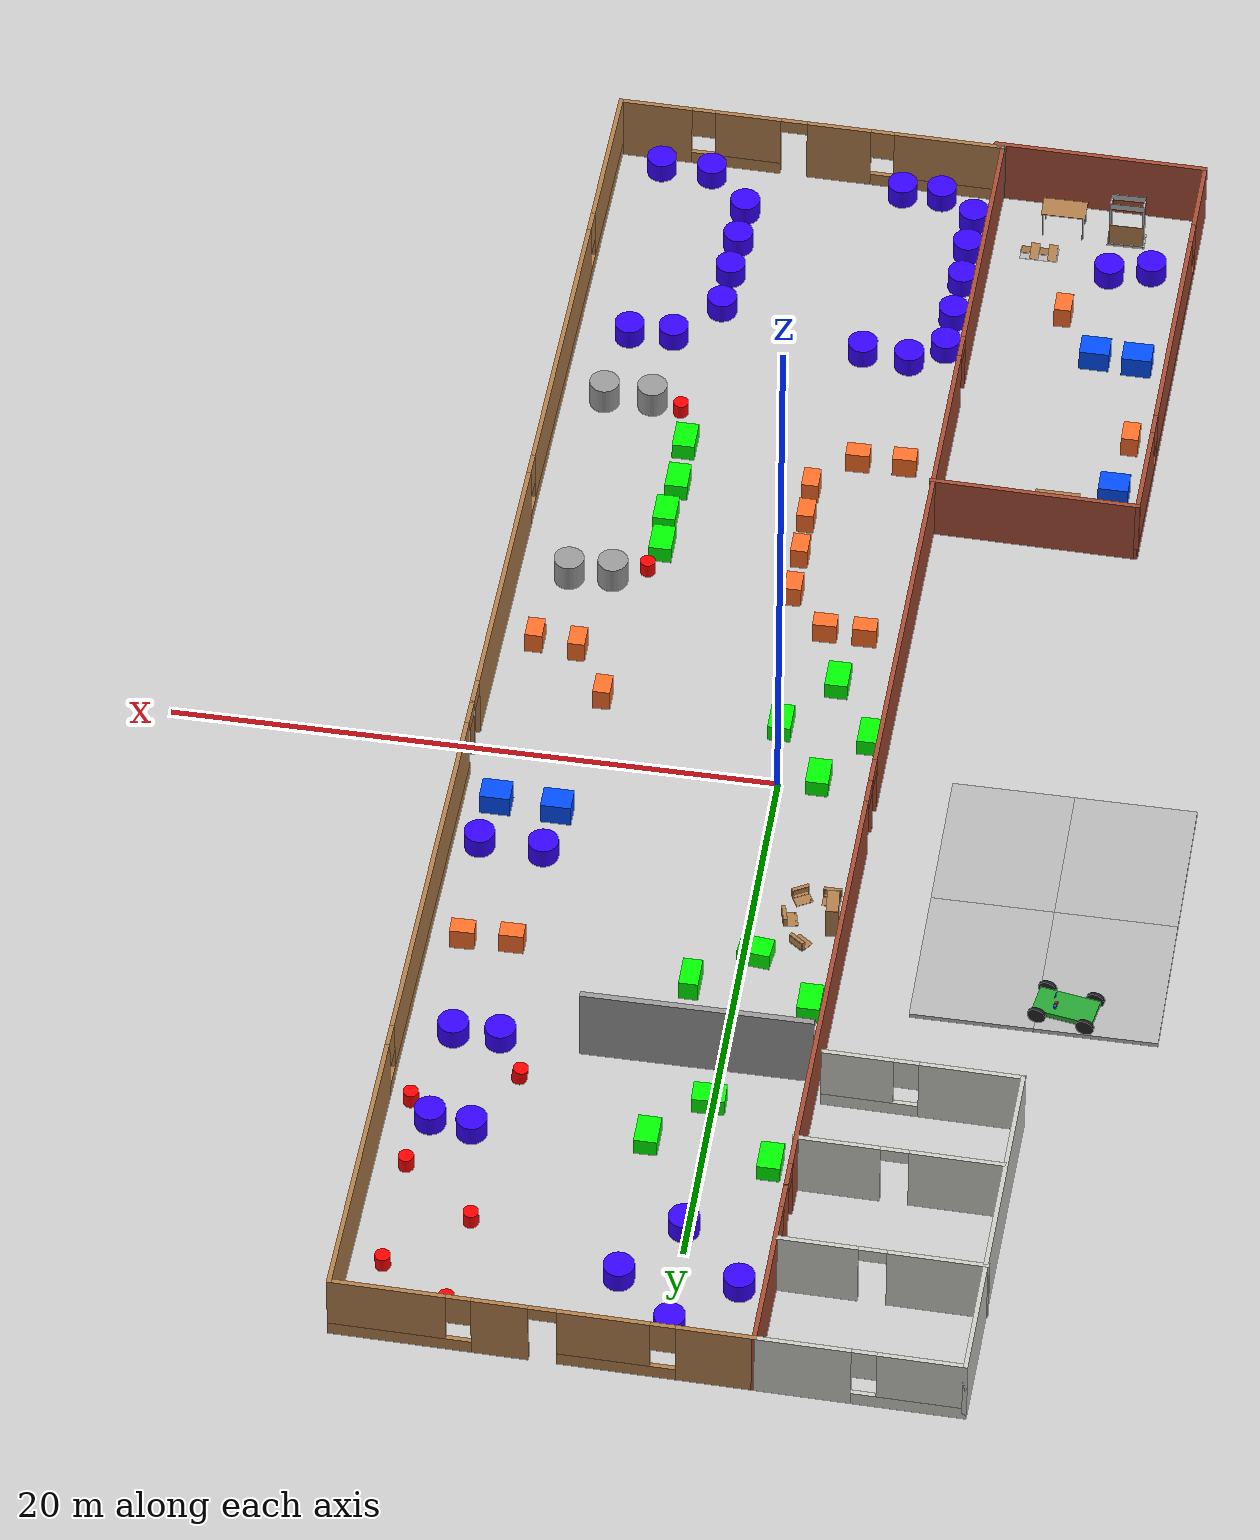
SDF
<sdf version="1.7">
 <world name="default">
  <light name="sun" type="directional">
   <pose>0 0 10 0 -0 0</pose>
   <diffuse>0.8 0.8 0.8 1</diffuse>
   <specular>0.2 0.2 0.2 1</specular>
   <attenuation>
    <range>1000</range>
    <constant>0.9</constant>
    <linear>0.01</linear>
    <quadratic>0.001</quadratic>
   </attenuation>
   <direction>-0.5 0.1 -0.9</direction>
   <spot><inner_angle>0</inner_angle><outer_angle>0</outer_angle><falloff>0</falloff></spot>
  </light>
  <model name="ground_plane">
   <static>1</static>
   <link name="link">
    <collision name="collision">
     <geometry><plane><normal>0 0 1</normal><size>100 100</size></plane></geometry>
     <surface>
      <contact><collide_bitmask>65535</collide_bitmask></contact>
      <friction><ode><mu>100</mu><mu2>50</mu2></ode></friction>
     </surface>
    </collision>
    <visual name="visual">
     <cast_shadows>0</cast_shadows>
     <geometry><plane><normal>0 0 1</normal><size>100 100</size></plane></geometry>
     <material>
      <script><uri>file://media/materials/scripts/gazebo.material</uri><name>Gazebo/Grey</name></script>
     </material>
    </visual>
   </link>
  </model>
  <gravity>0 0 -9.8</gravity>
  <magnetic_field>6e-06 2.3e-05 -4.2e-05</magnetic_field>
  <atmosphere type="adiabatic"/>
  <physics type="ode">
   <max_step_size>0.001</max_step_size>
   <real_time_factor>1</real_time_factor>
   <real_time_update_rate>1000</real_time_update_rate>
  </physics>
  <scene><ambient>0.4 0.4 0.4 1</ambient><background>0.7 0.7 0.7 1</background><shadows>1</shadows></scene>
  <spherical_coordinates>
   <surface_model>EARTH_WGS84</surface_model>
   <latitude_deg>0</latitude_deg>
   <longitude_deg>0</longitude_deg>
   <elevation>0</elevation>
   <heading_deg>0</heading_deg>
  </spherical_coordinates>
  <model name="restaurant">
   <pose>-0.016395 -1.4412 0 0 0 -1.58539</pose>
   <link name="Wall_10">
    <collision name="Wall_10_Collision">
     <geometry><box><size>12 0.15 2.5</size></box></geometry>
     <pose>0 0 1.25 0 -0 0</pose>
    </collision>
    <visual name="Wall_10_Visual">
     <pose>0 0 1.25 0 -0 0</pose>
     <geometry><box><size>12 0.15 2.5</size></box></geometry>
     <material>
      <script><uri>file://media/materials/scripts/gazebo.material</uri><name>Gazebo/CeilingTiled</name></script>
      <ambient>1 0.764706 0.305882 1</ambient>
     </material>
     <meta><layer>0</layer></meta>
    </visual>
    <pose>-20.4579 -9.95516 0 0 -0 0</pose>
   </link>
   <link name="Wall_11">
    <pose>-14.5329 -6.78016 0 0 -0 1.5708</pose>
    <visual name="Wall_11_Visual_0">
     <pose>-1.5565 0 1.25 0 -0 0</pose>
     <geometry><box><size>3.38699 0.15 2.5</size></box></geometry>
     <material>
      <script><uri>file://media/materials/scripts/gazebo.material</uri><name>Gazebo/CeilingTiled</name></script>
      <ambient>1 0.764706 0.305882 1</ambient>
     </material>
     <meta><layer>0</layer></meta>
    </visual>
    <collision name="Wall_11_Collision_0">
     <geometry><box><size>3.38699 0.15 2.5</size></box></geometry>
     <pose>-1.5565 0 1.25 0 -0 0</pose>
    </collision>
    <visual name="Wall_11_Visual_1">
     <pose>1.6935 0 0.25 0 -0 0</pose>
     <geometry><box><size>3.11301 0.15 0.5</size></box></geometry>
     <material>
      <script><uri>file://media/materials/scripts/gazebo.material</uri><name>Gazebo/CeilingTiled</name></script>
      <ambient>1 0.764706 0.305882 1</ambient>
     </material>
     <meta><layer>0</layer></meta>
    </visual>
    <collision name="Wall_11_Collision_1">
     <geometry><box><size>3.11301 0.15 0.5</size></box></geometry>
     <pose>1.6935 0 0.25 0 -0 0</pose>
    </collision>
    <visual name="Wall_11_Visual_2">
     <pose>2.0935 0 1.5 0 -0 0</pose>
     <geometry><box><size>2.31301 0.15 2</size></box></geometry>
     <material>
      <script><uri>file://media/materials/scripts/gazebo.material</uri><name>Gazebo/CeilingTiled</name></script>
      <ambient>1 0.764706 0.305882 1</ambient>
     </material>
     <meta><layer>0</layer></meta>
    </visual>
    <collision name="Wall_11_Collision_2">
     <geometry><box><size>2.31301 0.15 2</size></box></geometry>
     <pose>2.0935 0 1.5 0 -0 0</pose>
    </collision>
    <visual name="Wall_11_Visual_3">
     <pose>0.536991 0 1.9 0 -0 0</pose>
     <geometry><box><size>0.8 0.15 1.2</size></box></geometry>
     <material>
      <script><uri>file://media/materials/scripts/gazebo.material</uri><name>Gazebo/CeilingTiled</name></script>
      <ambient>1 0.764706 0.305882 1</ambient>
     </material>
     <meta><layer>0</layer></meta>
    </visual>
    <collision name="Wall_11_Collision_3">
     <geometry><box><size>0.8 0.15 1.2</size></box></geometry>
     <pose>0.536991 0 1.9 0 -0 0</pose>
    </collision>
   </link>
   <link name="Wall_13">
    <collision name="Wall_13_Collision">
     <geometry><box><size>0.414926 0.15 2.5</size></box></geometry>
     <pose>0 0 1.25 0 -0 0</pose>
    </collision>
    <visual name="Wall_13_Visual">
     <pose>0 0 1.25 0 -0 0</pose>
     <geometry><box><size>0.414926 0.15 2.5</size></box></geometry>
     <material>
      <script><uri>file://media/materials/scripts/gazebo.material</uri><name>Gazebo/Grey</name></script>
      <ambient>1 1 1 1</ambient>
     </material>
     <meta><layer>0</layer></meta>
    </visual>
    <pose>26.2861 -2.99211 0 0 -0 1.02256</pose>
   </link>
   <link name="Wall_14">
    <collision name="Wall_14_Collision">
     <geometry><box><size>7.25 0.15 2.5</size></box></geometry>
     <pose>0 0 1.25 0 -0 0</pose>
    </collision>
    <visual name="Wall_14_Visual">
     <pose>0 0 1.25 0 -0 0</pose>
     <geometry><box><size>7.25 0.15 2.5</size></box></geometry>
     <material>
      <script><uri>file://media/materials/scripts/gazebo.material</uri><name>Gazebo/Bricks</name></script>
      <ambient>0.996078 0.47451 0.0196078 1</ambient>
     </material>
     <meta><layer>0</layer></meta>
    </visual>
    <pose>26.3552 -6.42906 0 0 -0 -1.5708</pose>
   </link>
   <link name="Wall_15">
    <pose>18.4302 -9.97906 0 0 -0 3.14159</pose>
    <visual name="Wall_15_Visual_0">
     <pose>-6.61611 0 1.25 0 -0 0</pose>
     <geometry><box><size>2.76777 0.15 2.5</size></box></geometry>
     <material>
      <script><uri>file://media/materials/scripts/gazebo.material</uri><name>Gazebo/Bricks</name></script>
      <ambient>0.996078 0.47451 0.0196078 1</ambient>
     </material>
     <meta><layer>0</layer></meta>
    </visual>
    <collision name="Wall_15_Collision_0">
     <geometry><box><size>2.76777 0.15 2.5</size></box></geometry>
     <pose>-6.61611 0 1.25 0 -0 0</pose>
    </collision>
    <visual name="Wall_15_Visual_1">
     <pose>1.38389 0 0.25 0 -0 0</pose>
     <geometry><box><size>13.2322 0.15 0.5</size></box></geometry>
     <material>
      <script><uri>file://media/materials/scripts/gazebo.material</uri><name>Gazebo/Bricks</name></script>
      <ambient>0.996078 0.47451 0.0196078 1</ambient>
     </material>
     <meta><layer>0</layer></meta>
    </visual>
    <collision name="Wall_15_Collision_1">
     <geometry><box><size>13.2322 0.15 0.5</size></box></geometry>
     <pose>1.38389 0 0.25 0 -0 0</pose>
    </collision>
    <visual name="Wall_15_Visual_2">
     <pose>-0.347226 0 1.5 0 -0 0</pose>
     <geometry><box><size>8.17 0.15 2</size></box></geometry>
     <material>
      <script><uri>file://media/materials/scripts/gazebo.material</uri><name>Gazebo/Bricks</name></script>
      <ambient>0.996078 0.47451 0.0196078 1</ambient>
     </material>
     <meta><layer>0</layer></meta>
    </visual>
    <collision name="Wall_15_Collision_2">
     <geometry><box><size>8.17 0.15 2</size></box></geometry>
     <pose>-0.347226 0 1.5 0 -0 0</pose>
    </collision>
    <visual name="Wall_15_Visual_3">
     <pose>6.26889 0 1.5 0 -0 0</pose>
     <geometry><box><size>3.46223 0.15 2</size></box></geometry>
     <material>
      <script><uri>file://media/materials/scripts/gazebo.material</uri><name>Gazebo/Bricks</name></script>
      <ambient>0.996078 0.47451 0.0196078 1</ambient>
     </material>
     <meta><layer>0</layer></meta>
    </visual>
    <collision name="Wall_15_Collision_3">
     <geometry><box><size>3.46223 0.15 2</size></box></geometry>
     <pose>6.26889 0 1.5 0 -0 0</pose>
    </collision>
    <visual name="Wall_15_Visual_4">
     <pose>-4.83223 0 1.9 0 -0 0</pose>
     <geometry><box><size>0.8 0.15 1.2</size></box></geometry>
     <material>
      <script><uri>file://media/materials/scripts/gazebo.material</uri><name>Gazebo/Bricks</name></script>
      <ambient>0.996078 0.47451 0.0196078 1</ambient>
     </material>
     <meta><layer>0</layer></meta>
    </visual>
    <collision name="Wall_15_Collision_4">
     <geometry><box><size>0.8 0.15 1.2</size></box></geometry>
     <pose>-4.83223 0 1.9 0 -0 0</pose>
    </collision>
    <visual name="Wall_15_Visual_5">
     <pose>4.13777 0 1.9 0 -0 0</pose>
     <geometry><box><size>0.8 0.15 1.2</size></box></geometry>
     <material>
      <script><uri>file://media/materials/scripts/gazebo.material</uri><name>Gazebo/Bricks</name></script>
      <ambient>0.996078 0.47451 0.0196078 1</ambient>
     </material>
     <meta><layer>0</layer></meta>
    </visual>
    <collision name="Wall_15_Collision_5">
     <geometry><box><size>0.8 0.15 1.2</size></box></geometry>
     <pose>4.13777 0 1.9 0 -0 0</pose>
    </collision>
   </link>
   <link name="Wall_16">
    <collision name="Wall_16_Collision">
     <geometry><box><size>7 0.15 2.5</size></box></geometry>
     <pose>0 0 1.25 0 -0 0</pose>
    </collision>
    <visual name="Wall_16_Visual">
     <pose>0 0 1.25 0 -0 0</pose>
     <geometry><box><size>7 0.15 2.5</size></box></geometry>
     <material>
      <script><uri>file://media/materials/scripts/gazebo.material</uri><name>Gazebo/Bricks</name></script>
      <ambient>0.996078 0.47451 0.0196078 1</ambient>
     </material>
     <meta><layer>0</layer></meta>
    </visual>
    <pose>10.5052 -6.55406 0 0 -0 1.5708</pose>
   </link>
   <link name="Wall_18">
    <pose>-18.1702 -6.57581 0 0 -0 -1.5708</pose>
    <visual name="Wall_18_Visual_0">
     <pose>-1.9755 0 1.25 0 -0 0</pose>
     <geometry><box><size>2.799 0.15 2.5</size></box></geometry>
     <material>
      <script><uri>file://media/materials/scripts/gazebo.material</uri><name>Gazebo/CeilingTiled</name></script>
      <ambient>1 0.764706 0.305882 1</ambient>
     </material>
     <meta><layer>0</layer></meta>
    </visual>
    <collision name="Wall_18_Collision_0">
     <geometry><box><size>2.799 0.15 2.5</size></box></geometry>
     <pose>-1.9755 0 1.25 0 -0 0</pose>
    </collision>
    <visual name="Wall_18_Visual_1">
     <pose>1.8495 0 1.25 0 -0 0</pose>
     <geometry><box><size>3.051 0.15 2.5</size></box></geometry>
     <material>
      <script><uri>file://media/materials/scripts/gazebo.material</uri><name>Gazebo/CeilingTiled</name></script>
      <ambient>1 0.764706 0.305882 1</ambient>
     </material>
     <meta><layer>0</layer></meta>
    </visual>
    <collision name="Wall_18_Collision_1">
     <geometry><box><size>3.051 0.15 2.5</size></box></geometry>
     <pose>1.8495 0 1.25 0 -0 0</pose>
    </collision>
    <visual name="Wall_18_Visual_2">
     <pose>-0.126 0 2.25 0 -0 0</pose>
     <geometry><box><size>0.9 0.15 0.5</size></box></geometry>
     <material>
      <script><uri>file://media/materials/scripts/gazebo.material</uri><name>Gazebo/CeilingTiled</name></script>
      <ambient>1 0.764706 0.305882 1</ambient>
     </material>
     <meta><layer>0</layer></meta>
    </visual>
    <collision name="Wall_18_Collision_2">
     <geometry><box><size>0.9 0.15 0.5</size></box></geometry>
     <pose>-0.126 0 2.25 0 -0 0</pose>
    </collision>
   </link>
   <link name="Wall_22">
    <pose>-22.2964 -6.69484 0 0 -0 -1.5708</pose>
    <visual name="Wall_22_Visual_0">
     <pose>-2.05485 0 1.25 0 -0 0</pose>
     <geometry><box><size>2.6403 0.15 2.5</size></box></geometry>
     <material>
      <script><uri>file://media/materials/scripts/gazebo.material</uri><name>Gazebo/CeilingTiled</name></script>
      <ambient>1 0.764706 0.305882 1</ambient>
     </material>
     <meta><layer>0</layer></meta>
    </visual>
    <collision name="Wall_22_Collision_0">
     <geometry><box><size>2.6403 0.15 2.5</size></box></geometry>
     <pose>-2.05485 0 1.25 0 -0 0</pose>
    </collision>
    <visual name="Wall_22_Visual_1">
     <pose>1.77015 0 1.25 0 -0 0</pose>
     <geometry><box><size>3.2097 0.15 2.5</size></box></geometry>
     <material>
      <script><uri>file://media/materials/scripts/gazebo.material</uri><name>Gazebo/CeilingTiled</name></script>
      <ambient>1 0.764706 0.305882 1</ambient>
     </material>
     <meta><layer>0</layer></meta>
    </visual>
    <collision name="Wall_22_Collision_1">
     <geometry><box><size>3.2097 0.15 2.5</size></box></geometry>
     <pose>1.77015 0 1.25 0 -0 0</pose>
    </collision>
    <visual name="Wall_22_Visual_2">
     <pose>-0.2847 0 2.25 0 -0 0</pose>
     <geometry><box><size>0.9 0.15 0.5</size></box></geometry>
     <material>
      <script><uri>file://media/materials/scripts/gazebo.material</uri><name>Gazebo/CeilingTiled</name></script>
      <ambient>1 0.764706 0.305882 1</ambient>
     </material>
     <meta><layer>0</layer></meta>
    </visual>
    <collision name="Wall_22_Collision_2">
     <geometry><box><size>0.9 0.15 0.5</size></box></geometry>
     <pose>-0.2847 0 2.25 0 -0 0</pose>
    </collision>
   </link>
   <link name="Wall_5">
    <pose>-26.3829 3.31984 0 0 -0 1.5708</pose>
    <visual name="Wall_5_Visual_0">
     <pose>-5.4842 0 1.25 0 -0 0</pose>
     <geometry><box><size>2.5316 0.15 2.5</size></box></geometry>
     <material>
      <script><uri>file://media/materials/scripts/gazebo.material</uri><name>Gazebo/Wood</name></script>
      <ambient>0.760784 0.662745 0.627451 1</ambient>
     </material>
     <meta><layer>0</layer></meta>
    </visual>
    <collision name="Wall_5_Collision_0">
     <geometry><box><size>2.5316 0.15 2.5</size></box></geometry>
     <pose>-5.4842 0 1.25 0 -0 0</pose>
    </collision>
    <visual name="Wall_5_Visual_1">
     <pose>1.30897 0 1.25 0 -0 0</pose>
     <geometry><box><size>1.79996 0.15 2.5</size></box></geometry>
     <material>
      <script><uri>file://media/materials/scripts/gazebo.material</uri><name>Gazebo/Wood</name></script>
      <ambient>0.760784 0.662745 0.627451 1</ambient>
     </material>
     <meta><layer>0</layer></meta>
    </visual>
    <collision name="Wall_5_Collision_1">
     <geometry><box><size>1.79996 0.15 2.5</size></box></geometry>
     <pose>1.30897 0 1.25 0 -0 0</pose>
    </collision>
    <visual name="Wall_5_Visual_2">
     <pose>-2.3547 0 0.25 0 -0 0</pose>
     <geometry><box><size>3.72739 0.15 0.5</size></box></geometry>
     <material>
      <script><uri>file://media/materials/scripts/gazebo.material</uri><name>Gazebo/Wood</name></script>
      <ambient>0.760784 0.662745 0.627451 1</ambient>
     </material>
     <meta><layer>0</layer></meta>
    </visual>
    <collision name="Wall_5_Collision_2">
     <geometry><box><size>3.72739 0.15 0.5</size></box></geometry>
     <pose>-2.3547 0 0.25 0 -0 0</pose>
    </collision>
    <visual name="Wall_5_Visual_3">
     <pose>4.47947 0 0.25 0 -0 0</pose>
     <geometry><box><size>4.54105 0.15 0.5</size></box></geometry>
     <material>
      <script><uri>file://media/materials/scripts/gazebo.material</uri><name>Gazebo/Wood</name></script>
      <ambient>0.760784 0.662745 0.627451 1</ambient>
     </material>
     <meta><layer>0</layer></meta>
    </visual>
    <collision name="Wall_5_Collision_3">
     <geometry><box><size>4.54105 0.15 0.5</size></box></geometry>
     <pose>4.47947 0 0.25 0 -0 0</pose>
    </collision>
    <visual name="Wall_5_Visual_4">
     <pose>-1.9547 0 1.5 0 -0 0</pose>
     <geometry><box><size>2.92739 0.15 2</size></box></geometry>
     <material>
      <script><uri>file://media/materials/scripts/gazebo.material</uri><name>Gazebo/Wood</name></script>
      <ambient>0.760784 0.662745 0.627451 1</ambient>
     </material>
     <meta><layer>0</layer></meta>
    </visual>
    <collision name="Wall_5_Collision_4">
     <geometry><box><size>2.92739 0.15 2</size></box></geometry>
     <pose>-1.9547 0 1.5 0 -0 0</pose>
    </collision>
    <visual name="Wall_5_Visual_5">
     <pose>-1.9547 0 1.5 0 -0 0</pose>
     <geometry><box><size>2.92739 0.15 2</size></box></geometry>
     <material>
      <script><uri>file://media/materials/scripts/gazebo.material</uri><name>Gazebo/Wood</name></script>
      <ambient>0.760784 0.662745 0.627451 1</ambient>
     </material>
     <meta><layer>0</layer></meta>
    </visual>
    <collision name="Wall_5_Collision_5">
     <geometry><box><size>2.92739 0.15 2</size></box></geometry>
     <pose>-1.9547 0 1.5 0 -0 0</pose>
    </collision>
    <visual name="Wall_5_Visual_6">
     <pose>4.87948 0 1.5 0 -0 0</pose>
     <geometry><box><size>3.74105 0.15 2</size></box></geometry>
     <material>
      <script><uri>file://media/materials/scripts/gazebo.material</uri><name>Gazebo/Wood</name></script>
      <ambient>0.760784 0.662745 0.627451 1</ambient>
     </material>
     <meta><layer>0</layer></meta>
    </visual>
    <collision name="Wall_5_Collision_6">
     <geometry><box><size>3.74105 0.15 2</size></box></geometry>
     <pose>4.87948 0 1.5 0 -0 0</pose>
    </collision>
    <visual name="Wall_5_Visual_7">
     <pose>-3.8184 0 1.9 0 -0 0</pose>
     <geometry><box><size>0.8 0.15 1.2</size></box></geometry>
     <material>
      <script><uri>file://media/materials/scripts/gazebo.material</uri><name>Gazebo/Wood</name></script>
      <ambient>0.760784 0.662745 0.627451 1</ambient>
     </material>
     <meta><layer>0</layer></meta>
    </visual>
    <collision name="Wall_5_Collision_7">
     <geometry><box><size>0.8 0.15 1.2</size></box></geometry>
     <pose>-3.8184 0 1.9 0 -0 0</pose>
    </collision>
    <visual name="Wall_5_Visual_8">
     <pose>2.60895 0 1.9 0 -0 0</pose>
     <geometry><box><size>0.8 0.15 1.2</size></box></geometry>
     <material>
      <script><uri>file://media/materials/scripts/gazebo.material</uri><name>Gazebo/Wood</name></script>
      <ambient>0.760784 0.662745 0.627451 1</ambient>
     </material>
     <meta><layer>0</layer></meta>
    </visual>
    <collision name="Wall_5_Collision_8">
     <geometry><box><size>0.8 0.15 1.2</size></box></geometry>
     <pose>2.60895 0 1.9 0 -0 0</pose>
    </collision>
    <visual name="Wall_5_Visual_9">
     <pose>-0.041009 0 2.25 0 -0 0</pose>
     <geometry><box><size>0.9 0.15 0.5</size></box></geometry>
     <material>
      <script><uri>file://media/materials/scripts/gazebo.material</uri><name>Gazebo/Wood</name></script>
      <ambient>0.760784 0.662745 0.627451 1</ambient>
     </material>
     <meta><layer>0</layer></meta>
    </visual>
    <collision name="Wall_5_Collision_9">
     <geometry><box><size>0.9 0.15 0.5</size></box></geometry>
     <pose>-0.041009 0 2.25 0 -0 0</pose>
    </collision>
    <visual name="Wall_5_Visual_10">
     <pose>-0.041009 0 2.25 0 -0 0</pose>
     <geometry><box><size>0.9 0.15 0.5</size></box></geometry>
     <material>
      <script><uri>file://media/materials/scripts/gazebo.material</uri><name>Gazebo/Wood</name></script>
      <ambient>0.760784 0.662745 0.627451 1</ambient>
     </material>
     <meta><layer>0</layer></meta>
    </visual>
    <collision name="Wall_5_Collision_10">
     <geometry><box><size>0.9 0.15 0.5</size></box></geometry>
     <pose>-0.041009 0 2.25 0 -0 0</pose>
    </collision>
   </link>
   <link name="Wall_6">
    <pose>-0.082907 9.99484 0 0 -0 0</pose>
    <visual name="Wall_6_Visual_0">
     <pose>-21.4488 0 1.25 0 -0 0</pose>
     <geometry><box><size>9.8523 0.15 2.5</size></box></geometry>
     <material>
      <script><uri>file://media/materials/scripts/gazebo.material</uri><name>Gazebo/Wood</name></script>
      <ambient>0.760784 0.662745 0.627451 1</ambient>
     </material>
     <meta><layer>0</layer></meta>
    </visual>
    <collision name="Wall_6_Collision_0">
     <geometry><box><size>9.8523 0.15 2.5</size></box></geometry>
     <pose>-21.4488 0 1.25 0 -0 0</pose>
    </collision>
    <visual name="Wall_6_Visual_1">
     <pose>-1.7017 0 1.25 0 -0 0</pose>
     <geometry><box><size>0.066 0.15 2.5</size></box></geometry>
     <material>
      <script><uri>file://media/materials/scripts/gazebo.material</uri><name>Gazebo/Wood</name></script>
      <ambient>0.760784 0.662745 0.627451 1</ambient>
     </material>
     <meta><layer>0</layer></meta>
    </visual>
    <collision name="Wall_6_Collision_1">
     <geometry><box><size>0.066 0.15 2.5</size></box></geometry>
     <pose>-1.7017 0 1.25 0 -0 0</pose>
    </collision>
    <visual name="Wall_6_Visual_2">
     <pose>3.9468 0 1.25 0 -0 0</pose>
     <geometry><box><size>9.431 0.15 2.5</size></box></geometry>
     <material>
      <script><uri>file://media/materials/scripts/gazebo.material</uri><name>Gazebo/Wood</name></script>
      <ambient>0.760784 0.662745 0.627451 1</ambient>
     </material>
     <meta><layer>0</layer></meta>
    </visual>
    <collision name="Wall_6_Collision_2">
     <geometry><box><size>9.431 0.15 2.5</size></box></geometry>
     <pose>3.9468 0 1.25 0 -0 0</pose>
    </collision>
    <visual name="Wall_6_Visual_3">
     <pose>-9.5787 0 0.25 0 -0 0</pose>
     <geometry><box><size>13.888 0.15 0.5</size></box></geometry>
     <material>
      <script><uri>file://media/materials/scripts/gazebo.material</uri><name>Gazebo/Wood</name></script>
      <ambient>0.760784 0.662745 0.627451 1</ambient>
     </material>
     <meta><layer>0</layer></meta>
    </visual>
    <collision name="Wall_6_Collision_3">
     <geometry><box><size>13.888 0.15 0.5</size></box></geometry>
     <pose>-9.5787 0 0.25 0 -0 0</pose>
    </collision>
    <visual name="Wall_6_Visual_4">
     <pose>17.5187 0 0.25 0 -0 0</pose>
     <geometry><box><size>17.7127 0.15 0.5</size></box></geometry>
     <material>
      <script><uri>file://media/materials/scripts/gazebo.material</uri><name>Gazebo/Wood</name></script>
      <ambient>0.760784 0.662745 0.627451 1</ambient>
     </material>
     <meta><layer>0</layer></meta>
    </visual>
    <collision name="Wall_6_Collision_4">
     <geometry><box><size>17.7127 0.15 0.5</size></box></geometry>
     <pose>17.5187 0 0.25 0 -0 0</pose>
    </collision>
    <visual name="Wall_6_Visual_5">
     <pose>-9.1787 0 1.5 0 -0 0</pose>
     <geometry><box><size>13.088 0.15 2</size></box></geometry>
     <material>
      <script><uri>file://media/materials/scripts/gazebo.material</uri><name>Gazebo/Wood</name></script>
      <ambient>0.760784 0.662745 0.627451 1</ambient>
     </material>
     <meta><layer>0</layer></meta>
    </visual>
    <collision name="Wall_6_Collision_5">
     <geometry><box><size>13.088 0.15 2</size></box></geometry>
     <pose>-9.1787 0 1.5 0 -0 0</pose>
    </collision>
    <visual name="Wall_6_Visual_6">
     <pose>-9.1787 0 1.5 0 -0 0</pose>
     <geometry><box><size>13.088 0.15 2</size></box></geometry>
     <material>
      <script><uri>file://media/materials/scripts/gazebo.material</uri><name>Gazebo/Wood</name></script>
      <ambient>0.760784 0.662745 0.627451 1</ambient>
     </material>
     <meta><layer>0</layer></meta>
    </visual>
    <collision name="Wall_6_Collision_6">
     <geometry><box><size>13.088 0.15 2</size></box></geometry>
     <pose>-9.1787 0 1.5 0 -0 0</pose>
    </collision>
    <visual name="Wall_6_Visual_7">
     <pose>14.7548 0 1.5 0 -0 0</pose>
     <geometry><box><size>10.585 0.15 2</size></box></geometry>
     <material>
      <script><uri>file://media/materials/scripts/gazebo.material</uri><name>Gazebo/Wood</name></script>
      <ambient>0.760784 0.662745 0.627451 1</ambient>
     </material>
     <meta><layer>0</layer></meta>
    </visual>
    <collision name="Wall_6_Collision_7">
     <geometry><box><size>10.585 0.15 2</size></box></geometry>
     <pose>14.7548 0 1.5 0 -0 0</pose>
    </collision>
    <visual name="Wall_6_Visual_8">
     <pose>23.6111 0 1.5 0 -0 0</pose>
     <geometry><box><size>5.5277 0.15 2</size></box></geometry>
     <material>
      <script><uri>file://media/materials/scripts/gazebo.material</uri><name>Gazebo/Wood</name></script>
      <ambient>0.760784 0.662745 0.627451 1</ambient>
     </material>
     <meta><layer>0</layer></meta>
    </visual>
    <collision name="Wall_6_Collision_8">
     <geometry><box><size>5.5277 0.15 2</size></box></geometry>
     <pose>23.6111 0 1.5 0 -0 0</pose>
    </collision>
    <visual name="Wall_6_Visual_9">
     <pose>-16.1227 0 1.9 0 -0 0</pose>
     <geometry><box><size>0.8 0.15 1.2</size></box></geometry>
     <material>
      <script><uri>file://media/materials/scripts/gazebo.material</uri><name>Gazebo/Wood</name></script>
      <ambient>0.760784 0.662745 0.627451 1</ambient>
     </material>
     <meta><layer>0</layer></meta>
    </visual>
    <collision name="Wall_6_Collision_9">
     <geometry><box><size>0.8 0.15 1.2</size></box></geometry>
     <pose>-16.1227 0 1.9 0 -0 0</pose>
    </collision>
    <visual name="Wall_6_Visual_10">
     <pose>9.0623 0 1.9 0 -0 0</pose>
     <geometry><box><size>0.8 0.15 1.2</size></box></geometry>
     <material>
      <script><uri>file://media/materials/scripts/gazebo.material</uri><name>Gazebo/Wood</name></script>
      <ambient>0.760784 0.662745 0.627451 1</ambient>
     </material>
     <meta><layer>0</layer></meta>
    </visual>
    <collision name="Wall_6_Collision_10">
     <geometry><box><size>0.8 0.15 1.2</size></box></geometry>
     <pose>9.0623 0 1.9 0 -0 0</pose>
    </collision>
    <visual name="Wall_6_Visual_11">
     <pose>20.4473 0 1.9 0 -0 0</pose>
     <geometry><box><size>0.8 0.15 1.2</size></box></geometry>
     <material>
      <script><uri>file://media/materials/scripts/gazebo.material</uri><name>Gazebo/Wood</name></script>
      <ambient>0.760784 0.662745 0.627451 1</ambient>
     </material>
     <meta><layer>0</layer></meta>
    </visual>
    <collision name="Wall_6_Collision_11">
     <geometry><box><size>0.8 0.15 1.2</size></box></geometry>
     <pose>20.4473 0 1.9 0 -0 0</pose>
    </collision>
    <visual name="Wall_6_Visual_12">
     <pose>-1.2187 0 2.25 0 -0 0</pose>
     <geometry><box><size>0.9 0.15 0.5</size></box></geometry>
     <material>
      <script><uri>file://media/materials/scripts/gazebo.material</uri><name>Gazebo/Wood</name></script>
      <ambient>0.760784 0.662745 0.627451 1</ambient>
     </material>
     <meta><layer>0</layer></meta>
    </visual>
    <collision name="Wall_6_Collision_12">
     <geometry><box><size>0.9 0.15 0.5</size></box></geometry>
     <pose>-1.2187 0 2.25 0 -0 0</pose>
    </collision>
    <visual name="Wall_6_Visual_13">
     <pose>-2.1847 0 2.25 0 -0 0</pose>
     <geometry><box><size>0.9 0.15 0.5</size></box></geometry>
     <material>
      <script><uri>file://media/materials/scripts/gazebo.material</uri><name>Gazebo/Wood</name></script>
      <ambient>0.760784 0.662745 0.627451 1</ambient>
     </material>
     <meta><layer>0</layer></meta>
    </visual>
    <collision name="Wall_6_Collision_13">
     <geometry><box><size>0.9 0.15 0.5</size></box></geometry>
     <pose>-2.1847 0 2.25 0 -0 0</pose>
    </collision>
    <visual name="Wall_6_Visual_14">
     <pose>-2.1847 0 2.25 0 -0 0</pose>
     <geometry><box><size>0.9 0.15 0.5</size></box></geometry>
     <material>
      <script><uri>file://media/materials/scripts/gazebo.material</uri><name>Gazebo/Wood</name></script>
      <ambient>0.760784 0.662745 0.627451 1</ambient>
     </material>
     <meta><layer>0</layer></meta>
    </visual>
    <collision name="Wall_6_Collision_14">
     <geometry><box><size>0.9 0.15 0.5</size></box></geometry>
     <pose>-2.1847 0 2.25 0 -0 0</pose>
    </collision>
   </link>
   <link name="Wall_7">
    <pose>26.2171 3.44484 0 0 -0 -1.5708</pose>
    <visual name="Wall_7_Visual_0">
     <pose>-5.3615 0 1.25 0 -0 0</pose>
     <geometry><box><size>2.52701 0.15 2.5</size></box></geometry>
     <material>
      <script><uri>file://media/materials/scripts/gazebo.material</uri><name>Gazebo/Wood</name></script>
      <ambient>0.760784 0.662745 0.627451 1</ambient>
     </material>
     <meta><layer>0</layer></meta>
    </visual>
    <collision name="Wall_7_Collision_0">
     <geometry><box><size>2.52701 0.15 2.5</size></box></geometry>
     <pose>-5.3615 0 1.25 0 -0 0</pose>
    </collision>
    <visual name="Wall_7_Visual_1">
     <pose>0.950009 0 1.25 0 -0 0</pose>
     <geometry><box><size>2.186 0.15 2.5</size></box></geometry>
     <material>
      <script><uri>file://media/materials/scripts/gazebo.material</uri><name>Gazebo/Wood</name></script>
      <ambient>0.760784 0.662745 0.627451 1</ambient>
     </material>
     <meta><layer>0</layer></meta>
    </visual>
    <collision name="Wall_7_Collision_1">
     <geometry><box><size>2.186 0.15 2.5</size></box></geometry>
     <pose>0.950009 0 1.25 0 -0 0</pose>
    </collision>
    <visual name="Wall_7_Visual_2">
     <pose>-2.57049 0 0.25 0 -0 0</pose>
     <geometry><box><size>3.055 0.15 0.5</size></box></geometry>
     <material>
      <script><uri>file://media/materials/scripts/gazebo.material</uri><name>Gazebo/Wood</name></script>
      <ambient>0.760784 0.662745 0.627451 1</ambient>
     </material>
     <meta><layer>0</layer></meta>
    </visual>
    <collision name="Wall_7_Collision_2">
     <geometry><box><size>3.055 0.15 0.5</size></box></geometry>
     <pose>-2.57049 0 0.25 0 -0 0</pose>
    </collision>
    <visual name="Wall_7_Visual_3">
     <pose>4.334 0 0.25 0 -0 0</pose>
     <geometry><box><size>4.58199 0.15 0.5</size></box></geometry>
     <material>
      <script><uri>file://media/materials/scripts/gazebo.material</uri><name>Gazebo/Wood</name></script>
      <ambient>0.760784 0.662745 0.627451 1</ambient>
     </material>
     <meta><layer>0</layer></meta>
    </visual>
    <collision name="Wall_7_Collision_3">
     <geometry><box><size>4.58199 0.15 0.5</size></box></geometry>
     <pose>4.334 0 0.25 0 -0 0</pose>
    </collision>
    <visual name="Wall_7_Visual_4">
     <pose>-2.17049 0 1.5 0 -0 0</pose>
     <geometry><box><size>2.255 0.15 2</size></box></geometry>
     <material>
      <script><uri>file://media/materials/scripts/gazebo.material</uri><name>Gazebo/Wood</name></script>
      <ambient>0.760784 0.662745 0.627451 1</ambient>
     </material>
     <meta><layer>0</layer></meta>
    </visual>
    <collision name="Wall_7_Collision_4">
     <geometry><box><size>2.255 0.15 2</size></box></geometry>
     <pose>-2.17049 0 1.5 0 -0 0</pose>
    </collision>
    <visual name="Wall_7_Visual_5">
     <pose>-2.17049 0 1.5 0 -0 0</pose>
     <geometry><box><size>2.255 0.15 2</size></box></geometry>
     <material>
      <script><uri>file://media/materials/scripts/gazebo.material</uri><name>Gazebo/Wood</name></script>
      <ambient>0.760784 0.662745 0.627451 1</ambient>
     </material>
     <meta><layer>0</layer></meta>
    </visual>
    <collision name="Wall_7_Collision_5">
     <geometry><box><size>2.255 0.15 2</size></box></geometry>
     <pose>-2.17049 0 1.5 0 -0 0</pose>
    </collision>
    <visual name="Wall_7_Visual_6">
     <pose>4.734 0 1.5 0 -0 0</pose>
     <geometry><box><size>3.78199 0.15 2</size></box></geometry>
     <material>
      <script><uri>file://media/materials/scripts/gazebo.material</uri><name>Gazebo/Wood</name></script>
      <ambient>0.760784 0.662745 0.627451 1</ambient>
     </material>
     <meta><layer>0</layer></meta>
    </visual>
    <collision name="Wall_7_Collision_6">
     <geometry><box><size>3.78199 0.15 2</size></box></geometry>
     <pose>4.734 0 1.5 0 -0 0</pose>
    </collision>
    <visual name="Wall_7_Visual_7">
     <pose>-3.69799 0 1.9 0 -0 0</pose>
     <geometry><box><size>0.8 0.15 1.2</size></box></geometry>
     <material>
      <script><uri>file://media/materials/scripts/gazebo.material</uri><name>Gazebo/Wood</name></script>
      <ambient>0.760784 0.662745 0.627451 1</ambient>
     </material>
     <meta><layer>0</layer></meta>
    </visual>
    <collision name="Wall_7_Collision_7">
     <geometry><box><size>0.8 0.15 1.2</size></box></geometry>
     <pose>-3.69799 0 1.9 0 -0 0</pose>
    </collision>
    <visual name="Wall_7_Visual_8">
     <pose>2.44301 0 1.9 0 -0 0</pose>
     <geometry><box><size>0.8 0.15 1.2</size></box></geometry>
     <material>
      <script><uri>file://media/materials/scripts/gazebo.material</uri><name>Gazebo/Wood</name></script>
      <ambient>0.760784 0.662745 0.627451 1</ambient>
     </material>
     <meta><layer>0</layer></meta>
    </visual>
    <collision name="Wall_7_Collision_8">
     <geometry><box><size>0.8 0.15 1.2</size></box></geometry>
     <pose>2.44301 0 1.9 0 -0 0</pose>
    </collision>
    <visual name="Wall_7_Visual_9">
     <pose>-0.592991 0 2.25 0 -0 0</pose>
     <geometry><box><size>0.9 0.15 0.5</size></box></geometry>
     <material>
      <script><uri>file://media/materials/scripts/gazebo.material</uri><name>Gazebo/Wood</name></script>
      <ambient>0.760784 0.662745 0.627451 1</ambient>
     </material>
     <meta><layer>0</layer></meta>
    </visual>
    <collision name="Wall_7_Collision_9">
     <geometry><box><size>0.9 0.15 0.5</size></box></geometry>
     <pose>-0.592991 0 2.25 0 -0 0</pose>
    </collision>
    <visual name="Wall_7_Visual_10">
     <pose>-0.592991 0 2.25 0 -0 0</pose>
     <geometry><box><size>0.9 0.15 0.5</size></box></geometry>
     <material>
      <script><uri>file://media/materials/scripts/gazebo.material</uri><name>Gazebo/Wood</name></script>
      <ambient>0.760784 0.662745 0.627451 1</ambient>
     </material>
     <meta><layer>0</layer></meta>
    </visual>
    <collision name="Wall_7_Collision_10">
     <geometry><box><size>0.9 0.15 0.5</size></box></geometry>
     <pose>-0.592991 0 2.25 0 -0 0</pose>
    </collision>
   </link>
   <link name="Wall_8">
    <pose>-0.082907 -3.23016 0 0 -0 -3.13684</pose>
    <visual name="Wall_8_Visual_0">
     <pose>-21.8254 0 1.25 0 -0 0</pose>
     <geometry><box><size>9.09973 0.15 2.5</size></box></geometry>
     <material>
      <script><uri>file://media/materials/scripts/gazebo.material</uri><name>Gazebo/Bricks</name></script>
      <ambient>0.996078 0.47451 0.0196078 1</ambient>
     </material>
     <meta><layer>0</layer></meta>
    </visual>
    <collision name="Wall_8_Collision_0">
     <geometry><box><size>9.09973 0.15 2.5</size></box></geometry>
     <pose>-21.8254 0 1.25 0 -0 0</pose>
    </collision>
    <visual name="Wall_8_Visual_1">
     <pose>-7.20486 0 1.25 0 -0 0</pose>
     <geometry><box><size>18.3414 0.15 2.5</size></box></geometry>
     <material>
      <script><uri>file://media/materials/scripts/gazebo.material</uri><name>Gazebo/Bricks</name></script>
      <ambient>0.996078 0.47451 0.0196078 1</ambient>
     </material>
     <meta><layer>0</layer></meta>
    </visual>
    <collision name="Wall_8_Collision_1">
     <geometry><box><size>18.3414 0.15 2.5</size></box></geometry>
     <pose>-7.20486 0 1.25 0 -0 0</pose>
    </collision>
    <visual name="Wall_8_Visual_2">
     <pose>2.87172 0 1.25 0 -0 0</pose>
     <geometry><box><size>0.01176 0.15 2.5</size></box></geometry>
     <material>
      <script><uri>file://media/materials/scripts/gazebo.material</uri><name>Gazebo/Bricks</name></script>
      <ambient>0.996078 0.47451 0.0196078 1</ambient>
     </material>
     <meta><layer>0</layer></meta>
    </visual>
    <collision name="Wall_8_Collision_2">
     <geometry><box><size>0.01176 0.15 2.5</size></box></geometry>
     <pose>2.87172 0 1.25 0 -0 0</pose>
    </collision>
    <visual name="Wall_8_Visual_3">
     <pose>11.4809 0 1.25 0 -0 0</pose>
     <geometry><box><size>15.4066 0.15 2.5</size></box></geometry>
     <material>
      <script><uri>file://media/materials/scripts/gazebo.material</uri><name>Gazebo/Bricks</name></script>
      <ambient>0.996078 0.47451 0.0196078 1</ambient>
     </material>
     <meta><layer>0</layer></meta>
    </visual>
    <collision name="Wall_8_Collision_3">
     <geometry><box><size>15.4066 0.15 2.5</size></box></geometry>
     <pose>11.4809 0 1.25 0 -0 0</pose>
    </collision>
    <visual name="Wall_8_Visual_4">
     <pose>23.2298 0 1.25 0 -0 0</pose>
     <geometry><box><size>6.29108 0.15 2.5</size></box></geometry>
     <material>
      <script><uri>file://media/materials/scripts/gazebo.material</uri><name>Gazebo/Bricks</name></script>
      <ambient>0.996078 0.47451 0.0196078 1</ambient>
     </material>
     <meta><layer>0</layer></meta>
    </visual>
    <collision name="Wall_8_Collision_4">
     <geometry><box><size>6.29108 0.15 2.5</size></box></geometry>
     <pose>23.2298 0 1.25 0 -0 0</pose>
    </collision>
    <visual name="Wall_8_Visual_5">
     <pose>23.6666 0 1.25 0 -0 0</pose>
     <geometry><box><size>5.4173 0.15 2.5</size></box></geometry>
     <material>
      <script><uri>file://media/materials/scripts/gazebo.material</uri><name>Gazebo/Bricks</name></script>
      <ambient>0.996078 0.47451 0.0196078 1</ambient>
     </material>
     <meta><layer>0</layer></meta>
    </visual>
    <collision name="Wall_8_Collision_5">
     <geometry><box><size>5.4173 0.15 2.5</size></box></geometry>
     <pose>23.6666 0 1.25 0 -0 0</pose>
    </collision>
    <visual name="Wall_8_Visual_6">
     <pose>-16.8256 0 2.25 0 -0 0</pose>
     <geometry><box><size>0.9 0.15 0.5</size></box></geometry>
     <material>
      <script><uri>file://media/materials/scripts/gazebo.material</uri><name>Gazebo/Bricks</name></script>
      <ambient>0.996078 0.47451 0.0196078 1</ambient>
     </material>
     <meta><layer>0</layer></meta>
    </visual>
    <collision name="Wall_8_Collision_6">
     <geometry><box><size>0.9 0.15 0.5</size></box></geometry>
     <pose>-16.8256 0 2.25 0 -0 0</pose>
    </collision>
    <visual name="Wall_8_Visual_7">
     <pose>2.41584 0 2.25 0 -0 0</pose>
     <geometry><box><size>0.9 0.15 0.5</size></box></geometry>
     <material>
      <script><uri>file://media/materials/scripts/gazebo.material</uri><name>Gazebo/Bricks</name></script>
      <ambient>0.996078 0.47451 0.0196078 1</ambient>
     </material>
     <meta><layer>0</layer></meta>
    </visual>
    <collision name="Wall_8_Collision_7">
     <geometry><box><size>0.9 0.15 0.5</size></box></geometry>
     <pose>2.41584 0 2.25 0 -0 0</pose>
    </collision>
    <visual name="Wall_8_Visual_8">
     <pose>3.3276 0 2.25 0 -0 0</pose>
     <geometry><box><size>0.9 0.15 0.5</size></box></geometry>
     <material>
      <script><uri>file://media/materials/scripts/gazebo.material</uri><name>Gazebo/Bricks</name></script>
      <ambient>0.996078 0.47451 0.0196078 1</ambient>
     </material>
     <meta><layer>0</layer></meta>
    </visual>
    <collision name="Wall_8_Collision_8">
     <geometry><box><size>0.9 0.15 0.5</size></box></geometry>
     <pose>3.3276 0 2.25 0 -0 0</pose>
    </collision>
    <visual name="Wall_8_Visual_9">
     <pose>19.6211 0 2.25 0 -0 0</pose>
     <geometry><box><size>0.873783 0.15 0.5</size></box></geometry>
     <material>
      <script><uri>file://media/materials/scripts/gazebo.material</uri><name>Gazebo/Bricks</name></script>
      <ambient>0.996078 0.47451 0.0196078 1</ambient>
     </material>
     <meta><layer>0</layer></meta>
    </visual>
    <collision name="Wall_8_Collision_9">
     <geometry><box><size>0.873783 0.15 0.5</size></box></geometry>
     <pose>19.6211 0 2.25 0 -0 0</pose>
    </collision>
   </link>
   <link name="Wall_9">
    <pose>-26.3829 -6.65516 0 0 -0 -1.5708</pose>
    <visual name="Wall_9_Visual_0">
     <pose>-1.8175 0 1.25 0 -0 0</pose>
     <geometry><box><size>3.11501 0.15 2.5</size></box></geometry>
     <material>
      <script><uri>file://media/materials/scripts/gazebo.material</uri><name>Gazebo/CeilingTiled</name></script>
      <ambient>1 0.764706 0.305882 1</ambient>
     </material>
     <meta><layer>0</layer></meta>
    </visual>
    <collision name="Wall_9_Collision_0">
     <geometry><box><size>3.11501 0.15 2.5</size></box></geometry>
     <pose>-1.8175 0 1.25 0 -0 0</pose>
    </collision>
    <visual name="Wall_9_Visual_1">
     <pose>1.5575 0 0.25 0 -0 0</pose>
     <geometry><box><size>3.63499 0.15 0.5</size></box></geometry>
     <material>
      <script><uri>file://media/materials/scripts/gazebo.material</uri><name>Gazebo/CeilingTiled</name></script>
      <ambient>1 0.764706 0.305882 1</ambient>
     </material>
     <meta><layer>0</layer></meta>
    </visual>
    <collision name="Wall_9_Collision_1">
     <geometry><box><size>3.63499 0.15 0.5</size></box></geometry>
     <pose>1.5575 0 0.25 0 -0 0</pose>
    </collision>
    <visual name="Wall_9_Visual_2">
     <pose>1.9575 0 1.5 0 -0 0</pose>
     <geometry><box><size>2.83499 0.15 2</size></box></geometry>
     <material>
      <script><uri>file://media/materials/scripts/gazebo.material</uri><name>Gazebo/CeilingTiled</name></script>
      <ambient>1 0.764706 0.305882 1</ambient>
     </material>
     <meta><layer>0</layer></meta>
    </visual>
    <collision name="Wall_9_Collision_2">
     <geometry><box><size>2.83499 0.15 2</size></box></geometry>
     <pose>1.9575 0 1.5 0 -0 0</pose>
    </collision>
    <visual name="Wall_9_Visual_3">
     <pose>0.140009 0 1.9 0 -0 0</pose>
     <geometry><box><size>0.8 0.15 1.2</size></box></geometry>
     <material>
      <script><uri>file://media/materials/scripts/gazebo.material</uri><name>Gazebo/CeilingTiled</name></script>
      <ambient>1 0.764706 0.305882 1</ambient>
     </material>
     <meta><layer>0</layer></meta>
    </visual>
    <collision name="Wall_9_Collision_3">
     <geometry><box><size>0.8 0.15 1.2</size></box></geometry>
     <pose>0.140009 0 1.9 0 -0 0</pose>
    </collision>
   </link>
   <static>1</static>
  </model>
  <model name="bookshelf">
   <static>1</static>
   <link name="link">
    <inertial><mass>1</mass></inertial>
    <collision name="back">
     <pose>0 0.005 0.6 0 -0 0</pose>
     <geometry><box><size>0.9 0.01 1.2</size></box></geometry>
    </collision>
    <visual name="visual1">
     <pose>0 0.005 0.6 0 -0 0</pose>
     <geometry><box><size>0.9 0.01 1.2</size></box></geometry>
     <material>
      <script><uri>file://media/materials/scripts/gazebo.material</uri><name>Gazebo/Wood</name></script>
     </material>
    </visual>
    <collision name="left_side">
     <pose>0.45 -0.195 0.6 0 -0 0</pose>
     <geometry><box><size>0.02 0.4 1.2</size></box></geometry>
    </collision>
    <visual name="visual2">
     <pose>0.45 -0.195 0.6 0 -0 0</pose>
     <geometry><box><size>0.02 0.4 1.2</size></box></geometry>
     <material>
      <script><uri>file://media/materials/scripts/gazebo.material</uri><name>Gazebo/Wood</name></script>
     </material>
    </visual>
    <collision name="right_side">
     <pose>-0.45 -0.195 0.6 0 -0 0</pose>
     <geometry><box><size>0.02 0.4 1.2</size></box></geometry>
    </collision>
    <visual name="visual3">
     <pose>-0.45 -0.195 0.6 0 -0 0</pose>
     <geometry><box><size>0.02 0.4 1.2</size></box></geometry>
     <material>
      <script><uri>file://media/materials/scripts/gazebo.material</uri><name>Gazebo/Wood</name></script>
     </material>
    </visual>
    <collision name="bottom">
     <pose>0 -0.195 0.03 0 -0 0</pose>
     <geometry><box><size>0.88 0.4 0.06</size></box></geometry>
    </collision>
    <visual name="visual4">
     <pose>0 -0.195 0.03 0 -0 0</pose>
     <geometry><box><size>0.88 0.4 0.06</size></box></geometry>
     <material>
      <script><uri>file://media/materials/scripts/gazebo.material</uri><name>Gazebo/Wood</name></script>
     </material>
    </visual>
    <collision name="top">
     <pose>0 -0.195 1.19 0 -0 0</pose>
     <geometry><box><size>0.88 0.4 0.02</size></box></geometry>
    </collision>
    <visual name="visual5">
     <pose>0 -0.195 1.19 0 -0 0</pose>
     <geometry><box><size>0.88 0.4 0.02</size></box></geometry>
     <material>
      <script><uri>file://media/materials/scripts/gazebo.material</uri><name>Gazebo/Wood</name></script>
     </material>
    </visual>
    <collision name="low_shelf">
     <pose>0 -0.195 0.43 0 -0 0</pose>
     <geometry><box><size>0.88 0.4 0.02</size></box></geometry>
    </collision>
    <visual name="visual6">
     <pose>0 -0.195 0.43 0 -0 0</pose>
     <geometry><box><size>0.88 0.4 0.02</size></box></geometry>
     <material>
      <script><uri>file://media/materials/scripts/gazebo.material</uri><name>Gazebo/Wood</name></script>
     </material>
    </visual>
    <collision name="high_shelf">
     <pose>0 -0.195 0.8 0 -0 0</pose>
     <geometry><box><size>0.88 0.4 0.02</size></box></geometry>
    </collision>
    <visual name="visual7">
     <pose>0 -0.195 0.8 0 -0 0</pose>
     <geometry><box><size>0.88 0.4 0.02</size></box></geometry>
     <material>
      <script><uri>file://media/materials/scripts/gazebo.material</uri><name>Gazebo/Wood</name></script>
     </material>
    </visual>
   </link>
   <pose>-2.81629 5.72042 0 0 -0 1.65757</pose>
  </model>
  <model name="mud_box">
   <static>1</static>
   <link name="link">
    <collision name="collision"><geometry><box><size>8 10 0.2</size></box></geometry></collision>
    <visual name="visual_1">
     <pose>-2 2.5 0 0 -0 0</pose>
     <cast_shadows>0</cast_shadows>
     <geometry><box><size>4 5 0.2</size></box></geometry>
     <material>
      <script>
       <uri>model://mud_box/materials/scripts</uri>
       <uri>model://mud_box/materials/textures</uri>
       <name>vrc/mud</name>
      </script>
     </material>
    </visual>
    <visual name="visual_2">
     <pose>2 2.5 0 0 -0 0</pose>
     <cast_shadows>0</cast_shadows>
     <geometry><box><size>4 5 0.2</size></box></geometry>
     <material>
      <script>
       <uri>model://mud_box/materials/scripts</uri>
       <uri>model://mud_box/materials/textures</uri>
       <name>vrc/mud</name>
      </script>
     </material>
    </visual>
    <visual name="visual_3">
     <pose>2 -2.5 0 0 -0 0</pose>
     <cast_shadows>0</cast_shadows>
     <geometry><box><size>4 5 0.2</size></box></geometry>
     <material>
      <script>
       <uri>model://mud_box/materials/scripts</uri>
       <uri>model://mud_box/materials/textures</uri>
       <name>vrc/mud</name>
      </script>
     </material>
    </visual>
    <visual name="visual_4">
     <pose>-2 -2.5 0 0 -0 0</pose>
     <cast_shadows>0</cast_shadows>
     <geometry><box><size>4 5 0.2</size></box></geometry>
     <material>
      <script>
       <uri>model://mud_box/materials/scripts</uri>
       <uri>model://mud_box/materials/textures</uri>
       <name>vrc/mud</name>
      </script>
     </material>
    </visual>
   </link>
   <pose>-9.5844 4.13482 0 0 -0 0</pose>
  </model>
  <model name="table">
   <static>1</static>
   <link name="link">
    <collision name="surface">
     <pose>0 0 1 0 -0 0</pose>
     <geometry><box><size>1.5 0.8 0.03</size></box></geometry>
     <surface><friction><ode><mu>0.6</mu><mu2>0.6</mu2></ode></friction></surface>
    </collision>
    <visual name="visual1">
     <pose>0 0 1 0 -0 0</pose>
     <geometry><box><size>1.5 0.8 0.03</size></box></geometry>
     <material>
      <script><uri>file://media/materials/scripts/gazebo.material</uri><name>Gazebo/Wood</name></script>
     </material>
    </visual>
    <collision name="front_left_leg">
     <pose>0.68 0.38 0.5 0 -0 0</pose>
     <geometry><cylinder><radius>0.02</radius><length>1</length></cylinder></geometry>
    </collision>
    <visual name="front_left_leg">
     <pose>0.68 0.38 0.5 0 -0 0</pose>
     <geometry><cylinder><radius>0.02</radius><length>1</length></cylinder></geometry>
     <material>
      <script><uri>file://media/materials/scripts/gazebo.material</uri><name>Gazebo/Grey</name></script>
     </material>
    </visual>
    <collision name="front_right_leg">
     <pose>0.68 -0.38 0.5 0 -0 0</pose>
     <geometry><cylinder><radius>0.02</radius><length>1</length></cylinder></geometry>
    </collision>
    <visual name="front_right_leg">
     <pose>0.68 -0.38 0.5 0 -0 0</pose>
     <geometry><cylinder><radius>0.02</radius><length>1</length></cylinder></geometry>
     <material>
      <script><uri>file://media/materials/scripts/gazebo.material</uri><name>Gazebo/Grey</name></script>
     </material>
    </visual>
    <collision name="back_right_leg">
     <pose>-0.68 -0.38 0.5 0 -0 0</pose>
     <geometry><cylinder><radius>0.02</radius><length>1</length></cylinder></geometry>
    </collision>
    <visual name="back_right_leg">
     <pose>-0.68 -0.38 0.5 0 -0 0</pose>
     <geometry><cylinder><radius>0.02</radius><length>1</length></cylinder></geometry>
     <material>
      <script><uri>file://media/materials/scripts/gazebo.material</uri><name>Gazebo/Grey</name></script>
     </material>
    </visual>
    <collision name="back_left_leg">
     <pose>-0.68 0.38 0.5 0 -0 0</pose>
     <geometry><cylinder><radius>0.02</radius><length>1</length></cylinder></geometry>
    </collision>
    <visual name="back_left_leg">
     <pose>-0.68 0.38 0.5 0 -0 0</pose>
     <geometry><cylinder><radius>0.02</radius><length>1</length></cylinder></geometry>
     <material>
      <script><uri>file://media/materials/scripts/gazebo.material</uri><name>Gazebo/Grey</name></script>
     </material>
    </visual>
   </link>
   <pose>-5.79541 -26.5102 0 0 -0 0</pose>
  </model>
  <model name="car">
   <link name="chassis">
    <pose>0 0 0.3 0 -0 0</pose>
    <collision name="collision"><geometry><box><size>2 1 0.2</size></box></geometry></collision>
    <visual name="visual">
     <geometry><box><size>2 1 0.2</size></box></geometry>
     <material>
      <script><uri>file://media/materials/scripts/gazebo.material</uri><name>Gazebo/Green</name></script>
     </material>
    </visual>
    <inertial>
     <inertia><ixx>1</ixx><ixy>0</ixy><ixz>0</ixz><iyy>1</iyy><iyz>0</iyz><izz>1</izz></inertia>
     <mass>1</mass>
    </inertial>
   </link>
   <link name="front_left_wheel">
    <pose>0.8 0.6 0.3 -0 1.5707 1.5707</pose>
    <collision name="collision">
     <geometry><cylinder><radius>0.3</radius><length>0.1</length></cylinder></geometry>
    </collision>
    <visual name="visual">
     <geometry><cylinder><radius>0.3</radius><length>0.1</length></cylinder></geometry>
     <material>
      <script><uri>file://media/materials/scripts/gazebo.material</uri><name>Gazebo/Black</name></script>
     </material>
    </visual>
    <inertial>
     <inertia><ixx>1</ixx><ixy>0</ixy><ixz>0</ixz><iyy>1</iyy><iyz>0</iyz><izz>1</izz></inertia>
     <mass>1</mass>
    </inertial>
   </link>
   <link name="front_right_wheel">
    <pose>0.8 -0.6 0.3 -0 1.5707 1.5707</pose>
    <collision name="collision">
     <geometry><cylinder><radius>0.3</radius><length>0.1</length></cylinder></geometry>
    </collision>
    <visual name="visual">
     <geometry><cylinder><radius>0.3</radius><length>0.1</length></cylinder></geometry>
     <material>
      <script><uri>file://media/materials/scripts/gazebo.material</uri><name>Gazebo/Black</name></script>
     </material>
    </visual>
    <inertial>
     <inertia><ixx>1</ixx><ixy>0</ixy><ixz>0</ixz><iyy>1</iyy><iyz>0</iyz><izz>1</izz></inertia>
     <mass>1</mass>
    </inertial>
   </link>
   <link name="back_right_wheel">
    <pose>-0.8 -0.6 0.3 -0 1.5707 1.5707</pose>
    <collision name="collision">
     <geometry><cylinder><radius>0.3</radius><length>0.1</length></cylinder></geometry>
    </collision>
    <visual name="visual">
     <geometry><cylinder><radius>0.3</radius><length>0.1</length></cylinder></geometry>
     <material>
      <script><uri>file://media/materials/scripts/gazebo.material</uri><name>Gazebo/Black</name></script>
     </material>
    </visual>
    <inertial>
     <inertia><ixx>1</ixx><ixy>0</ixy><ixz>0</ixz><iyy>1</iyy><iyz>0</iyz><izz>1</izz></inertia>
     <mass>1</mass>
    </inertial>
   </link>
   <link name="back_left_wheel">
    <pose>-0.8 0.6 0.3 -0 1.5707 1.5707</pose>
    <collision name="collision">
     <geometry><cylinder><radius>0.3</radius><length>0.1</length></cylinder></geometry>
    </collision>
    <visual name="visual">
     <geometry><cylinder><radius>0.3</radius><length>0.1</length></cylinder></geometry>
     <material>
      <script><uri>file://media/materials/scripts/gazebo.material</uri><name>Gazebo/Black</name></script>
     </material>
    </visual>
    <inertial>
     <inertia><ixx>1</ixx><ixy>0</ixy><ixz>0</ixz><iyy>1</iyy><iyz>0</iyz><izz>1</izz></inertia>
     <mass>1</mass>
    </inertial>
   </link>
   <link name="gas_pedal">
    <pose>0.3 0.1 0.5 0 -0 0</pose>
    <collision name="collision"><geometry><box><size>0.1 0.1 0.1</size></box></geometry></collision>
    <visual name="visual">
     <geometry><box><size>0.1 0.1 0.1</size></box></geometry>
     <material>
      <script><uri>file://media/materials/scripts/gazebo.material</uri><name>Gazebo/Red</name></script>
     </material>
    </visual>
    <inertial>
     <inertia><ixx>1</ixx><ixy>0</ixy><ixz>0</ixz><iyy>1</iyy><iyz>0</iyz><izz>1</izz></inertia>
     <mass>1</mass>
    </inertial>
   </link>
   <link name="brake_pedal">
    <pose>0.3 0.25 0.5 0 -0 0</pose>
    <collision name="collision"><geometry><box><size>0.1 0.1 0.1</size></box></geometry></collision>
    <visual name="visual">
     <geometry><box><size>0.1 0.1 0.1</size></box></geometry>
     <material>
      <script><uri>file://media/materials/scripts/gazebo.material</uri><name>Gazebo/Blue</name></script>
     </material>
    </visual>
    <inertial>
     <inertia><ixx>1</ixx><ixy>0</ixy><ixz>0</ixz><iyy>1</iyy><iyz>0</iyz><izz>1</izz></inertia>
     <mass>1</mass>
    </inertial>
   </link>
   <link name="steering_wheel">
    <pose>0.3 0.2 1 0 1.5707 0</pose>
    <collision name="collision">
     <geometry><cylinder><radius>0.1</radius><length>0.01</length></cylinder></geometry>
    </collision>
    <visual name="visual">
     <geometry><cylinder><radius>0.1</radius><length>0.01</length></cylinder></geometry>
     <material>
      <script><uri>file://media/materials/scripts/gazebo.material</uri><name>Gazebo/Blue</name></script>
     </material>
    </visual>
    <inertial>
     <inertia><ixx>1</ixx><ixy>0</ixy><ixz>0</ixz><iyy>1</iyy><iyz>0</iyz><izz>1</izz></inertia>
     <mass>1</mass>
    </inertial>
   </link>
   <joint name="gas_joint" type="prismatic">
    <parent>chassis</parent>
    <child>gas_pedal</child>
    <axis>
     <xyz expressed_in="__model__">1 0 0</xyz>
     <limit><lower>0</lower><upper>0.2</upper></limit>
     <dynamics><spring_reference>0</spring_reference><spring_stiffness>0</spring_stiffness></dynamics>
    </axis>
   </joint>
   <joint name="brake_joint" type="prismatic">
    <parent>chassis</parent>
    <child>brake_pedal</child>
    <axis>
     <xyz expressed_in="__model__">1 0 0</xyz>
     <limit><lower>0</lower><upper>0.2</upper></limit>
     <dynamics><spring_reference>0</spring_reference><spring_stiffness>0</spring_stiffness></dynamics>
    </axis>
   </joint>
   <joint name="steering_joint" type="revolute">
    <parent>chassis</parent>
    <child>steering_wheel</child>
    <axis>
     <xyz expressed_in="__model__">1 0 0</xyz>
     <limit><lower>-7.853</lower><upper>7.853</upper></limit>
     <dynamics><spring_reference>0</spring_reference><spring_stiffness>0</spring_stiffness></dynamics>
    </axis>
   </joint>
   <joint name="front_left_joint" type="revolute2">
    <parent>chassis</parent>
    <child>front_left_wheel</child>
    <axis>
     <xyz expressed_in="__model__">0 0 1</xyz>
     <limit><lower>0.000629354</lower><upper>0.000629354</upper></limit>
     <dynamics><spring_reference>0</spring_reference><spring_stiffness>0</spring_stiffness></dynamics>
    </axis>
    <axis2>
     <xyz expressed_in="__model__">0 1 0</xyz>
     <limit><upper>1e+16</upper><lower>-1e+16</lower></limit>
     <dynamics><spring_reference>0</spring_reference><spring_stiffness>0</spring_stiffness></dynamics>
    </axis2>
    <physics><ode><limit><cfm>0</cfm><erp>0.9</erp></limit></ode></physics>
   </joint>
   <joint name="front_right_joint" type="revolute2">
    <parent>chassis</parent>
    <child>front_right_wheel</child>
    <axis>
     <xyz expressed_in="__model__">0 0 1</xyz>
     <limit><lower>0.000629354</lower><upper>0.000629354</upper></limit>
     <dynamics><spring_reference>0</spring_reference><spring_stiffness>0</spring_stiffness></dynamics>
    </axis>
    <axis2>
     <xyz expressed_in="__model__">0 1 0</xyz>
     <limit><upper>1e+16</upper><lower>-1e+16</lower></limit>
     <dynamics><spring_reference>0</spring_reference><spring_stiffness>0</spring_stiffness></dynamics>
    </axis2>
    <physics><ode><limit><cfm>0</cfm><erp>0.9</erp></limit></ode></physics>
   </joint>
   <joint name="back_right_joint" type="revolute2">
    <parent>chassis</parent>
    <child>back_right_wheel</child>
    <axis>
     <xyz expressed_in="__model__">0 0 1</xyz>
     <limit><lower>0</lower><upper>0</upper></limit>
     <dynamics><spring_reference>0</spring_reference><spring_stiffness>0</spring_stiffness></dynamics>
    </axis>
    <axis2>
     <xyz expressed_in="__model__">0 1 0</xyz>
     <limit><upper>1e+16</upper><lower>-1e+16</lower></limit>
     <dynamics><spring_reference>0</spring_reference><spring_stiffness>0</spring_stiffness></dynamics>
    </axis2>
    <physics><ode><limit><cfm>0</cfm><erp>0.9</erp></limit></ode></physics>
   </joint>
   <joint name="back_left_joint" type="revolute2">
    <parent>chassis</parent>
    <child>back_left_wheel</child>
    <axis>
     <xyz expressed_in="__model__">0 0 1</xyz>
     <limit><lower>0</lower><upper>0</upper></limit>
     <dynamics><spring_reference>0</spring_reference><spring_stiffness>0</spring_stiffness></dynamics>
    </axis>
    <axis2>
     <xyz expressed_in="__model__">0 1 0</xyz>
     <limit><upper>1e+16</upper><lower>-1e+16</lower></limit>
     <dynamics><spring_reference>0</spring_reference><spring_stiffness>0</spring_stiffness></dynamics>
    </axis2>
    <physics><ode><limit><cfm>0</cfm><erp>0.9</erp></limit></ode></physics>
   </joint>
   <plugin name="vehicle" filename="libVehiclePlugin.so">
    <front_left>front_left_joint</front_left>
    <front_right>front_right_joint</front_right>
    <back_left>back_left_joint</back_left>
    <back_right>back_right_joint</back_right>
    <gas>gas_joint</gas>
    <brake>brake_joint</brake>
    <steering>steering_joint</steering>
    <front_power>10</front_power>
    <rear_power>10</rear_power>
    <tire_angle_range>0.5</tire_angle_range>
    <max_speed>10</max_speed>
    <aero_load>0.1</aero_load>
   </plugin>
   <pose>-10.5199 8.34528 0.100027 5e-06 -1.1e-05 -0.163525</pose>
  </model>
  <model name="grey_wall">
   <static>1</static>
   <link name="link">
    <pose>0 0 1.4 0 -0 0</pose>
    <collision name="collision"><geometry><box><size>7.5 0.2 2.8</size></box></geometry></collision>
    <visual name="visual">
     <cast_shadows>0</cast_shadows>
     <geometry><box><size>7.5 0.2 2.8</size></box></geometry>
     <material>
      <script>
       <uri>model://grey_wall/materials/scripts</uri>
       <uri>model://grey_wall/materials/textures</uri>
       <name>vrc/grey_wall</name>
      </script>
     </material>
    </visual>
   </link>
   <pose>0.775832 12.2424 0 0 -0 0</pose>
  </model>
  <model name="frc2016_chevaldefrise">
   <link name="base">
    <inertial>
     <mass>10</mass>
     <pose>0 0 0.15672 0 -0 0</pose>
     <inertia><ixx>0.380221</ixx><ixy>0</ixy><ixz>0</ixz><iyy>1.43365</iyy><iyz>0</iyz><izz>1.64745</izz></inertia>
    </inertial>
    <visual name="platform">
     <pose>0 0 0.06968 0 -0 0</pose>
     <geometry><box><size>1.27 0.5969 0.003175</size></box></geometry>
    </visual>
    <collision name="platform">
     <pose>0 0 0.06968 0 -0 0</pose>
     <geometry><box><size>1.27 0.5969 0.003175</size></box></geometry>
    </collision>
    <visual name="bar">
     <pose>0 0 0.16855 0 1.5707 0</pose>
     <geometry><cylinder><radius>0.02108</radius><length>1.273</length></cylinder></geometry>
    </visual>
    <collision name="bar">
     <pose>0 0 0.16855 0 1.5707 0</pose>
     <geometry><cylinder><radius>0.02108</radius><length>1.27</length></cylinder></geometry>
    </collision>
    <visual name="castor1">
     <pose>-0.45653 -0.16581 0.03175 0 -0 0</pose>
     <geometry><sphere><radius>0.03175</radius></sphere></geometry>
    </visual>
    <collision name="castor1">
     <pose>-0.45653 -0.16581 0.03175 0 -0 0</pose>
     <geometry><sphere><radius>0.03175</radius></sphere></geometry>
    </collision>
    <visual name="castor2">
     <pose>-0.27855 0.21408 0.03175 0 -0 0</pose>
     <geometry><sphere><radius>0.03175</radius></sphere></geometry>
    </visual>
    <collision name="castor2">
     <pose>-0.27855 0.21408 0.03175 0 -0 0</pose>
     <geometry><sphere><radius>0.03175</radius></sphere></geometry>
    </collision>
    <visual name="castor3">
     <pose>0.28191 0.21419 0.03175 0 -0 0</pose>
     <geometry><sphere><radius>0.03175</radius></sphere></geometry>
    </visual>
    <collision name="castor3">
     <pose>0.28191 0.21419 0.03175 0 -0 0</pose>
     <geometry><sphere><radius>0.03175</radius></sphere></geometry>
    </collision>
    <visual name="castor4">
     <pose>0.45965 -0.16602 0.03175 0 -0 0</pose>
     <geometry><sphere><radius>0.03175</radius></sphere></geometry>
    </visual>
    <collision name="castor4">
     <pose>0.45965 -0.16602 0.03175 0 -0 0</pose>
     <geometry><sphere><radius>0.03175</radius></sphere></geometry>
    </collision>
   </link>
   <link name="slant1">
    <pose>-0.4572 0.01307 0.1997 -0.39732 0 0</pose>
    <inertial>
     <pose>0 0.1 0 0 -0 0</pose>
     <mass>2</mass>
     <inertia>
      <ixx>0.0606857</ixx>
      <ixy>0</ixy>
      <ixz>0</ixz>
      <iyy>0.0148723</iyy>
      <iyz>0</iyz>
      <izz>0.0755042</izz>
     </inertia>
    </inertial>
    <visual name="visual">
     <geometry><box><size>0.29845 0.593285 0.0127</size></box></geometry>
     <material><script><name>Gazebo/WoodFloor</name><uri>__default__</uri></script></material>
    </visual>
    <collision name="collision"><geometry><box><size>0.29845 0.593285 0.0127</size></box></geometry></collision>
   </link>
   <link name="slant2">
    <pose>-0.1524 -0.01307 0.1997 0.39732 -0 0</pose>
    <inertial>
     <mass>2</mass>
     <pose>0 -0.1 0 0 -0 0</pose>
     <inertia>
      <ixx>0.0606857</ixx>
      <ixy>0</ixy>
      <ixz>0</ixz>
      <iyy>0.0148723</iyy>
      <iyz>0</iyz>
      <izz>0.0755042</izz>
     </inertia>
    </inertial>
    <visual name="visual">
     <geometry><box><size>0.29845 0.593285 0.0127</size></box></geometry>
     <material><script><name>Gazebo/WoodFloor</name><uri>__default__</uri></script></material>
    </visual>
    <collision name="collision"><geometry><box><size>0.29845 0.593285 0.0127</size></box></geometry></collision>
   </link>
   <link name="slant3">
    <pose>0.1524 0.01307 0.1997 -0.39732 0 0</pose>
    <inertial>
     <pose>0 0.1 0 0 -0 0</pose>
     <mass>2</mass>
     <inertia>
      <ixx>0.0606857</ixx>
      <ixy>0</ixy>
      <ixz>0</ixz>
      <iyy>0.0148723</iyy>
      <iyz>0</iyz>
      <izz>0.0755042</izz>
     </inertia>
    </inertial>
    <visual name="visual">
     <geometry><box><size>0.29845 0.593285 0.0127</size></box></geometry>
     <material><script><name>Gazebo/WoodFloor</name><uri>__default__</uri></script></material>
    </visual>
    <collision name="collision"><geometry><box><size>0.29845 0.593285 0.0127</size></box></geometry></collision>
   </link>
   <link name="slant4">
    <pose>0.4572 -0.01307 0.1997 0.39732 -0 0</pose>
    <inertial>
     <pose>0 -0.1 0 0 -0 0</pose>
     <mass>2</mass>
     <inertia>
      <ixx>0.0606857</ixx>
      <ixy>0</ixy>
      <ixz>0</ixz>
      <iyy>0.0148723</iyy>
      <iyz>0</iyz>
      <izz>0.0755042</izz>
     </inertia>
    </inertial>
    <visual name="visual">
     <geometry><box><size>0.29845 0.593285 0.0127</size></box></geometry>
     <material><script><name>Gazebo/WoodFloor</name><uri>__default__</uri></script></material>
    </visual>
    <collision name="collision"><geometry><box><size>0.29845 0.593285 0.0127</size></box></geometry></collision>
   </link>
   <joint name="slant1_joint" type="revolute">
    <parent>base</parent>
    <child>slant1</child>
    <axis>
     <xyz>1 0 0</xyz>
     <limit><lower>0</lower><upper>1.5707</upper></limit>
     <dynamics><spring_reference>0</spring_reference><spring_stiffness>0</spring_stiffness></dynamics>
    </axis>
   </joint>
   <joint name="slant2_joint" type="revolute">
    <parent>base</parent>
    <child>slant2</child>
    <axis>
     <xyz>1 0 0</xyz>
     <limit><lower>-1.5707</lower><upper>0</upper></limit>
     <dynamics><spring_reference>0</spring_reference><spring_stiffness>0</spring_stiffness></dynamics>
    </axis>
   </joint>
   <joint name="slant3_joint" type="revolute">
    <parent>base</parent>
    <child>slant3</child>
    <axis>
     <xyz>1 0 0</xyz>
     <limit><lower>0</lower><upper>1.5707</upper></limit>
     <dynamics><spring_reference>0</spring_reference><spring_stiffness>0</spring_stiffness></dynamics>
    </axis>
   </joint>
   <joint name="slant4_joint" type="revolute">
    <parent>base</parent>
    <child>slant4</child>
    <axis>
     <xyz>1 0 0</xyz>
     <limit><lower>-1.5707</lower><upper>0</upper></limit>
     <dynamics><spring_reference>0</spring_reference><spring_stiffness>0</spring_stiffness></dynamics>
    </axis>
   </joint>
   <pose>-5.13884 -25.1568 -0 0 -0 3e-06</pose>
  </model>
  <model name="frc2016_drawbridge">
   <link name="base">
    <inertial>
     <mass>10</mass>
     <pose>0 0 1 0 -0 0</pose>
     <inertia><ixx>3.64907</ixx><ixy>0</ixy><ixz>0</ixz><iyy>4.67075</iyy><iyz>0</iyz><izz>1.66649</izz></inertia>
    </inertial>
    <visual name="platform">
     <pose>0 0 0.0425 0 -0 0</pose>
     <geometry><box><size>1.27 0.5969 0.085</size></box></geometry>
    </visual>
    <collision name="platform">
     <pose>0 0 0.0425 0 -0 0</pose>
     <geometry><box><size>1.27 0.5969 0.085</size></box></geometry>
    </collision>
    <visual name="right_wall">
     <pose>0.55879 0.04444 0.889 0 -0 0</pose>
     <geometry><box><size>0.05715 0.45698 1.77165</size></box></geometry>
    </visual>
    <collision name="right_wall">
     <pose>0.55879 0.04444 0.889 0 -0 0</pose>
     <geometry><box><size>0.05715 0.45698 1.77165</size></box></geometry>
    </collision>
    <visual name="left_wall">
     <pose>-0.55879 0.04444 0.889 0 -0 0</pose>
     <geometry><box><size>0.05715 0.45698 1.77165</size></box></geometry>
    </visual>
    <collision name="left_wall">
     <pose>-0.55879 0.04444 0.889 0 -0 0</pose>
     <geometry><box><size>0.05715 0.45698 1.77165</size></box></geometry>
    </collision>
    <visual name="front_upper_wall">
     <pose>0 0.27611 1.84286 0 -0 0</pose>
     <geometry><box><size>1.1557 0.006347 0.254</size></box></geometry>
    </visual>
    <collision name="front_upper_wall">
     <pose>0 0.27611 1.84286 0 -0 0</pose>
     <geometry><box><size>1.1557 0.006347 0.254</size></box></geometry>
    </collision>
    <visual name="back_upper_wall">
     <pose>0 -0.18722 1.84286 0 -0 0</pose>
     <geometry><box><size>1.1557 0.006347 0.254</size></box></geometry>
    </visual>
    <collision name="back_upper_wall">
     <pose>0 -0.18722 1.84286 0 -0 0</pose>
     <geometry><box><size>1.1557 0.006347 0.254</size></box></geometry>
    </collision>
   </link>
   <link name="bridge">
    <pose>0 0.28245 0.50577 0 -0 0</pose>
    <inertial>
     <mass>2</mass>
     <pose>0 -0.28245 -0.50577 0 -0 0</pose>
     <inertia>
      <ixx>0.139361</ixx>
      <ixy>0</ixy>
      <ixz>0</ixz>
      <iyy>0.357088</iyy>
      <iyz>0</iyz>
      <izz>0.217741</izz>
     </inertia>
    </inertial>
    <visual name="visual">
     <geometry><box><size>1.14298 0.006347 0.9144</size></box></geometry>
     <material><script><name>Gazebo/WoodFloor</name><uri>__default__</uri></script></material>
    </visual>
    <collision name="collision"><geometry><box><size>1.14298 0.006347 0.9144</size></box></geometry></collision>
   </link>
   <joint name="bridge_joint" type="revolute">
    <pose>0 0 -0.4172 0 -0 0</pose>
    <parent>base</parent>
    <child>bridge</child>
    <axis>
     <xyz>1 0 0</xyz>
     <limit><lower>-2</lower><upper>0</upper></limit>
     <dynamics><spring_reference>0</spring_reference><spring_stiffness>0</spring_stiffness></dynamics>
    </axis>
   </joint>
   <pose>-7.96106 -26.3045 -3e-06 -2e-06 -4e-06 0.013712</pose>
  </model>
  <model name="frc2016_rockwall">
   <static>1</static>
   <link name="link">
    <inertial>
     <mass>10</mass>
     <pose>0 0 0.08974 0 -0 0</pose>
     <inertia><ixx>0.327091</ixx><ixy>0</ixy><ixz>0</ixz><iyy>1.37417</iyy><iyz>0</iyz><izz>1.64109</izz></inertia>
    </inertial>
    <visual name="platform">
     <pose>0 0 0.06432 0 -0 0</pose>
     <geometry><box><size>1.27 0.5969 0.003175</size></box></geometry>
    </visual>
    <collision name="platform">
     <pose>0 0 0.06432 0 -0 0</pose>
     <geometry><box><size>1.27 0.5969 0.003175</size></box></geometry>
    </collision>
    <visual name="up1">
     <pose>0 0.05166 0.12537 0 -0 0</pose>
     <geometry><box><size>1.27 0.00462 0.11892</size></box></geometry>
     <material><ambient>0.46 0.46 0.46 1</ambient><diffuse>0.46 0.46 0.46 1</diffuse></material>
    </visual>
    <collision name="up1">
     <pose>0 0.05166 0.12537 0 -0 0</pose>
     <geometry><box><size>1.27 0.00462 0.11892</size></box></geometry>
    </collision>
    <visual name="up2">
     <pose>0 -0.05801 0.12537 0 -0 0</pose>
     <geometry><box><size>1.27 0.00462 0.11892</size></box></geometry>
     <material><ambient>0.46 0.46 0.46 1</ambient><diffuse>0.46 0.46 0.46 1</diffuse></material>
    </visual>
    <collision name="up2">
     <pose>0 -0.05801 0.12537 0 -0 0</pose>
     <geometry><box><size>1.27 0.00462 0.11892</size></box></geometry>
    </collision>
    <visual name="top">
     <pose>0 -0.00249 0.18252 0 -0 0</pose>
     <geometry><box><size>1.27 0.1143 0.00462</size></box></geometry>
     <material><ambient>0.46 0.46 0.46 1</ambient><diffuse>0.46 0.46 0.46 1</diffuse></material>
    </visual>
    <collision name="top">
     <pose>0 -0.00249 0.18252 0 -0 0</pose>
     <geometry><box><size>1.27 0.1143 0.00462</size></box></geometry>
    </collision>
   </link>
   <pose>-4.8804 -13.2751 0 0 -0 0</pose>
  </model>
  <model name="table_clone">
   <static>1</static>
   <link name="link">
    <collision name="surface">
     <pose>0 0 1 0 -0 0</pose>
     <geometry><box><size>1.5 0.8 0.03</size></box></geometry>
     <surface><friction><ode><mu>0.6</mu><mu2>0.6</mu2></ode></friction></surface>
    </collision>
    <visual name="visual1">
     <pose>0 0 1 0 -0 0</pose>
     <geometry><box><size>1.5 0.8 0.03</size></box></geometry>
     <material>
      <script><uri>file://media/materials/scripts/gazebo.material</uri><name>Gazebo/Wood</name></script>
     </material>
    </visual>
    <collision name="front_left_leg">
     <pose>0.68 0.38 0.5 0 -0 0</pose>
     <geometry><cylinder><radius>0.02</radius><length>1</length></cylinder></geometry>
    </collision>
    <visual name="front_left_leg">
     <pose>0.68 0.38 0.5 0 -0 0</pose>
     <geometry><cylinder><radius>0.02</radius><length>1</length></cylinder></geometry>
     <material>
      <script><uri>file://media/materials/scripts/gazebo.material</uri><name>Gazebo/Grey</name></script>
     </material>
    </visual>
    <collision name="front_right_leg">
     <pose>0.68 -0.38 0.5 0 -0 0</pose>
     <geometry><cylinder><radius>0.02</radius><length>1</length></cylinder></geometry>
    </collision>
    <visual name="front_right_leg">
     <pose>0.68 -0.38 0.5 0 -0 0</pose>
     <geometry><cylinder><radius>0.02</radius><length>1</length></cylinder></geometry>
     <material>
      <script><uri>file://media/materials/scripts/gazebo.material</uri><name>Gazebo/Grey</name></script>
     </material>
    </visual>
    <collision name="back_right_leg">
     <pose>-0.68 -0.38 0.5 0 -0 0</pose>
     <geometry><cylinder><radius>0.02</radius><length>1</length></cylinder></geometry>
    </collision>
    <visual name="back_right_leg">
     <pose>-0.68 -0.38 0.5 0 -0 0</pose>
     <geometry><cylinder><radius>0.02</radius><length>1</length></cylinder></geometry>
     <material>
      <script><uri>file://media/materials/scripts/gazebo.material</uri><name>Gazebo/Grey</name></script>
     </material>
    </visual>
    <collision name="back_left_leg">
     <pose>-0.68 0.38 0.5 0 -0 0</pose>
     <geometry><cylinder><radius>0.02</radius><length>1</length></cylinder></geometry>
    </collision>
    <visual name="back_left_leg">
     <pose>-0.68 0.38 0.5 0 -0 0</pose>
     <geometry><cylinder><radius>0.02</radius><length>1</length></cylinder></geometry>
     <material>
      <script><uri>file://media/materials/scripts/gazebo.material</uri><name>Gazebo/Grey</name></script>
     </material>
    </visual>
   </link>
   <pose>-7.3353 -13.0384 0 0 -0 0</pose>
  </model>
  <model name="wooden_case_metal_peg_clone">
   <frame name="wooden_case::__model__" attached_to="wooden_case::base">
    <pose relative_to="__model__">0 0 0 0 -0 0</pose>
   </frame>
   <link name="wooden_case::base">
    <pose relative_to="wooden_case::__model__">0 0 0.024 0 -0 0</pose>
    <inertial>
     <pose>-0.022184 0 0.171592 0 -0 0</pose>
     <mass>3.96264</mass>
     <inertia>
      <ixx>0.213536</ixx>
      <ixy>0</ixy>
      <ixz>0.000779377</ixz>
      <iyy>0.0708943</iyy>
      <iyz>0</iyz>
      <izz>0.154604</izz>
     </inertia>
    </inertial>
    <collision name="collision_back">
     <pose>-0.053975 0 0.1778 0 -0 0</pose>
     <geometry><box><size>0.01905 0.5461 0.3175</size></box></geometry>
     <surface>
      <contact>
       <poissons_ratio>0.347</poissons_ratio>
       <elastic_modulus>8.8e+09</elastic_modulus>
       <ode><kp>100000</kp><kd>100</kd><max_vel>100</max_vel><min_depth>0.001</min_depth></ode>
      </contact>
      <friction>
       <torsional>
        <coefficient>1</coefficient>
        <use_patch_radius>0</use_patch_radius>
        <surface_radius>0.01</surface_radius>
       </torsional>
      </friction>
     </surface>
    </collision>
    <visual name="visual_back">
     <pose>-0.053975 0 0.1778 0 -0 0</pose>
     <geometry><box><size>0.01905 0.5461 0.3175</size></box></geometry>
     <material>
      <script><uri>file://media/materials/scripts/gazebo.material</uri><name>Gazebo/Wood</name></script>
     </material>
    </visual>
    <collision name="collision_bottom">
     <pose>0 0 0.009525 0 -0 0</pose>
     <geometry><box><size>0.127 0.5842 0.01905</size></box></geometry>
     <surface>
      <contact>
       <poissons_ratio>0.347</poissons_ratio>
       <elastic_modulus>8.8e+09</elastic_modulus>
       <ode><kp>100000</kp><kd>100</kd><max_vel>100</max_vel><min_depth>0.001</min_depth></ode>
      </contact>
      <friction>
       <torsional>
        <coefficient>1</coefficient>
        <use_patch_radius>0</use_patch_radius>
        <surface_radius>0.01</surface_radius>
       </torsional>
      </friction>
     </surface>
    </collision>
    <visual name="visual_bottom">
     <pose>0 0 0.009525 0 -0 0</pose>
     <geometry><box><size>0.127 0.5842 0.01905</size></box></geometry>
     <material>
      <script><uri>file://media/materials/scripts/gazebo.material</uri><name>Gazebo/Wood</name></script>
     </material>
    </visual>
    <collision name="collision_top">
     <pose>0 0 0.346075 0 -0 0</pose>
     <geometry><box><size>0.127 0.5842 0.01905</size></box></geometry>
     <surface>
      <contact>
       <poissons_ratio>0.347</poissons_ratio>
       <elastic_modulus>8.8e+09</elastic_modulus>
       <ode><kp>100000</kp><kd>100</kd><max_vel>100</max_vel><min_depth>0.001</min_depth></ode>
      </contact>
      <friction>
       <torsional>
        <coefficient>1</coefficient>
        <use_patch_radius>0</use_patch_radius>
        <surface_radius>0.01</surface_radius>
       </torsional>
      </friction>
     </surface>
    </collision>
    <visual name="visual_top">
     <pose>0 0 0.346075 0 -0 0</pose>
     <geometry><box><size>0.127 0.5842 0.01905</size></box></geometry>
     <material>
      <script><uri>file://media/materials/scripts/gazebo.material</uri><name>Gazebo/Wood</name></script>
     </material>
    </visual>
    <collision name="collision_left">
     <pose>0 -0.282575 0.1778 0 -0 0</pose>
     <geometry><box><size>0.127 0.01905 0.3175</size></box></geometry>
     <surface>
      <contact>
       <poissons_ratio>0.347</poissons_ratio>
       <elastic_modulus>8.8e+09</elastic_modulus>
       <ode><kp>100000</kp><kd>100</kd><max_vel>100</max_vel><min_depth>0.001</min_depth></ode>
      </contact>
      <friction>
       <torsional>
        <coefficient>1</coefficient>
        <use_patch_radius>0</use_patch_radius>
        <surface_radius>0.01</surface_radius>
       </torsional>
      </friction>
     </surface>
    </collision>
    <visual name="visual_left">
     <pose>0 -0.282575 0.1778 0 -0 0</pose>
     <geometry><box><size>0.127 0.01905 0.3175</size></box></geometry>
     <material>
      <script><uri>file://media/materials/scripts/gazebo.material</uri><name>Gazebo/Wood</name></script>
     </material>
    </visual>
    <collision name="collision_right">
     <pose>0 0.282575 0.1778 0 -0 0</pose>
     <geometry><box><size>0.127 0.01905 0.3175</size></box></geometry>
     <surface>
      <contact>
       <poissons_ratio>0.347</poissons_ratio>
       <elastic_modulus>8.8e+09</elastic_modulus>
       <ode><kp>100000</kp><kd>100</kd><max_vel>100</max_vel><min_depth>0.001</min_depth></ode>
      </contact>
      <friction>
       <torsional>
        <coefficient>1</coefficient>
        <use_patch_radius>0</use_patch_radius>
        <surface_radius>0.01</surface_radius>
       </torsional>
      </friction>
     </surface>
    </collision>
    <visual name="visual_right">
     <pose>0 0.282575 0.1778 0 -0 0</pose>
     <geometry><box><size>0.127 0.01905 0.3175</size></box></geometry>
     <material>
      <script><uri>file://media/materials/scripts/gazebo.material</uri><name>Gazebo/Wood</name></script>
     </material>
    </visual>
    <collision name="collision_block_left">
     <pose>0.0095 -0.2151 -0.012 0 -0 0</pose>
     <geometry><box><size>0.108 0.05 0.024</size></box></geometry>
     <surface>
      <contact>
       <poissons_ratio>0.347</poissons_ratio>
       <elastic_modulus>8.8e+09</elastic_modulus>
       <ode><kp>100000</kp><kd>100</kd><max_vel>100</max_vel><min_depth>0.001</min_depth></ode>
      </contact>
      <friction>
       <torsional>
        <coefficient>1</coefficient>
        <use_patch_radius>0</use_patch_radius>
        <surface_radius>0.01</surface_radius>
       </torsional>
      </friction>
     </surface>
    </collision>
    <visual name="visual_block_left">
     <pose>0.0095 -0.2151 -0.012 0 -0 0</pose>
     <geometry><box><size>0.108 0.05 0.024</size></box></geometry>
     <material>
      <script><uri>file://media/materials/scripts/gazebo.material</uri><name>Gazebo/Wood</name></script>
     </material>
    </visual>
    <collision name="collision_block_right">
     <pose>0.0095 0.2151 -0.012 0 -0 0</pose>
     <geometry><box><size>0.108 0.05 0.024</size></box></geometry>
     <surface>
      <contact>
       <poissons_ratio>0.347</poissons_ratio>
       <elastic_modulus>8.8e+09</elastic_modulus>
       <ode><kp>100000</kp><kd>100</kd><max_vel>100</max_vel><min_depth>0.001</min_depth></ode>
      </contact>
      <friction>
       <torsional>
        <coefficient>1</coefficient>
        <use_patch_radius>0</use_patch_radius>
        <surface_radius>0.01</surface_radius>
       </torsional>
      </friction>
     </surface>
    </collision>
    <visual name="visual_block_right">
     <pose>0.0095 0.2151 -0.012 0 -0 0</pose>
     <geometry><box><size>0.108 0.05 0.024</size></box></geometry>
     <material>
      <script><uri>file://media/materials/scripts/gazebo.material</uri><name>Gazebo/Wood</name></script>
     </material>
    </visual>
   </link>
   <link name="wooden_case::lid">
    <pose relative_to="wooden_case::__model__">0.243775 0 0.009525 0 -0 0</pose>
    <inertial>
     <mass>1.97874</mass>
     <inertia>
      <ixx>0.0563367</ixx>
      <ixy>0</ixy>
      <ixz>0</ixz>
      <iyy>0.020911</iyy>
      <iyz>0</iyz>
      <izz>0.0771281</izz>
     </inertia>
    </inertial>
    <collision name="collision">
     <geometry><box><size>0.3556 0.5842 0.01905</size></box></geometry>
     <surface>
      <contact>
       <poissons_ratio>0.347</poissons_ratio>
       <elastic_modulus>8.8e+09</elastic_modulus>
       <ode><kp>100000</kp><kd>100</kd><max_vel>100</max_vel><min_depth>0.001</min_depth></ode>
      </contact>
      <friction>
       <torsional>
        <coefficient>1</coefficient>
        <use_patch_radius>0</use_patch_radius>
        <surface_radius>0.01</surface_radius>
       </torsional>
      </friction>
     </surface>
    </collision>
    <visual name="visual">
     <geometry><box><size>0.3556 0.5842 0.01905</size></box></geometry>
     <material>
      <script><uri>file://media/materials/scripts/gazebo.material</uri><name>Gazebo/Wood</name></script>
     </material>
    </visual>
    <visual name="tee_nut_1">
     <pose>0.122 -0.216 0 0 -0 0</pose>
     <geometry><cylinder><radius>0.00635</radius><length>0.0192405</length></cylinder></geometry>
     <material>
      <script><uri>file://media/materials/scripts/gazebo.material</uri><name>Gazebo/Grey</name></script>
     </material>
    </visual>
    <visual name="tee_nut_2">
     <pose>0.122 -0.088 0 0 -0 0</pose>
     <geometry><cylinder><radius>0.00635</radius><length>0.0192405</length></cylinder></geometry>
     <material>
      <script><uri>file://media/materials/scripts/gazebo.material</uri><name>Gazebo/Grey</name></script>
     </material>
    </visual>
    <visual name="tee_nut_3">
     <pose>0.122 0.088 0 0 -0 0</pose>
     <geometry><cylinder><radius>0.00635</radius><length>0.0192405</length></cylinder></geometry>
     <material>
      <script><uri>file://media/materials/scripts/gazebo.material</uri><name>Gazebo/Grey</name></script>
     </material>
    </visual>
    <visual name="tee_nut_4">
     <pose>0.122 0.216 0 0 -0 0</pose>
     <geometry><cylinder><radius>0.00635</radius><length>0.0192405</length></cylinder></geometry>
     <material>
      <script><uri>file://media/materials/scripts/gazebo.material</uri><name>Gazebo/Grey</name></script>
     </material>
    </visual>
   </link>
   <joint name="wooden_case::lid_hinge" type="revolute">
    <pose>-0.1778 0 0.01905 0 -0 0</pose>
    <parent>wooden_case::base</parent>
    <child>wooden_case::lid</child>
    <axis>
     <xyz>0 1 0</xyz>
     <limit><upper>0.523599</upper><lower>-1.5708</lower></limit>
     <dynamics><spring_reference>0</spring_reference><spring_stiffness>0</spring_stiffness></dynamics>
    </axis>
   </joint>
   <frame name="peg::__model__" attached_to="peg::link">
    <pose relative_to="__model__">0.365774 0.216 0.01905 0 -0 0</pose>
   </frame>
   <link name="peg::link">
    <pose relative_to="peg::__model__">0 0 0.031 0 -0 0</pose>
    <inertial>
     <mass>0.0121</mass>
     <inertia>
      <ixx>3.90898e-06</ixx>
      <ixy>0</ixy>
      <ixz>0</ixz>
      <iyy>3.90898e-06</iyy>
      <iyz>0</iyz>
      <izz>6.58845e-08</izz>
     </inertia>
    </inertial>
    <collision name="collision">
     <geometry><cylinder><radius>0.0033</radius><length>0.062</length></cylinder></geometry>
     <surface>
      <contact>
       <poissons_ratio>0.305</poissons_ratio>
       <elastic_modulus>2e+11</elastic_modulus>
       <ode><kp>100000</kp><kd>100</kd><max_vel>100</max_vel><min_depth>0.001</min_depth></ode>
      </contact>
      <friction>
       <torsional>
        <coefficient>1</coefficient>
        <use_patch_radius>0</use_patch_radius>
        <surface_radius>0.01</surface_radius>
       </torsional>
      </friction>
     </surface>
    </collision>
    <visual name="visual">
     <geometry><cylinder><radius>0.0033</radius><length>0.062</length></cylinder></geometry>
     <material>
      <script><uri>file://media/materials/scripts/gazebo.material</uri><name>Gazebo/Grey</name></script>
     </material>
    </visual>
   </link>
   <joint name="case_peg" type="revolute">
    <child>peg::link</child>
    <parent>wooden_case::lid</parent>
    <axis>
     <xyz>0 0 1</xyz>
     <limit><upper>0</upper><lower>0</lower></limit>
     <dynamics><spring_reference>0</spring_reference><spring_stiffness>0</spring_stiffness></dynamics>
    </axis>
   </joint>
   <pose>-2.45194 4.51946 -0.001057 -0 -0.000428 1.55926</pose>
  </model>
  <model name="frc2016_chevaldefrise_clone">
   <link name="base">
    <inertial>
     <mass>10</mass>
     <pose>0 0 0.15672 0 -0 0</pose>
     <inertia><ixx>0.380221</ixx><ixy>0</ixy><ixz>0</ixz><iyy>1.43365</iyy><iyz>0</iyz><izz>1.64745</izz></inertia>
    </inertial>
    <visual name="platform">
     <pose>0 0 0.06968 0 -0 0</pose>
     <geometry><box><size>1.27 0.5969 0.003175</size></box></geometry>
    </visual>
    <collision name="platform">
     <pose>0 0 0.06968 0 -0 0</pose>
     <geometry><box><size>1.27 0.5969 0.003175</size></box></geometry>
    </collision>
    <visual name="bar">
     <pose>0 0 0.16855 0 1.5707 0</pose>
     <geometry><cylinder><radius>0.02108</radius><length>1.273</length></cylinder></geometry>
    </visual>
    <collision name="bar">
     <pose>0 0 0.16855 0 1.5707 0</pose>
     <geometry><cylinder><radius>0.02108</radius><length>1.27</length></cylinder></geometry>
    </collision>
    <visual name="castor1">
     <pose>-0.45653 -0.16581 0.03175 0 -0 0</pose>
     <geometry><sphere><radius>0.03175</radius></sphere></geometry>
    </visual>
    <collision name="castor1">
     <pose>-0.45653 -0.16581 0.03175 0 -0 0</pose>
     <geometry><sphere><radius>0.03175</radius></sphere></geometry>
    </collision>
    <visual name="castor2">
     <pose>-0.27855 0.21408 0.03175 0 -0 0</pose>
     <geometry><sphere><radius>0.03175</radius></sphere></geometry>
    </visual>
    <collision name="castor2">
     <pose>-0.27855 0.21408 0.03175 0 -0 0</pose>
     <geometry><sphere><radius>0.03175</radius></sphere></geometry>
    </collision>
    <visual name="castor3">
     <pose>0.28191 0.21419 0.03175 0 -0 0</pose>
     <geometry><sphere><radius>0.03175</radius></sphere></geometry>
    </visual>
    <collision name="castor3">
     <pose>0.28191 0.21419 0.03175 0 -0 0</pose>
     <geometry><sphere><radius>0.03175</radius></sphere></geometry>
    </collision>
    <visual name="castor4">
     <pose>0.45965 -0.16602 0.03175 0 -0 0</pose>
     <geometry><sphere><radius>0.03175</radius></sphere></geometry>
    </visual>
    <collision name="castor4">
     <pose>0.45965 -0.16602 0.03175 0 -0 0</pose>
     <geometry><sphere><radius>0.03175</radius></sphere></geometry>
    </collision>
   </link>
   <link name="slant1">
    <pose>-0.4572 0.01307 0.1997 -0.39732 0 0</pose>
    <inertial>
     <pose>0 0.1 0 0 -0 0</pose>
     <mass>2</mass>
     <inertia>
      <ixx>0.0606857</ixx>
      <ixy>0</ixy>
      <ixz>0</ixz>
      <iyy>0.0148723</iyy>
      <iyz>0</iyz>
      <izz>0.0755042</izz>
     </inertia>
    </inertial>
    <visual name="visual">
     <geometry><box><size>0.29845 0.593285 0.0127</size></box></geometry>
     <material><script><name>Gazebo/WoodFloor</name><uri>__default__</uri></script></material>
    </visual>
    <collision name="collision"><geometry><box><size>0.29845 0.593285 0.0127</size></box></geometry></collision>
   </link>
   <link name="slant2">
    <pose>-0.1524 -0.01307 0.1997 0.39732 -0 0</pose>
    <inertial>
     <mass>2</mass>
     <pose>0 -0.1 0 0 -0 0</pose>
     <inertia>
      <ixx>0.0606857</ixx>
      <ixy>0</ixy>
      <ixz>0</ixz>
      <iyy>0.0148723</iyy>
      <iyz>0</iyz>
      <izz>0.0755042</izz>
     </inertia>
    </inertial>
    <visual name="visual">
     <geometry><box><size>0.29845 0.593285 0.0127</size></box></geometry>
     <material><script><name>Gazebo/WoodFloor</name><uri>__default__</uri></script></material>
    </visual>
    <collision name="collision"><geometry><box><size>0.29845 0.593285 0.0127</size></box></geometry></collision>
   </link>
   <link name="slant3">
    <pose>0.1524 0.01307 0.1997 -0.39732 0 0</pose>
    <inertial>
     <pose>0 0.1 0 0 -0 0</pose>
     <mass>2</mass>
     <inertia>
      <ixx>0.0606857</ixx>
      <ixy>0</ixy>
      <ixz>0</ixz>
      <iyy>0.0148723</iyy>
      <iyz>0</iyz>
      <izz>0.0755042</izz>
     </inertia>
    </inertial>
    <visual name="visual">
     <geometry><box><size>0.29845 0.593285 0.0127</size></box></geometry>
     <material><script><name>Gazebo/WoodFloor</name><uri>__default__</uri></script></material>
    </visual>
    <collision name="collision"><geometry><box><size>0.29845 0.593285 0.0127</size></box></geometry></collision>
   </link>
   <link name="slant4">
    <pose>0.4572 -0.01307 0.1997 0.39732 -0 0</pose>
    <inertial>
     <pose>0 -0.1 0 0 -0 0</pose>
     <mass>2</mass>
     <inertia>
      <ixx>0.0606857</ixx>
      <ixy>0</ixy>
      <ixz>0</ixz>
      <iyy>0.0148723</iyy>
      <iyz>0</iyz>
      <izz>0.0755042</izz>
     </inertia>
    </inertial>
    <visual name="visual">
     <geometry><box><size>0.29845 0.593285 0.0127</size></box></geometry>
     <material><script><name>Gazebo/WoodFloor</name><uri>__default__</uri></script></material>
    </visual>
    <collision name="collision"><geometry><box><size>0.29845 0.593285 0.0127</size></box></geometry></collision>
   </link>
   <joint name="slant1_joint" type="revolute">
    <parent>base</parent>
    <child>slant1</child>
    <axis>
     <xyz>1 0 0</xyz>
     <limit><lower>0</lower><upper>1.5707</upper></limit>
     <dynamics><spring_reference>0</spring_reference><spring_stiffness>0</spring_stiffness></dynamics>
    </axis>
   </joint>
   <joint name="slant2_joint" type="revolute">
    <parent>base</parent>
    <child>slant2</child>
    <axis>
     <xyz>1 0 0</xyz>
     <limit><lower>-1.5707</lower><upper>0</upper></limit>
     <dynamics><spring_reference>0</spring_reference><spring_stiffness>0</spring_stiffness></dynamics>
    </axis>
   </joint>
   <joint name="slant3_joint" type="revolute">
    <parent>base</parent>
    <child>slant3</child>
    <axis>
     <xyz>1 0 0</xyz>
     <limit><lower>0</lower><upper>1.5707</upper></limit>
     <dynamics><spring_reference>0</spring_reference><spring_stiffness>0</spring_stiffness></dynamics>
    </axis>
   </joint>
   <joint name="slant4_joint" type="revolute">
    <parent>base</parent>
    <child>slant4</child>
    <axis>
     <xyz>1 0 0</xyz>
     <limit><lower>-1.5707</lower><upper>0</upper></limit>
     <dynamics><spring_reference>0</spring_reference><spring_stiffness>0</spring_stiffness></dynamics>
    </axis>
   </joint>
   <pose>-9.26855 -12.7493 -0 0 0 -2.97856</pose>
  </model>
  <model name="cylinder_3">
   <link name="link">
    <inertial>
     <mass>0.89</mass>
     <inertia>
      <ixx>0.129792</ixx>
      <ixy>0</ixy>
      <ixz>0</ixz>
      <iyy>0.129792</iyy>
      <iyz>0</iyz>
      <izz>0.11125</izz>
     </inertia>
    </inertial>
    <visual name="visual">
     <geometry><cylinder><radius>0.25</radius><length>0.54</length></cylinder></geometry>
     <material>
      <script><name>Gazebo/Grey</name><uri>file://media/materials/scripts/gazebo.material</uri></script>
      <shader type="pixel"><normal_map>__default__</normal_map></shader>
      <ambient>1 0 0 1</ambient>
      <diffuse>0.7 0.7 0.7 1</diffuse>
      <specular>0.01 0.01 0.01 1</specular>
      <emissive>0 0 0 1</emissive>
     </material>
    </visual>
    <collision name="collision">
     <geometry><cylinder><radius>0.5</radius><length>1</length></cylinder></geometry>
     <surface>
      <friction>
       <ode><mu>1</mu><mu2>1</mu2><fdir1>0 0 0</fdir1><slip1>0</slip1><slip2>0</slip2></ode>
       <torsional>
        <coefficient>1</coefficient>
        <patch_radius>0</patch_radius>
        <surface_radius>0</surface_radius>
        <use_patch_radius>1</use_patch_radius>
        <ode><slip>0</slip></ode>
       </torsional>
      </friction>
      <bounce><restitution_coefficient>0</restitution_coefficient><threshold>1e+06</threshold></bounce>
      <contact>
       <collide_without_contact>0</collide_without_contact>
       <collide_without_contact_bitmask>1</collide_without_contact_bitmask>
       <collide_bitmask>1</collide_bitmask>
       <ode>
        <soft_cfm>0</soft_cfm>
        <soft_erp>0.2</soft_erp>
        <kp>1e+13</kp>
        <kd>1</kd>
        <max_vel>0.01</max_vel>
        <min_depth>0</min_depth>
       </ode>
       <bullet>
        <split_impulse>1</split_impulse>
        <split_impulse_penetration_threshold>-0.01</split_impulse_penetration_threshold>
        <soft_cfm>0</soft_cfm>
        <soft_erp>0.2</soft_erp>
        <kp>1e+13</kp>
        <kd>1</kd>
       </bullet>
      </contact>
     </surface>
    </collision>
   </link>
   <static>0</static>
   <pose>9.16539 22.1081 0.5 0 -0 0</pose>
  </model>
  <model name="cylinder_3_clone">
   <link name="link">
    <inertial>
     <mass>0.89</mass>
     <inertia>
      <ixx>0.129792</ixx>
      <ixy>0</ixy>
      <ixz>0</ixz>
      <iyy>0.129792</iyy>
      <iyz>0</iyz>
      <izz>0.11125</izz>
     </inertia>
    </inertial>
    <visual name="visual">
     <geometry><cylinder><radius>0.25</radius><length>0.54</length></cylinder></geometry>
     <material>
      <script><name>Gazebo/Grey</name><uri>file://media/materials/scripts/gazebo.material</uri></script>
      <shader type="pixel"><normal_map>__default__</normal_map></shader>
      <ambient>1 0 0 1</ambient>
      <diffuse>0.7 0.7 0.7 1</diffuse>
      <specular>0.01 0.01 0.01 1</specular>
      <emissive>0 0 0 1</emissive>
     </material>
    </visual>
    <collision name="collision">
     <geometry><cylinder><radius>0.5</radius><length>1</length></cylinder></geometry>
     <surface>
      <friction>
       <ode><mu>1</mu><mu2>1</mu2><fdir1>0 0 0</fdir1><slip1>0</slip1><slip2>0</slip2></ode>
       <torsional>
        <coefficient>1</coefficient>
        <patch_radius>0</patch_radius>
        <surface_radius>0</surface_radius>
        <use_patch_radius>1</use_patch_radius>
        <ode><slip>0</slip></ode>
       </torsional>
      </friction>
      <bounce><restitution_coefficient>0</restitution_coefficient><threshold>1e+06</threshold></bounce>
      <contact>
       <collide_without_contact>0</collide_without_contact>
       <collide_without_contact_bitmask>1</collide_without_contact_bitmask>
       <collide_bitmask>1</collide_bitmask>
       <ode>
        <soft_cfm>0</soft_cfm>
        <soft_erp>0.2</soft_erp>
        <kp>1e+13</kp>
        <kd>1</kd>
        <max_vel>0.01</max_vel>
        <min_depth>0</min_depth>
       </ode>
       <bullet>
        <split_impulse>1</split_impulse>
        <split_impulse_penetration_threshold>-0.01</split_impulse_penetration_threshold>
        <soft_cfm>0</soft_cfm>
        <soft_erp>0.2</soft_erp>
        <kp>1e+13</kp>
        <kd>1</kd>
       </bullet>
      </contact>
     </surface>
    </collision>
   </link>
   <static>0</static>
   <pose>9.12999 18.0062 0.499991 -2e-06 1e-06 -3e-06</pose>
  </model>
  <model name="green_box">
   <link name="link">
    <inertial>
     <mass>1</mass>
     <inertia>
      <ixx>0.166667</ixx>
      <ixy>0</ixy>
      <ixz>0</ixz>
      <iyy>0.166667</iyy>
      <iyz>0</iyz>
      <izz>0.166667</izz>
     </inertia>
    </inertial>
    <visual name="visual">
     <geometry><box><size>0.75 1.07 0.63</size></box></geometry>
     <material>
      <script><name>Gazebo/Grey</name><uri>file://media/materials/scripts/gazebo.material</uri></script>
      <shader type="pixel"><normal_map>__default__</normal_map></shader>
      <ambient>0 1 0 1</ambient>
      <diffuse>0 1 0 1</diffuse>
      <specular>0.01 0.01 0.01 1</specular>
      <emissive>0 0 0 1</emissive>
     </material>
    </visual>
    <collision name="collision">
     <geometry><box><size>0.84 1 0.78</size></box></geometry>
     <surface>
      <friction>
       <ode><mu>1</mu><mu2>1</mu2><fdir1>0 0 0</fdir1><slip1>0</slip1><slip2>0</slip2></ode>
       <torsional>
        <coefficient>1</coefficient>
        <patch_radius>0</patch_radius>
        <surface_radius>0</surface_radius>
        <use_patch_radius>1</use_patch_radius>
        <ode><slip>0</slip></ode>
       </torsional>
      </friction>
      <bounce><restitution_coefficient>0</restitution_coefficient><threshold>1e+06</threshold></bounce>
      <contact>
       <collide_without_contact>0</collide_without_contact>
       <collide_without_contact_bitmask>1</collide_without_contact_bitmask>
       <collide_bitmask>1</collide_bitmask>
       <ode>
        <soft_cfm>0</soft_cfm>
        <soft_erp>0.2</soft_erp>
        <kp>1e+13</kp>
        <kd>1</kd>
        <max_vel>0.01</max_vel>
        <min_depth>0</min_depth>
       </ode>
       <bullet>
        <split_impulse>1</split_impulse>
        <split_impulse_penetration_threshold>-0.01</split_impulse_penetration_threshold>
        <soft_cfm>0</soft_cfm>
        <soft_erp>0.2</soft_erp>
        <kp>1e+13</kp>
        <kd>1</kd>
       </bullet>
      </contact>
     </surface>
    </collision>
   </link>
   <static>0</static>
   <pose>1.80574 15.6778 0.39 0 -0 0</pose>
  </model>
  <model name="green_box_clone">
   <link name="link">
    <inertial>
     <mass>1</mass>
     <inertia>
      <ixx>0.166667</ixx>
      <ixy>0</ixy>
      <ixz>0</ixz>
      <iyy>0.166667</iyy>
      <iyz>0</iyz>
      <izz>0.166667</izz>
     </inertia>
    </inertial>
    <visual name="visual">
     <geometry><box><size>0.75 1.07 0.63</size></box></geometry>
     <material>
      <script><name>Gazebo/Grey</name><uri>file://media/materials/scripts/gazebo.material</uri></script>
      <shader type="pixel"><normal_map>__default__</normal_map></shader>
      <ambient>0 1 0 1</ambient>
      <diffuse>0 1 0 1</diffuse>
      <specular>0.01 0.01 0.01 1</specular>
      <emissive>0 0 0 1</emissive>
     </material>
    </visual>
    <collision name="collision">
     <geometry><box><size>0.84 1 0.78</size></box></geometry>
     <surface>
      <friction>
       <ode><mu>1</mu><mu2>1</mu2><fdir1>0 0 0</fdir1><slip1>0</slip1><slip2>0</slip2></ode>
       <torsional>
        <coefficient>1</coefficient>
        <patch_radius>0</patch_radius>
        <surface_radius>0</surface_radius>
        <use_patch_radius>1</use_patch_radius>
        <ode><slip>0</slip></ode>
       </torsional>
      </friction>
      <bounce><restitution_coefficient>0</restitution_coefficient><threshold>1e+06</threshold></bounce>
      <contact>
       <collide_without_contact>0</collide_without_contact>
       <collide_without_contact_bitmask>1</collide_without_contact_bitmask>
       <collide_bitmask>1</collide_bitmask>
       <ode>
        <soft_cfm>0</soft_cfm>
        <soft_erp>0.2</soft_erp>
        <kp>1e+13</kp>
        <kd>1</kd>
        <max_vel>0.01</max_vel>
        <min_depth>0</min_depth>
       </ode>
       <bullet>
        <split_impulse>1</split_impulse>
        <split_impulse_penetration_threshold>-0.01</split_impulse_penetration_threshold>
        <soft_cfm>0</soft_cfm>
        <soft_erp>0.2</soft_erp>
        <kp>1e+13</kp>
        <kd>1</kd>
       </bullet>
      </contact>
     </surface>
    </collision>
   </link>
   <static>0</static>
   <pose>0.120821 13.8684 0.39 0 -0 -1.54087</pose>
  </model>
  <model name="green_box_clone_0">
   <link name="link">
    <inertial>
     <mass>1</mass>
     <inertia>
      <ixx>0.166667</ixx>
      <ixy>0</ixy>
      <ixz>0</ixz>
      <iyy>0.166667</iyy>
      <iyz>0</iyz>
      <izz>0.166667</izz>
     </inertia>
    </inertial>
    <visual name="visual">
     <geometry><box><size>0.75 1.07 0.63</size></box></geometry>
     <material>
      <script><name>Gazebo/Grey</name><uri>file://media/materials/scripts/gazebo.material</uri></script>
      <shader type="pixel"><normal_map>__default__</normal_map></shader>
      <ambient>0 1 0 1</ambient>
      <diffuse>0 1 0 1</diffuse>
      <specular>0.01 0.01 0.01 1</specular>
      <emissive>0 0 0 1</emissive>
     </material>
    </visual>
    <collision name="collision">
     <geometry><box><size>0.84 1 0.78</size></box></geometry>
     <surface>
      <friction>
       <ode><mu>1</mu><mu2>1</mu2><fdir1>0 0 0</fdir1><slip1>0</slip1><slip2>0</slip2></ode>
       <torsional>
        <coefficient>1</coefficient>
        <patch_radius>0</patch_radius>
        <surface_radius>0</surface_radius>
        <use_patch_radius>1</use_patch_radius>
        <ode><slip>0</slip></ode>
       </torsional>
      </friction>
      <bounce><restitution_coefficient>0</restitution_coefficient><threshold>1e+06</threshold></bounce>
      <contact>
       <collide_without_contact>0</collide_without_contact>
       <collide_without_contact_bitmask>1</collide_without_contact_bitmask>
       <collide_bitmask>1</collide_bitmask>
       <ode>
        <soft_cfm>0</soft_cfm>
        <soft_erp>0.2</soft_erp>
        <kp>1e+13</kp>
        <kd>1</kd>
        <max_vel>0.01</max_vel>
        <min_depth>0</min_depth>
       </ode>
       <bullet>
        <split_impulse>1</split_impulse>
        <split_impulse_penetration_threshold>-0.01</split_impulse_penetration_threshold>
        <soft_cfm>0</soft_cfm>
        <soft_erp>0.2</soft_erp>
        <kp>1e+13</kp>
        <kd>1</kd>
       </bullet>
      </contact>
     </surface>
    </collision>
   </link>
   <static>0</static>
   <pose>-2.18084 16.1417 0.39 0 -0 0</pose>
  </model>
  <model name="blue_cylinder_2">
   <link name="link">
    <inertial>
     <mass>1</mass>
     <inertia><ixx>0.145833</ixx><ixy>0</ixy><ixz>0</ixz><iyy>0.145833</iyy><iyz>0</iyz><izz>0.125</izz></inertia>
    </inertial>
    <visual name="visual">
     <geometry><cylinder><radius>0.5</radius><length>0.74</length></cylinder></geometry>
     <material>
      <script><name>Gazebo/Grey</name><uri>file://media/materials/scripts/gazebo.material</uri></script>
      <shader type="pixel"><normal_map>__default__</normal_map></shader>
      <ambient>0.2 0 1 1</ambient>
      <diffuse>0.2 0 1 1</diffuse>
      <specular>0.2 0 1 1</specular>
      <emissive>0 0 0 1</emissive>
     </material>
    </visual>
    <collision name="collision">
     <geometry><cylinder><radius>0.5</radius><length>1</length></cylinder></geometry>
     <surface>
      <friction>
       <ode><mu>1</mu><mu2>1</mu2><fdir1>0 0 0</fdir1><slip1>0</slip1><slip2>0</slip2></ode>
       <torsional>
        <coefficient>1</coefficient>
        <patch_radius>0</patch_radius>
        <surface_radius>0</surface_radius>
        <use_patch_radius>1</use_patch_radius>
        <ode><slip>0</slip></ode>
       </torsional>
      </friction>
      <bounce><restitution_coefficient>0</restitution_coefficient><threshold>1e+06</threshold></bounce>
      <contact>
       <collide_without_contact>0</collide_without_contact>
       <collide_without_contact_bitmask>1</collide_without_contact_bitmask>
       <collide_bitmask>1</collide_bitmask>
       <ode>
        <soft_cfm>0</soft_cfm>
        <soft_erp>0.2</soft_erp>
        <kp>1e+13</kp>
        <kd>1</kd>
        <max_vel>0.01</max_vel>
        <min_depth>0</min_depth>
       </ode>
       <bullet>
        <split_impulse>1</split_impulse>
        <split_impulse_penetration_threshold>-0.01</split_impulse_penetration_threshold>
        <soft_cfm>0</soft_cfm>
        <soft_erp>0.2</soft_erp>
        <kp>1e+13</kp>
        <kd>1</kd>
       </bullet>
      </contact>
     </surface>
    </collision>
   </link>
   <static>0</static>
   <pose>1.81017 21.4131 0.5 0 -0 0.196656</pose>
  </model>
  <model name="blue_cylinder_2_clone">
   <link name="link">
    <inertial>
     <mass>1</mass>
     <inertia><ixx>0.145833</ixx><ixy>0</ixy><ixz>0</ixz><iyy>0.145833</iyy><iyz>0</iyz><izz>0.125</izz></inertia>
    </inertial>
    <visual name="visual">
     <geometry><cylinder><radius>0.5</radius><length>0.74</length></cylinder></geometry>
     <material>
      <script><name>Gazebo/Grey</name><uri>file://media/materials/scripts/gazebo.material</uri></script>
      <shader type="pixel"><normal_map>__default__</normal_map></shader>
      <ambient>0.2 0 1 1</ambient>
      <diffuse>0.2 0 1 1</diffuse>
      <specular>0.2 0 1 1</specular>
      <emissive>0 0 0 1</emissive>
     </material>
    </visual>
    <collision name="collision">
     <geometry><cylinder><radius>0.5</radius><length>1</length></cylinder></geometry>
     <surface>
      <friction>
       <ode><mu>1</mu><mu2>1</mu2><fdir1>0 0 0</fdir1><slip1>0</slip1><slip2>0</slip2></ode>
       <torsional>
        <coefficient>1</coefficient>
        <patch_radius>0</patch_radius>
        <surface_radius>0</surface_radius>
        <use_patch_radius>1</use_patch_radius>
        <ode><slip>0</slip></ode>
       </torsional>
      </friction>
      <bounce><restitution_coefficient>0</restitution_coefficient><threshold>1e+06</threshold></bounce>
      <contact>
       <collide_without_contact>0</collide_without_contact>
       <collide_without_contact_bitmask>1</collide_without_contact_bitmask>
       <collide_bitmask>1</collide_bitmask>
       <ode>
        <soft_cfm>0</soft_cfm>
        <soft_erp>0.2</soft_erp>
        <kp>1e+13</kp>
        <kd>1</kd>
        <max_vel>0.01</max_vel>
        <min_depth>0</min_depth>
       </ode>
       <bullet>
        <split_impulse>1</split_impulse>
        <split_impulse_penetration_threshold>-0.01</split_impulse_penetration_threshold>
        <soft_cfm>0</soft_cfm>
        <soft_erp>0.2</soft_erp>
        <kp>1e+13</kp>
        <kd>1</kd>
       </bullet>
      </contact>
     </surface>
    </collision>
   </link>
   <static>0</static>
   <pose>-1.97056 21.2673 0.499992 -2e-06 0 0.196656</pose>
  </model>
  <model name="blue_cylinder_2_clone_0">
   <link name="link">
    <inertial>
     <mass>1</mass>
     <inertia><ixx>0.145833</ixx><ixy>0</ixy><ixz>0</ixz><iyy>0.145833</iyy><iyz>0</iyz><izz>0.125</izz></inertia>
    </inertial>
    <visual name="visual">
     <geometry><cylinder><radius>0.5</radius><length>0.74</length></cylinder></geometry>
     <material>
      <script><name>Gazebo/Grey</name><uri>file://media/materials/scripts/gazebo.material</uri></script>
      <shader type="pixel"><normal_map>__default__</normal_map></shader>
      <ambient>0.2 0 1 1</ambient>
      <diffuse>0.2 0 1 1</diffuse>
      <specular>0.2 0 1 1</specular>
      <emissive>0 0 0 1</emissive>
     </material>
    </visual>
    <collision name="collision">
     <geometry><cylinder><radius>0.5</radius><length>1</length></cylinder></geometry>
     <surface>
      <friction>
       <ode><mu>1</mu><mu2>1</mu2><fdir1>0 0 0</fdir1><slip1>0</slip1><slip2>0</slip2></ode>
       <torsional>
        <coefficient>1</coefficient>
        <patch_radius>0</patch_radius>
        <surface_radius>0</surface_radius>
        <use_patch_radius>1</use_patch_radius>
        <ode><slip>0</slip></ode>
       </torsional>
      </friction>
      <bounce><restitution_coefficient>0</restitution_coefficient><threshold>1e+06</threshold></bounce>
      <contact>
       <collide_without_contact>0</collide_without_contact>
       <collide_without_contact_bitmask>1</collide_without_contact_bitmask>
       <collide_bitmask>1</collide_bitmask>
       <ode>
        <soft_cfm>0</soft_cfm>
        <soft_erp>0.2</soft_erp>
        <kp>1e+13</kp>
        <kd>1</kd>
        <max_vel>0.01</max_vel>
        <min_depth>0</min_depth>
       </ode>
       <bullet>
        <split_impulse>1</split_impulse>
        <split_impulse_penetration_threshold>-0.01</split_impulse_penetration_threshold>
        <soft_cfm>0</soft_cfm>
        <soft_erp>0.2</soft_erp>
        <kp>1e+13</kp>
        <kd>1</kd>
       </bullet>
      </contact>
     </surface>
    </collision>
   </link>
   <static>0</static>
   <pose>-0.065185 23.1697 0.499992 -2e-06 0 0.196656</pose>
  </model>
  <model name="blue_cylinder_2_clone_1">
   <link name="link">
    <inertial>
     <mass>1</mass>
     <inertia><ixx>0.145833</ixx><ixy>0</ixy><ixz>0</ixz><iyy>0.145833</iyy><iyz>0</iyz><izz>0.125</izz></inertia>
    </inertial>
    <visual name="visual">
     <geometry><cylinder><radius>0.5</radius><length>0.74</length></cylinder></geometry>
     <material>
      <script><name>Gazebo/Grey</name><uri>file://media/materials/scripts/gazebo.material</uri></script>
      <shader type="pixel"><normal_map>__default__</normal_map></shader>
      <ambient>0.2 0 1 1</ambient>
      <diffuse>0.2 0 1 1</diffuse>
      <specular>0.2 0 1 1</specular>
      <emissive>0 0 0 1</emissive>
     </material>
    </visual>
    <collision name="collision">
     <geometry><cylinder><radius>0.5</radius><length>1</length></cylinder></geometry>
     <surface>
      <friction>
       <ode><mu>1</mu><mu2>1</mu2><fdir1>0 0 0</fdir1><slip1>0</slip1><slip2>0</slip2></ode>
       <torsional>
        <coefficient>1</coefficient>
        <patch_radius>0</patch_radius>
        <surface_radius>0</surface_radius>
        <use_patch_radius>1</use_patch_radius>
        <ode><slip>0</slip></ode>
       </torsional>
      </friction>
      <bounce><restitution_coefficient>0</restitution_coefficient><threshold>1e+06</threshold></bounce>
      <contact>
       <collide_without_contact>0</collide_without_contact>
       <collide_without_contact_bitmask>1</collide_without_contact_bitmask>
       <collide_bitmask>1</collide_bitmask>
       <ode>
        <soft_cfm>0</soft_cfm>
        <soft_erp>0.2</soft_erp>
        <kp>1e+13</kp>
        <kd>1</kd>
        <max_vel>0.01</max_vel>
        <min_depth>0</min_depth>
       </ode>
       <bullet>
        <split_impulse>1</split_impulse>
        <split_impulse_penetration_threshold>-0.01</split_impulse_penetration_threshold>
        <soft_cfm>0</soft_cfm>
        <soft_erp>0.2</soft_erp>
        <kp>1e+13</kp>
        <kd>1</kd>
       </bullet>
      </contact>
     </surface>
    </collision>
   </link>
   <static>0</static>
   <pose>0.104178 19.1527 0.499992 -2e-06 0 0.196656</pose>
  </model>
  <model name="wooden_case_metal_peg_clone_clone">
   <frame name="wooden_case::__model__" attached_to="wooden_case::base">
    <pose relative_to="__model__">0 0 0 0 -0 0</pose>
   </frame>
   <link name="wooden_case::base">
    <pose relative_to="wooden_case::__model__">0 0 0.024 0 -0 0</pose>
    <inertial>
     <pose>-0.022184 0 0.171592 0 -0 0</pose>
     <mass>3.96264</mass>
     <inertia>
      <ixx>0.213536</ixx>
      <ixy>0</ixy>
      <ixz>0.000779377</ixz>
      <iyy>0.0708943</iyy>
      <iyz>0</iyz>
      <izz>0.154604</izz>
     </inertia>
    </inertial>
    <collision name="collision_back">
     <pose>-0.053975 0 0.1778 0 -0 0</pose>
     <geometry><box><size>0.01905 0.5461 0.3175</size></box></geometry>
     <surface>
      <contact>
       <poissons_ratio>0.347</poissons_ratio>
       <elastic_modulus>8.8e+09</elastic_modulus>
       <ode><kp>100000</kp><kd>100</kd><max_vel>100</max_vel><min_depth>0.001</min_depth></ode>
      </contact>
      <friction>
       <torsional>
        <coefficient>1</coefficient>
        <use_patch_radius>0</use_patch_radius>
        <surface_radius>0.01</surface_radius>
       </torsional>
      </friction>
     </surface>
    </collision>
    <visual name="visual_back">
     <pose>-0.053975 0 0.1778 0 -0 0</pose>
     <geometry><box><size>0.01905 0.5461 0.3175</size></box></geometry>
     <material>
      <script><uri>file://media/materials/scripts/gazebo.material</uri><name>Gazebo/Wood</name></script>
     </material>
    </visual>
    <collision name="collision_bottom">
     <pose>0 0 0.009525 0 -0 0</pose>
     <geometry><box><size>0.127 0.5842 0.01905</size></box></geometry>
     <surface>
      <contact>
       <poissons_ratio>0.347</poissons_ratio>
       <elastic_modulus>8.8e+09</elastic_modulus>
       <ode><kp>100000</kp><kd>100</kd><max_vel>100</max_vel><min_depth>0.001</min_depth></ode>
      </contact>
      <friction>
       <torsional>
        <coefficient>1</coefficient>
        <use_patch_radius>0</use_patch_radius>
        <surface_radius>0.01</surface_radius>
       </torsional>
      </friction>
     </surface>
    </collision>
    <visual name="visual_bottom">
     <pose>0 0 0.009525 0 -0 0</pose>
     <geometry><box><size>0.127 0.5842 0.01905</size></box></geometry>
     <material>
      <script><uri>file://media/materials/scripts/gazebo.material</uri><name>Gazebo/Wood</name></script>
     </material>
    </visual>
    <collision name="collision_top">
     <pose>0 0 0.346075 0 -0 0</pose>
     <geometry><box><size>0.127 0.5842 0.01905</size></box></geometry>
     <surface>
      <contact>
       <poissons_ratio>0.347</poissons_ratio>
       <elastic_modulus>8.8e+09</elastic_modulus>
       <ode><kp>100000</kp><kd>100</kd><max_vel>100</max_vel><min_depth>0.001</min_depth></ode>
      </contact>
      <friction>
       <torsional>
        <coefficient>1</coefficient>
        <use_patch_radius>0</use_patch_radius>
        <surface_radius>0.01</surface_radius>
       </torsional>
      </friction>
     </surface>
    </collision>
    <visual name="visual_top">
     <pose>0 0 0.346075 0 -0 0</pose>
     <geometry><box><size>0.127 0.5842 0.01905</size></box></geometry>
     <material>
      <script><uri>file://media/materials/scripts/gazebo.material</uri><name>Gazebo/Wood</name></script>
     </material>
    </visual>
    <collision name="collision_left">
     <pose>0 -0.282575 0.1778 0 -0 0</pose>
     <geometry><box><size>0.127 0.01905 0.3175</size></box></geometry>
     <surface>
      <contact>
       <poissons_ratio>0.347</poissons_ratio>
       <elastic_modulus>8.8e+09</elastic_modulus>
       <ode><kp>100000</kp><kd>100</kd><max_vel>100</max_vel><min_depth>0.001</min_depth></ode>
      </contact>
      <friction>
       <torsional>
        <coefficient>1</coefficient>
        <use_patch_radius>0</use_patch_radius>
        <surface_radius>0.01</surface_radius>
       </torsional>
      </friction>
     </surface>
    </collision>
    <visual name="visual_left">
     <pose>0 -0.282575 0.1778 0 -0 0</pose>
     <geometry><box><size>0.127 0.01905 0.3175</size></box></geometry>
     <material>
      <script><uri>file://media/materials/scripts/gazebo.material</uri><name>Gazebo/Wood</name></script>
     </material>
    </visual>
    <collision name="collision_right">
     <pose>0 0.282575 0.1778 0 -0 0</pose>
     <geometry><box><size>0.127 0.01905 0.3175</size></box></geometry>
     <surface>
      <contact>
       <poissons_ratio>0.347</poissons_ratio>
       <elastic_modulus>8.8e+09</elastic_modulus>
       <ode><kp>100000</kp><kd>100</kd><max_vel>100</max_vel><min_depth>0.001</min_depth></ode>
      </contact>
      <friction>
       <torsional>
        <coefficient>1</coefficient>
        <use_patch_radius>0</use_patch_radius>
        <surface_radius>0.01</surface_radius>
       </torsional>
      </friction>
     </surface>
    </collision>
    <visual name="visual_right">
     <pose>0 0.282575 0.1778 0 -0 0</pose>
     <geometry><box><size>0.127 0.01905 0.3175</size></box></geometry>
     <material>
      <script><uri>file://media/materials/scripts/gazebo.material</uri><name>Gazebo/Wood</name></script>
     </material>
    </visual>
    <collision name="collision_block_left">
     <pose>0.0095 -0.2151 -0.012 0 -0 0</pose>
     <geometry><box><size>0.108 0.05 0.024</size></box></geometry>
     <surface>
      <contact>
       <poissons_ratio>0.347</poissons_ratio>
       <elastic_modulus>8.8e+09</elastic_modulus>
       <ode><kp>100000</kp><kd>100</kd><max_vel>100</max_vel><min_depth>0.001</min_depth></ode>
      </contact>
      <friction>
       <torsional>
        <coefficient>1</coefficient>
        <use_patch_radius>0</use_patch_radius>
        <surface_radius>0.01</surface_radius>
       </torsional>
      </friction>
     </surface>
    </collision>
    <visual name="visual_block_left">
     <pose>0.0095 -0.2151 -0.012 0 -0 0</pose>
     <geometry><box><size>0.108 0.05 0.024</size></box></geometry>
     <material>
      <script><uri>file://media/materials/scripts/gazebo.material</uri><name>Gazebo/Wood</name></script>
     </material>
    </visual>
    <collision name="collision_block_right">
     <pose>0.0095 0.2151 -0.012 0 -0 0</pose>
     <geometry><box><size>0.108 0.05 0.024</size></box></geometry>
     <surface>
      <contact>
       <poissons_ratio>0.347</poissons_ratio>
       <elastic_modulus>8.8e+09</elastic_modulus>
       <ode><kp>100000</kp><kd>100</kd><max_vel>100</max_vel><min_depth>0.001</min_depth></ode>
      </contact>
      <friction>
       <torsional>
        <coefficient>1</coefficient>
        <use_patch_radius>0</use_patch_radius>
        <surface_radius>0.01</surface_radius>
       </torsional>
      </friction>
     </surface>
    </collision>
    <visual name="visual_block_right">
     <pose>0.0095 0.2151 -0.012 0 -0 0</pose>
     <geometry><box><size>0.108 0.05 0.024</size></box></geometry>
     <material>
      <script><uri>file://media/materials/scripts/gazebo.material</uri><name>Gazebo/Wood</name></script>
     </material>
    </visual>
   </link>
   <link name="wooden_case::lid">
    <pose relative_to="wooden_case::__model__">0.243775 0 0.009525 0 -0 0</pose>
    <inertial>
     <mass>1.97874</mass>
     <inertia>
      <ixx>0.0563367</ixx>
      <ixy>0</ixy>
      <ixz>0</ixz>
      <iyy>0.020911</iyy>
      <iyz>0</iyz>
      <izz>0.0771281</izz>
     </inertia>
    </inertial>
    <collision name="collision">
     <geometry><box><size>0.3556 0.5842 0.01905</size></box></geometry>
     <surface>
      <contact>
       <poissons_ratio>0.347</poissons_ratio>
       <elastic_modulus>8.8e+09</elastic_modulus>
       <ode><kp>100000</kp><kd>100</kd><max_vel>100</max_vel><min_depth>0.001</min_depth></ode>
      </contact>
      <friction>
       <torsional>
        <coefficient>1</coefficient>
        <use_patch_radius>0</use_patch_radius>
        <surface_radius>0.01</surface_radius>
       </torsional>
      </friction>
     </surface>
    </collision>
    <visual name="visual">
     <geometry><box><size>0.3556 0.5842 0.01905</size></box></geometry>
     <material>
      <script><uri>file://media/materials/scripts/gazebo.material</uri><name>Gazebo/Wood</name></script>
     </material>
    </visual>
    <visual name="tee_nut_1">
     <pose>0.122 -0.216 0 0 -0 0</pose>
     <geometry><cylinder><radius>0.00635</radius><length>0.0192405</length></cylinder></geometry>
     <material>
      <script><uri>file://media/materials/scripts/gazebo.material</uri><name>Gazebo/Grey</name></script>
     </material>
    </visual>
    <visual name="tee_nut_2">
     <pose>0.122 -0.088 0 0 -0 0</pose>
     <geometry><cylinder><radius>0.00635</radius><length>0.0192405</length></cylinder></geometry>
     <material>
      <script><uri>file://media/materials/scripts/gazebo.material</uri><name>Gazebo/Grey</name></script>
     </material>
    </visual>
    <visual name="tee_nut_3">
     <pose>0.122 0.088 0 0 -0 0</pose>
     <geometry><cylinder><radius>0.00635</radius><length>0.0192405</length></cylinder></geometry>
     <material>
      <script><uri>file://media/materials/scripts/gazebo.material</uri><name>Gazebo/Grey</name></script>
     </material>
    </visual>
    <visual name="tee_nut_4">
     <pose>0.122 0.216 0 0 -0 0</pose>
     <geometry><cylinder><radius>0.00635</radius><length>0.0192405</length></cylinder></geometry>
     <material>
      <script><uri>file://media/materials/scripts/gazebo.material</uri><name>Gazebo/Grey</name></script>
     </material>
    </visual>
   </link>
   <joint name="wooden_case::lid_hinge" type="revolute">
    <pose>-0.1778 0 0.01905 0 -0 0</pose>
    <parent>wooden_case::base</parent>
    <child>wooden_case::lid</child>
    <axis>
     <xyz>0 1 0</xyz>
     <limit><upper>0.523599</upper><lower>-1.5708</lower></limit>
     <dynamics><spring_reference>0</spring_reference><spring_stiffness>0</spring_stiffness></dynamics>
    </axis>
   </joint>
   <frame name="peg::__model__" attached_to="peg::link">
    <pose relative_to="__model__">0.365774 0.216 0.01905 0 -0 0</pose>
   </frame>
   <link name="peg::link">
    <pose relative_to="peg::__model__">0 0 0.031 0 -0 0</pose>
    <inertial>
     <mass>0.0121</mass>
     <inertia>
      <ixx>3.90898e-06</ixx>
      <ixy>0</ixy>
      <ixz>0</ixz>
      <iyy>3.90898e-06</iyy>
      <iyz>0</iyz>
      <izz>6.58845e-08</izz>
     </inertia>
    </inertial>
    <collision name="collision">
     <geometry><cylinder><radius>0.0033</radius><length>0.062</length></cylinder></geometry>
     <surface>
      <contact>
       <poissons_ratio>0.305</poissons_ratio>
       <elastic_modulus>2e+11</elastic_modulus>
       <ode><kp>100000</kp><kd>100</kd><max_vel>100</max_vel><min_depth>0.001</min_depth></ode>
      </contact>
      <friction>
       <torsional>
        <coefficient>1</coefficient>
        <use_patch_radius>0</use_patch_radius>
        <surface_radius>0.01</surface_radius>
       </torsional>
      </friction>
     </surface>
    </collision>
    <visual name="visual">
     <geometry><cylinder><radius>0.0033</radius><length>0.062</length></cylinder></geometry>
     <material>
      <script><uri>file://media/materials/scripts/gazebo.material</uri><name>Gazebo/Grey</name></script>
     </material>
    </visual>
   </link>
   <joint name="case_peg" type="revolute">
    <child>peg::link</child>
    <parent>wooden_case::lid</parent>
    <axis>
     <xyz>0 0 1</xyz>
     <limit><upper>0</upper><lower>0</lower></limit>
     <dynamics><spring_reference>0</spring_reference><spring_stiffness>0</spring_stiffness></dynamics>
    </axis>
   </joint>
   <pose>-1.41811 4.60806 -0.001057 -1e-06 -0.000403 2.09029</pose>
  </model>
  <model name="wooden_case_metal_peg_clone_clone_0">
   <frame name="wooden_case::__model__" attached_to="wooden_case::base">
    <pose relative_to="__model__">0 0 0 0 -0 0</pose>
   </frame>
   <link name="wooden_case::base">
    <pose relative_to="wooden_case::__model__">0 0 0.024 0 -0 0</pose>
    <inertial>
     <pose>-0.022184 0 0.171592 0 -0 0</pose>
     <mass>3.96264</mass>
     <inertia>
      <ixx>0.213536</ixx>
      <ixy>0</ixy>
      <ixz>0.000779377</ixz>
      <iyy>0.0708943</iyy>
      <iyz>0</iyz>
      <izz>0.154604</izz>
     </inertia>
    </inertial>
    <collision name="collision_back">
     <pose>-0.053975 0 0.1778 0 -0 0</pose>
     <geometry><box><size>0.01905 0.5461 0.3175</size></box></geometry>
     <surface>
      <contact>
       <poissons_ratio>0.347</poissons_ratio>
       <elastic_modulus>8.8e+09</elastic_modulus>
       <ode><kp>100000</kp><kd>100</kd><max_vel>100</max_vel><min_depth>0.001</min_depth></ode>
      </contact>
      <friction>
       <torsional>
        <coefficient>1</coefficient>
        <use_patch_radius>0</use_patch_radius>
        <surface_radius>0.01</surface_radius>
       </torsional>
      </friction>
     </surface>
    </collision>
    <visual name="visual_back">
     <pose>-0.053975 0 0.1778 0 -0 0</pose>
     <geometry><box><size>0.01905 0.5461 0.3175</size></box></geometry>
     <material>
      <script><uri>file://media/materials/scripts/gazebo.material</uri><name>Gazebo/Wood</name></script>
     </material>
    </visual>
    <collision name="collision_bottom">
     <pose>0 0 0.009525 0 -0 0</pose>
     <geometry><box><size>0.127 0.5842 0.01905</size></box></geometry>
     <surface>
      <contact>
       <poissons_ratio>0.347</poissons_ratio>
       <elastic_modulus>8.8e+09</elastic_modulus>
       <ode><kp>100000</kp><kd>100</kd><max_vel>100</max_vel><min_depth>0.001</min_depth></ode>
      </contact>
      <friction>
       <torsional>
        <coefficient>1</coefficient>
        <use_patch_radius>0</use_patch_radius>
        <surface_radius>0.01</surface_radius>
       </torsional>
      </friction>
     </surface>
    </collision>
    <visual name="visual_bottom">
     <pose>0 0 0.009525 0 -0 0</pose>
     <geometry><box><size>0.127 0.5842 0.01905</size></box></geometry>
     <material>
      <script><uri>file://media/materials/scripts/gazebo.material</uri><name>Gazebo/Wood</name></script>
     </material>
    </visual>
    <collision name="collision_top">
     <pose>0 0 0.346075 0 -0 0</pose>
     <geometry><box><size>0.127 0.5842 0.01905</size></box></geometry>
     <surface>
      <contact>
       <poissons_ratio>0.347</poissons_ratio>
       <elastic_modulus>8.8e+09</elastic_modulus>
       <ode><kp>100000</kp><kd>100</kd><max_vel>100</max_vel><min_depth>0.001</min_depth></ode>
      </contact>
      <friction>
       <torsional>
        <coefficient>1</coefficient>
        <use_patch_radius>0</use_patch_radius>
        <surface_radius>0.01</surface_radius>
       </torsional>
      </friction>
     </surface>
    </collision>
    <visual name="visual_top">
     <pose>0 0 0.346075 0 -0 0</pose>
     <geometry><box><size>0.127 0.5842 0.01905</size></box></geometry>
     <material>
      <script><uri>file://media/materials/scripts/gazebo.material</uri><name>Gazebo/Wood</name></script>
     </material>
    </visual>
    <collision name="collision_left">
     <pose>0 -0.282575 0.1778 0 -0 0</pose>
     <geometry><box><size>0.127 0.01905 0.3175</size></box></geometry>
     <surface>
      <contact>
       <poissons_ratio>0.347</poissons_ratio>
       <elastic_modulus>8.8e+09</elastic_modulus>
       <ode><kp>100000</kp><kd>100</kd><max_vel>100</max_vel><min_depth>0.001</min_depth></ode>
      </contact>
      <friction>
       <torsional>
        <coefficient>1</coefficient>
        <use_patch_radius>0</use_patch_radius>
        <surface_radius>0.01</surface_radius>
       </torsional>
      </friction>
     </surface>
    </collision>
    <visual name="visual_left">
     <pose>0 -0.282575 0.1778 0 -0 0</pose>
     <geometry><box><size>0.127 0.01905 0.3175</size></box></geometry>
     <material>
      <script><uri>file://media/materials/scripts/gazebo.material</uri><name>Gazebo/Wood</name></script>
     </material>
    </visual>
    <collision name="collision_right">
     <pose>0 0.282575 0.1778 0 -0 0</pose>
     <geometry><box><size>0.127 0.01905 0.3175</size></box></geometry>
     <surface>
      <contact>
       <poissons_ratio>0.347</poissons_ratio>
       <elastic_modulus>8.8e+09</elastic_modulus>
       <ode><kp>100000</kp><kd>100</kd><max_vel>100</max_vel><min_depth>0.001</min_depth></ode>
      </contact>
      <friction>
       <torsional>
        <coefficient>1</coefficient>
        <use_patch_radius>0</use_patch_radius>
        <surface_radius>0.01</surface_radius>
       </torsional>
      </friction>
     </surface>
    </collision>
    <visual name="visual_right">
     <pose>0 0.282575 0.1778 0 -0 0</pose>
     <geometry><box><size>0.127 0.01905 0.3175</size></box></geometry>
     <material>
      <script><uri>file://media/materials/scripts/gazebo.material</uri><name>Gazebo/Wood</name></script>
     </material>
    </visual>
    <collision name="collision_block_left">
     <pose>0.0095 -0.2151 -0.012 0 -0 0</pose>
     <geometry><box><size>0.108 0.05 0.024</size></box></geometry>
     <surface>
      <contact>
       <poissons_ratio>0.347</poissons_ratio>
       <elastic_modulus>8.8e+09</elastic_modulus>
       <ode><kp>100000</kp><kd>100</kd><max_vel>100</max_vel><min_depth>0.001</min_depth></ode>
      </contact>
      <friction>
       <torsional>
        <coefficient>1</coefficient>
        <use_patch_radius>0</use_patch_radius>
        <surface_radius>0.01</surface_radius>
       </torsional>
      </friction>
     </surface>
    </collision>
    <visual name="visual_block_left">
     <pose>0.0095 -0.2151 -0.012 0 -0 0</pose>
     <geometry><box><size>0.108 0.05 0.024</size></box></geometry>
     <material>
      <script><uri>file://media/materials/scripts/gazebo.material</uri><name>Gazebo/Wood</name></script>
     </material>
    </visual>
    <collision name="collision_block_right">
     <pose>0.0095 0.2151 -0.012 0 -0 0</pose>
     <geometry><box><size>0.108 0.05 0.024</size></box></geometry>
     <surface>
      <contact>
       <poissons_ratio>0.347</poissons_ratio>
       <elastic_modulus>8.8e+09</elastic_modulus>
       <ode><kp>100000</kp><kd>100</kd><max_vel>100</max_vel><min_depth>0.001</min_depth></ode>
      </contact>
      <friction>
       <torsional>
        <coefficient>1</coefficient>
        <use_patch_radius>0</use_patch_radius>
        <surface_radius>0.01</surface_radius>
       </torsional>
      </friction>
     </surface>
    </collision>
    <visual name="visual_block_right">
     <pose>0.0095 0.2151 -0.012 0 -0 0</pose>
     <geometry><box><size>0.108 0.05 0.024</size></box></geometry>
     <material>
      <script><uri>file://media/materials/scripts/gazebo.material</uri><name>Gazebo/Wood</name></script>
     </material>
    </visual>
   </link>
   <link name="wooden_case::lid">
    <pose relative_to="wooden_case::__model__">0.243775 0 0.009525 0 -0 0</pose>
    <inertial>
     <mass>1.97874</mass>
     <inertia>
      <ixx>0.0563367</ixx>
      <ixy>0</ixy>
      <ixz>0</ixz>
      <iyy>0.020911</iyy>
      <iyz>0</iyz>
      <izz>0.0771281</izz>
     </inertia>
    </inertial>
    <collision name="collision">
     <geometry><box><size>0.3556 0.5842 0.01905</size></box></geometry>
     <surface>
      <contact>
       <poissons_ratio>0.347</poissons_ratio>
       <elastic_modulus>8.8e+09</elastic_modulus>
       <ode><kp>100000</kp><kd>100</kd><max_vel>100</max_vel><min_depth>0.001</min_depth></ode>
      </contact>
      <friction>
       <torsional>
        <coefficient>1</coefficient>
        <use_patch_radius>0</use_patch_radius>
        <surface_radius>0.01</surface_radius>
       </torsional>
      </friction>
     </surface>
    </collision>
    <visual name="visual">
     <geometry><box><size>0.3556 0.5842 0.01905</size></box></geometry>
     <material>
      <script><uri>file://media/materials/scripts/gazebo.material</uri><name>Gazebo/Wood</name></script>
     </material>
    </visual>
    <visual name="tee_nut_1">
     <pose>0.122 -0.216 0 0 -0 0</pose>
     <geometry><cylinder><radius>0.00635</radius><length>0.0192405</length></cylinder></geometry>
     <material>
      <script><uri>file://media/materials/scripts/gazebo.material</uri><name>Gazebo/Grey</name></script>
     </material>
    </visual>
    <visual name="tee_nut_2">
     <pose>0.122 -0.088 0 0 -0 0</pose>
     <geometry><cylinder><radius>0.00635</radius><length>0.0192405</length></cylinder></geometry>
     <material>
      <script><uri>file://media/materials/scripts/gazebo.material</uri><name>Gazebo/Grey</name></script>
     </material>
    </visual>
    <visual name="tee_nut_3">
     <pose>0.122 0.088 0 0 -0 0</pose>
     <geometry><cylinder><radius>0.00635</radius><length>0.0192405</length></cylinder></geometry>
     <material>
      <script><uri>file://media/materials/scripts/gazebo.material</uri><name>Gazebo/Grey</name></script>
     </material>
    </visual>
    <visual name="tee_nut_4">
     <pose>0.122 0.216 0 0 -0 0</pose>
     <geometry><cylinder><radius>0.00635</radius><length>0.0192405</length></cylinder></geometry>
     <material>
      <script><uri>file://media/materials/scripts/gazebo.material</uri><name>Gazebo/Grey</name></script>
     </material>
    </visual>
   </link>
   <joint name="wooden_case::lid_hinge" type="revolute">
    <pose>-0.1778 0 0.01905 0 -0 0</pose>
    <parent>wooden_case::base</parent>
    <child>wooden_case::lid</child>
    <axis>
     <xyz>0 1 0</xyz>
     <limit><upper>0.523599</upper><lower>-1.5708</lower></limit>
     <dynamics><spring_reference>0</spring_reference><spring_stiffness>0</spring_stiffness></dynamics>
    </axis>
   </joint>
   <frame name="peg::__model__" attached_to="peg::link">
    <pose relative_to="__model__">0.365774 0.216 0.01905 0 -0 0</pose>
   </frame>
   <link name="peg::link">
    <pose relative_to="peg::__model__">0 0 0.031 0 -0 0</pose>
    <inertial>
     <mass>0.0121</mass>
     <inertia>
      <ixx>3.90898e-06</ixx>
      <ixy>0</ixy>
      <ixz>0</ixz>
      <iyy>3.90898e-06</iyy>
      <iyz>0</iyz>
      <izz>6.58845e-08</izz>
     </inertia>
    </inertial>
    <collision name="collision">
     <geometry><cylinder><radius>0.0033</radius><length>0.062</length></cylinder></geometry>
     <surface>
      <contact>
       <poissons_ratio>0.305</poissons_ratio>
       <elastic_modulus>2e+11</elastic_modulus>
       <ode><kp>100000</kp><kd>100</kd><max_vel>100</max_vel><min_depth>0.001</min_depth></ode>
      </contact>
      <friction>
       <torsional>
        <coefficient>1</coefficient>
        <use_patch_radius>0</use_patch_radius>
        <surface_radius>0.01</surface_radius>
       </torsional>
      </friction>
     </surface>
    </collision>
    <visual name="visual">
     <geometry><cylinder><radius>0.0033</radius><length>0.062</length></cylinder></geometry>
     <material>
      <script><uri>file://media/materials/scripts/gazebo.material</uri><name>Gazebo/Grey</name></script>
     </material>
    </visual>
   </link>
   <joint name="case_peg" type="revolute">
    <child>peg::link</child>
    <parent>wooden_case::lid</parent>
    <axis>
     <xyz>0 0 1</xyz>
     <limit><upper>0</upper><lower>0</lower></limit>
     <dynamics><spring_reference>0</spring_reference><spring_stiffness>0</spring_stiffness></dynamics>
    </axis>
   </joint>
   <pose>-1.06015 5.74255 -0.001057 -0 -0.000428 -2.88636</pose>
  </model>
  <model name="wooden_case_metal_peg_clone_clone_1">
   <frame name="wooden_case::__model__" attached_to="wooden_case::base">
    <pose relative_to="__model__">0 0 0 0 -0 0</pose>
   </frame>
   <link name="wooden_case::base">
    <pose relative_to="wooden_case::__model__">0 0 0.024 0 -0 0</pose>
    <inertial>
     <pose>-0.022184 0 0.171592 0 -0 0</pose>
     <mass>3.96264</mass>
     <inertia>
      <ixx>0.213536</ixx>
      <ixy>0</ixy>
      <ixz>0.000779377</ixz>
      <iyy>0.0708943</iyy>
      <iyz>0</iyz>
      <izz>0.154604</izz>
     </inertia>
    </inertial>
    <collision name="collision_back">
     <pose>-0.053975 0 0.1778 0 -0 0</pose>
     <geometry><box><size>0.01905 0.5461 0.3175</size></box></geometry>
     <surface>
      <contact>
       <poissons_ratio>0.347</poissons_ratio>
       <elastic_modulus>8.8e+09</elastic_modulus>
       <ode><kp>100000</kp><kd>100</kd><max_vel>100</max_vel><min_depth>0.001</min_depth></ode>
      </contact>
      <friction>
       <torsional>
        <coefficient>1</coefficient>
        <use_patch_radius>0</use_patch_radius>
        <surface_radius>0.01</surface_radius>
       </torsional>
      </friction>
     </surface>
    </collision>
    <visual name="visual_back">
     <pose>-0.053975 0 0.1778 0 -0 0</pose>
     <geometry><box><size>0.01905 0.5461 0.3175</size></box></geometry>
     <material>
      <script><uri>file://media/materials/scripts/gazebo.material</uri><name>Gazebo/Wood</name></script>
     </material>
    </visual>
    <collision name="collision_bottom">
     <pose>0 0 0.009525 0 -0 0</pose>
     <geometry><box><size>0.127 0.5842 0.01905</size></box></geometry>
     <surface>
      <contact>
       <poissons_ratio>0.347</poissons_ratio>
       <elastic_modulus>8.8e+09</elastic_modulus>
       <ode><kp>100000</kp><kd>100</kd><max_vel>100</max_vel><min_depth>0.001</min_depth></ode>
      </contact>
      <friction>
       <torsional>
        <coefficient>1</coefficient>
        <use_patch_radius>0</use_patch_radius>
        <surface_radius>0.01</surface_radius>
       </torsional>
      </friction>
     </surface>
    </collision>
    <visual name="visual_bottom">
     <pose>0 0 0.009525 0 -0 0</pose>
     <geometry><box><size>0.127 0.5842 0.01905</size></box></geometry>
     <material>
      <script><uri>file://media/materials/scripts/gazebo.material</uri><name>Gazebo/Wood</name></script>
     </material>
    </visual>
    <collision name="collision_top">
     <pose>0 0 0.346075 0 -0 0</pose>
     <geometry><box><size>0.127 0.5842 0.01905</size></box></geometry>
     <surface>
      <contact>
       <poissons_ratio>0.347</poissons_ratio>
       <elastic_modulus>8.8e+09</elastic_modulus>
       <ode><kp>100000</kp><kd>100</kd><max_vel>100</max_vel><min_depth>0.001</min_depth></ode>
      </contact>
      <friction>
       <torsional>
        <coefficient>1</coefficient>
        <use_patch_radius>0</use_patch_radius>
        <surface_radius>0.01</surface_radius>
       </torsional>
      </friction>
     </surface>
    </collision>
    <visual name="visual_top">
     <pose>0 0 0.346075 0 -0 0</pose>
     <geometry><box><size>0.127 0.5842 0.01905</size></box></geometry>
     <material>
      <script><uri>file://media/materials/scripts/gazebo.material</uri><name>Gazebo/Wood</name></script>
     </material>
    </visual>
    <collision name="collision_left">
     <pose>0 -0.282575 0.1778 0 -0 0</pose>
     <geometry><box><size>0.127 0.01905 0.3175</size></box></geometry>
     <surface>
      <contact>
       <poissons_ratio>0.347</poissons_ratio>
       <elastic_modulus>8.8e+09</elastic_modulus>
       <ode><kp>100000</kp><kd>100</kd><max_vel>100</max_vel><min_depth>0.001</min_depth></ode>
      </contact>
      <friction>
       <torsional>
        <coefficient>1</coefficient>
        <use_patch_radius>0</use_patch_radius>
        <surface_radius>0.01</surface_radius>
       </torsional>
      </friction>
     </surface>
    </collision>
    <visual name="visual_left">
     <pose>0 -0.282575 0.1778 0 -0 0</pose>
     <geometry><box><size>0.127 0.01905 0.3175</size></box></geometry>
     <material>
      <script><uri>file://media/materials/scripts/gazebo.material</uri><name>Gazebo/Wood</name></script>
     </material>
    </visual>
    <collision name="collision_right">
     <pose>0 0.282575 0.1778 0 -0 0</pose>
     <geometry><box><size>0.127 0.01905 0.3175</size></box></geometry>
     <surface>
      <contact>
       <poissons_ratio>0.347</poissons_ratio>
       <elastic_modulus>8.8e+09</elastic_modulus>
       <ode><kp>100000</kp><kd>100</kd><max_vel>100</max_vel><min_depth>0.001</min_depth></ode>
      </contact>
      <friction>
       <torsional>
        <coefficient>1</coefficient>
        <use_patch_radius>0</use_patch_radius>
        <surface_radius>0.01</surface_radius>
       </torsional>
      </friction>
     </surface>
    </collision>
    <visual name="visual_right">
     <pose>0 0.282575 0.1778 0 -0 0</pose>
     <geometry><box><size>0.127 0.01905 0.3175</size></box></geometry>
     <material>
      <script><uri>file://media/materials/scripts/gazebo.material</uri><name>Gazebo/Wood</name></script>
     </material>
    </visual>
    <collision name="collision_block_left">
     <pose>0.0095 -0.2151 -0.012 0 -0 0</pose>
     <geometry><box><size>0.108 0.05 0.024</size></box></geometry>
     <surface>
      <contact>
       <poissons_ratio>0.347</poissons_ratio>
       <elastic_modulus>8.8e+09</elastic_modulus>
       <ode><kp>100000</kp><kd>100</kd><max_vel>100</max_vel><min_depth>0.001</min_depth></ode>
      </contact>
      <friction>
       <torsional>
        <coefficient>1</coefficient>
        <use_patch_radius>0</use_patch_radius>
        <surface_radius>0.01</surface_radius>
       </torsional>
      </friction>
     </surface>
    </collision>
    <visual name="visual_block_left">
     <pose>0.0095 -0.2151 -0.012 0 -0 0</pose>
     <geometry><box><size>0.108 0.05 0.024</size></box></geometry>
     <material>
      <script><uri>file://media/materials/scripts/gazebo.material</uri><name>Gazebo/Wood</name></script>
     </material>
    </visual>
    <collision name="collision_block_right">
     <pose>0.0095 0.2151 -0.012 0 -0 0</pose>
     <geometry><box><size>0.108 0.05 0.024</size></box></geometry>
     <surface>
      <contact>
       <poissons_ratio>0.347</poissons_ratio>
       <elastic_modulus>8.8e+09</elastic_modulus>
       <ode><kp>100000</kp><kd>100</kd><max_vel>100</max_vel><min_depth>0.001</min_depth></ode>
      </contact>
      <friction>
       <torsional>
        <coefficient>1</coefficient>
        <use_patch_radius>0</use_patch_radius>
        <surface_radius>0.01</surface_radius>
       </torsional>
      </friction>
     </surface>
    </collision>
    <visual name="visual_block_right">
     <pose>0.0095 0.2151 -0.012 0 -0 0</pose>
     <geometry><box><size>0.108 0.05 0.024</size></box></geometry>
     <material>
      <script><uri>file://media/materials/scripts/gazebo.material</uri><name>Gazebo/Wood</name></script>
     </material>
    </visual>
   </link>
   <link name="wooden_case::lid">
    <pose relative_to="wooden_case::__model__">0.243775 0 0.009525 0 -0 0</pose>
    <inertial>
     <mass>1.97874</mass>
     <inertia>
      <ixx>0.0563367</ixx>
      <ixy>0</ixy>
      <ixz>0</ixz>
      <iyy>0.020911</iyy>
      <iyz>0</iyz>
      <izz>0.0771281</izz>
     </inertia>
    </inertial>
    <collision name="collision">
     <geometry><box><size>0.3556 0.5842 0.01905</size></box></geometry>
     <surface>
      <contact>
       <poissons_ratio>0.347</poissons_ratio>
       <elastic_modulus>8.8e+09</elastic_modulus>
       <ode><kp>100000</kp><kd>100</kd><max_vel>100</max_vel><min_depth>0.001</min_depth></ode>
      </contact>
      <friction>
       <torsional>
        <coefficient>1</coefficient>
        <use_patch_radius>0</use_patch_radius>
        <surface_radius>0.01</surface_radius>
       </torsional>
      </friction>
     </surface>
    </collision>
    <visual name="visual">
     <geometry><box><size>0.3556 0.5842 0.01905</size></box></geometry>
     <material>
      <script><uri>file://media/materials/scripts/gazebo.material</uri><name>Gazebo/Wood</name></script>
     </material>
    </visual>
    <visual name="tee_nut_1">
     <pose>0.122 -0.216 0 0 -0 0</pose>
     <geometry><cylinder><radius>0.00635</radius><length>0.0192405</length></cylinder></geometry>
     <material>
      <script><uri>file://media/materials/scripts/gazebo.material</uri><name>Gazebo/Grey</name></script>
     </material>
    </visual>
    <visual name="tee_nut_2">
     <pose>0.122 -0.088 0 0 -0 0</pose>
     <geometry><cylinder><radius>0.00635</radius><length>0.0192405</length></cylinder></geometry>
     <material>
      <script><uri>file://media/materials/scripts/gazebo.material</uri><name>Gazebo/Grey</name></script>
     </material>
    </visual>
    <visual name="tee_nut_3">
     <pose>0.122 0.088 0 0 -0 0</pose>
     <geometry><cylinder><radius>0.00635</radius><length>0.0192405</length></cylinder></geometry>
     <material>
      <script><uri>file://media/materials/scripts/gazebo.material</uri><name>Gazebo/Grey</name></script>
     </material>
    </visual>
    <visual name="tee_nut_4">
     <pose>0.122 0.216 0 0 -0 0</pose>
     <geometry><cylinder><radius>0.00635</radius><length>0.0192405</length></cylinder></geometry>
     <material>
      <script><uri>file://media/materials/scripts/gazebo.material</uri><name>Gazebo/Grey</name></script>
     </material>
    </visual>
   </link>
   <joint name="wooden_case::lid_hinge" type="revolute">
    <pose>-0.1778 0 0.01905 0 -0 0</pose>
    <parent>wooden_case::base</parent>
    <child>wooden_case::lid</child>
    <axis>
     <xyz>0 1 0</xyz>
     <limit><upper>0.523599</upper><lower>-1.5708</lower></limit>
     <dynamics><spring_reference>0</spring_reference><spring_stiffness>0</spring_stiffness></dynamics>
    </axis>
   </joint>
   <frame name="peg::__model__" attached_to="peg::link">
    <pose relative_to="__model__">0.365774 0.216 0.01905 0 -0 0</pose>
   </frame>
   <link name="peg::link">
    <pose relative_to="peg::__model__">0 0 0.031 0 -0 0</pose>
    <inertial>
     <mass>0.0121</mass>
     <inertia>
      <ixx>3.90898e-06</ixx>
      <ixy>0</ixy>
      <ixz>0</ixz>
      <iyy>3.90898e-06</iyy>
      <iyz>0</iyz>
      <izz>6.58845e-08</izz>
     </inertia>
    </inertial>
    <collision name="collision">
     <geometry><cylinder><radius>0.0033</radius><length>0.062</length></cylinder></geometry>
     <surface>
      <contact>
       <poissons_ratio>0.305</poissons_ratio>
       <elastic_modulus>2e+11</elastic_modulus>
       <ode><kp>100000</kp><kd>100</kd><max_vel>100</max_vel><min_depth>0.001</min_depth></ode>
      </contact>
      <friction>
       <torsional>
        <coefficient>1</coefficient>
        <use_patch_radius>0</use_patch_radius>
        <surface_radius>0.01</surface_radius>
       </torsional>
      </friction>
     </surface>
    </collision>
    <visual name="visual">
     <geometry><cylinder><radius>0.0033</radius><length>0.062</length></cylinder></geometry>
     <material>
      <script><uri>file://media/materials/scripts/gazebo.material</uri><name>Gazebo/Grey</name></script>
     </material>
    </visual>
   </link>
   <joint name="case_peg" type="revolute">
    <child>peg::link</child>
    <parent>wooden_case::lid</parent>
    <axis>
     <xyz>0 0 1</xyz>
     <limit><upper>0</upper><lower>0</lower></limit>
     <dynamics><spring_reference>0</spring_reference><spring_stiffness>0</spring_stiffness></dynamics>
    </axis>
   </joint>
   <pose>-1.62535 6.77501 -0.001057 0 -0.000453 -2.20637</pose>
  </model>
  <model name="green_box_0">
   <link name="link">
    <inertial>
     <mass>1</mass>
     <inertia>
      <ixx>0.166667</ixx>
      <ixy>0</ixy>
      <ixz>0</ixz>
      <iyy>0.166667</iyy>
      <iyz>0</iyz>
      <izz>0.166667</izz>
     </inertia>
    </inertial>
    <visual name="visual">
     <geometry><box><size>0.75 1.07 0.63</size></box></geometry>
     <material>
      <script><name>Gazebo/Grey</name><uri>file://media/materials/scripts/gazebo.material</uri></script>
      <shader type="pixel"><normal_map>__default__</normal_map></shader>
      <ambient>0 1 0 1</ambient>
      <diffuse>0 1 0 1</diffuse>
      <specular>0.01 0.01 0.01 1</specular>
      <emissive>0 0 0 1</emissive>
     </material>
    </visual>
    <collision name="collision">
     <geometry><box><size>0.84 1 0.78</size></box></geometry>
     <surface>
      <friction>
       <ode><mu>1</mu><mu2>1</mu2><fdir1>0 0 0</fdir1><slip1>0</slip1><slip2>0</slip2></ode>
       <torsional>
        <coefficient>1</coefficient>
        <patch_radius>0</patch_radius>
        <surface_radius>0</surface_radius>
        <use_patch_radius>1</use_patch_radius>
        <ode><slip>0</slip></ode>
       </torsional>
      </friction>
      <bounce><restitution_coefficient>0</restitution_coefficient><threshold>1e+06</threshold></bounce>
      <contact>
       <collide_without_contact>0</collide_without_contact>
       <collide_without_contact_bitmask>1</collide_without_contact_bitmask>
       <collide_bitmask>1</collide_bitmask>
       <ode>
        <soft_cfm>0</soft_cfm>
        <soft_erp>0.2</soft_erp>
        <kp>1e+13</kp>
        <kd>1</kd>
        <max_vel>0.01</max_vel>
        <min_depth>0</min_depth>
       </ode>
       <bullet>
        <split_impulse>1</split_impulse>
        <split_impulse_penetration_threshold>-0.01</split_impulse_penetration_threshold>
        <soft_cfm>0</soft_cfm>
        <soft_erp>0.2</soft_erp>
        <kp>1e+13</kp>
        <kd>1</kd>
       </bullet>
      </contact>
     </surface>
    </collision>
   </link>
   <static>0</static>
   <pose>1.46818 9.05066 0.42 3.14159 1.57079 3.14159</pose>
  </model>
  <model name="green_box_1">
   <link name="link">
    <inertial>
     <mass>1</mass>
     <inertia>
      <ixx>0.166667</ixx>
      <ixy>0</ixy>
      <ixz>0</ixz>
      <iyy>0.166667</iyy>
      <iyz>0</iyz>
      <izz>0.166667</izz>
     </inertia>
    </inertial>
    <visual name="visual">
     <geometry><box><size>0.75 1.07 0.63</size></box></geometry>
     <material>
      <script><name>Gazebo/Grey</name><uri>file://media/materials/scripts/gazebo.material</uri></script>
      <shader type="pixel"><normal_map>__default__</normal_map></shader>
      <ambient>0 1 0 1</ambient>
      <diffuse>0 1 0 1</diffuse>
      <specular>0.01 0.01 0.01 1</specular>
      <emissive>0 0 0 1</emissive>
     </material>
    </visual>
    <collision name="collision">
     <geometry><box><size>0.84 1 0.78</size></box></geometry>
     <surface>
      <friction>
       <ode><mu>1</mu><mu2>1</mu2><fdir1>0 0 0</fdir1><slip1>0</slip1><slip2>0</slip2></ode>
       <torsional>
        <coefficient>1</coefficient>
        <patch_radius>0</patch_radius>
        <surface_radius>0</surface_radius>
        <use_patch_radius>1</use_patch_radius>
        <ode><slip>0</slip></ode>
       </torsional>
      </friction>
      <bounce><restitution_coefficient>0</restitution_coefficient><threshold>1e+06</threshold></bounce>
      <contact>
       <collide_without_contact>0</collide_without_contact>
       <collide_without_contact_bitmask>1</collide_without_contact_bitmask>
       <collide_bitmask>1</collide_bitmask>
       <ode>
        <soft_cfm>0</soft_cfm>
        <soft_erp>0.2</soft_erp>
        <kp>1e+13</kp>
        <kd>1</kd>
        <max_vel>0.01</max_vel>
        <min_depth>0</min_depth>
       </ode>
       <bullet>
        <split_impulse>1</split_impulse>
        <split_impulse_penetration_threshold>-0.01</split_impulse_penetration_threshold>
        <soft_cfm>0</soft_cfm>
        <soft_erp>0.2</soft_erp>
        <kp>1e+13</kp>
        <kd>1</kd>
       </bullet>
      </contact>
     </surface>
    </collision>
   </link>
   <static>0</static>
   <pose>-0.409323 7.55534 0.39 0 0 -1.67159</pose>
  </model>
  <model name="green_box_2">
   <link name="link">
    <inertial>
     <mass>1</mass>
     <inertia>
      <ixx>0.166667</ixx>
      <ixy>0</ixy>
      <ixz>0</ixz>
      <iyy>0.166667</iyy>
      <iyz>0</iyz>
      <izz>0.166667</izz>
     </inertia>
    </inertial>
    <visual name="visual">
     <geometry><box><size>0.75 1.07 0.63</size></box></geometry>
     <material>
      <script><name>Gazebo/Grey</name><uri>file://media/materials/scripts/gazebo.material</uri></script>
      <shader type="pixel"><normal_map>__default__</normal_map></shader>
      <ambient>0 1 0 1</ambient>
      <diffuse>0 1 0 1</diffuse>
      <specular>0.01 0.01 0.01 1</specular>
      <emissive>0 0 0 1</emissive>
     </material>
    </visual>
    <collision name="collision">
     <geometry><box><size>0.84 1 0.78</size></box></geometry>
     <surface>
      <friction>
       <ode><mu>1</mu><mu2>1</mu2><fdir1>0 0 0</fdir1><slip1>0</slip1><slip2>0</slip2></ode>
       <torsional>
        <coefficient>1</coefficient>
        <patch_radius>0</patch_radius>
        <surface_radius>0</surface_radius>
        <use_patch_radius>1</use_patch_radius>
        <ode><slip>0</slip></ode>
       </torsional>
      </friction>
      <bounce><restitution_coefficient>0</restitution_coefficient><threshold>1e+06</threshold></bounce>
      <contact>
       <collide_without_contact>0</collide_without_contact>
       <collide_without_contact_bitmask>1</collide_without_contact_bitmask>
       <collide_bitmask>1</collide_bitmask>
       <ode>
        <soft_cfm>0</soft_cfm>
        <soft_erp>0.2</soft_erp>
        <kp>1e+13</kp>
        <kd>1</kd>
        <max_vel>0.01</max_vel>
        <min_depth>0</min_depth>
       </ode>
       <bullet>
        <split_impulse>1</split_impulse>
        <split_impulse_penetration_threshold>-0.01</split_impulse_penetration_threshold>
        <soft_cfm>0</soft_cfm>
        <soft_erp>0.2</soft_erp>
        <kp>1e+13</kp>
        <kd>1</kd>
       </bullet>
      </contact>
     </surface>
    </collision>
   </link>
   <static>0</static>
   <pose>-2.44282 9.4144 0.39 0 -0 0</pose>
  </model>
  <model name="green_box_1_clone">
   <link name="link">
    <inertial>
     <mass>1</mass>
     <inertia>
      <ixx>0.166667</ixx>
      <ixy>0</ixy>
      <ixz>0</ixz>
      <iyy>0.166667</iyy>
      <iyz>0</iyz>
      <izz>0.166667</izz>
     </inertia>
    </inertial>
    <visual name="visual">
     <geometry><box><size>0.75 1.07 0.63</size></box></geometry>
     <material>
      <script><name>Gazebo/Grey</name><uri>file://media/materials/scripts/gazebo.material</uri></script>
      <shader type="pixel"><normal_map>__default__</normal_map></shader>
      <ambient>0 1 0 1</ambient>
      <diffuse>0 1 0 1</diffuse>
      <specular>0.01 0.01 0.01 1</specular>
      <emissive>0 0 0 1</emissive>
     </material>
    </visual>
    <collision name="collision">
     <geometry><box><size>0.84 1 0.78</size></box></geometry>
     <surface>
      <friction>
       <ode><mu>1</mu><mu2>1</mu2><fdir1>0 0 0</fdir1><slip1>0</slip1><slip2>0</slip2></ode>
       <torsional>
        <coefficient>1</coefficient>
        <patch_radius>0</patch_radius>
        <surface_radius>0</surface_radius>
        <use_patch_radius>1</use_patch_radius>
        <ode><slip>0</slip></ode>
       </torsional>
      </friction>
      <bounce><restitution_coefficient>0</restitution_coefficient><threshold>1e+06</threshold></bounce>
      <contact>
       <collide_without_contact>0</collide_without_contact>
       <collide_without_contact_bitmask>1</collide_without_contact_bitmask>
       <collide_bitmask>1</collide_bitmask>
       <ode>
        <soft_cfm>0</soft_cfm>
        <soft_erp>0.2</soft_erp>
        <kp>1e+13</kp>
        <kd>1</kd>
        <max_vel>0.01</max_vel>
        <min_depth>0</min_depth>
       </ode>
       <bullet>
        <split_impulse>1</split_impulse>
        <split_impulse_penetration_threshold>-0.01</split_impulse_penetration_threshold>
        <soft_cfm>0</soft_cfm>
        <soft_erp>0.2</soft_erp>
        <kp>1e+13</kp>
        <kd>1</kd>
       </bullet>
      </contact>
     </surface>
    </collision>
   </link>
   <static>0</static>
   <pose>-0.320791 11.3061 0.39 0 0 -1.67159</pose>
  </model>
  <model name="cylinder_3_clone_0">
   <link name="link">
    <inertial>
     <mass>0.89</mass>
     <inertia>
      <ixx>0.129792</ixx>
      <ixy>0</ixy>
      <ixz>0</ixz>
      <iyy>0.129792</iyy>
      <iyz>0</iyz>
      <izz>0.11125</izz>
     </inertia>
    </inertial>
    <visual name="visual">
     <geometry><cylinder><radius>0.25</radius><length>0.54</length></cylinder></geometry>
     <material>
      <script><name>Gazebo/Grey</name><uri>file://media/materials/scripts/gazebo.material</uri></script>
      <shader type="pixel"><normal_map>__default__</normal_map></shader>
      <ambient>1 0 0 1</ambient>
      <diffuse>0.7 0.7 0.7 1</diffuse>
      <specular>0.01 0.01 0.01 1</specular>
      <emissive>0 0 0 1</emissive>
     </material>
    </visual>
    <collision name="collision">
     <geometry><cylinder><radius>0.5</radius><length>1</length></cylinder></geometry>
     <surface>
      <friction>
       <ode><mu>1</mu><mu2>1</mu2><fdir1>0 0 0</fdir1><slip1>0</slip1><slip2>0</slip2></ode>
       <torsional>
        <coefficient>1</coefficient>
        <patch_radius>0</patch_radius>
        <surface_radius>0</surface_radius>
        <use_patch_radius>1</use_patch_radius>
        <ode><slip>0</slip></ode>
       </torsional>
      </friction>
      <bounce><restitution_coefficient>0</restitution_coefficient><threshold>1e+06</threshold></bounce>
      <contact>
       <collide_without_contact>0</collide_without_contact>
       <collide_without_contact_bitmask>1</collide_without_contact_bitmask>
       <collide_bitmask>1</collide_bitmask>
       <ode>
        <soft_cfm>0</soft_cfm>
        <soft_erp>0.2</soft_erp>
        <kp>1e+13</kp>
        <kd>1</kd>
        <max_vel>0.01</max_vel>
        <min_depth>0</min_depth>
       </ode>
       <bullet>
        <split_impulse>1</split_impulse>
        <split_impulse_penetration_threshold>-0.01</split_impulse_penetration_threshold>
        <soft_cfm>0</soft_cfm>
        <soft_erp>0.2</soft_erp>
        <kp>1e+13</kp>
        <kd>1</kd>
       </bullet>
      </contact>
     </surface>
    </collision>
   </link>
   <static>0</static>
   <pose>6.93231 23.4003 0.499996 -1e-06 -0 -0</pose>
  </model>
  <model name="cylinder_3_clone_clone">
   <link name="link">
    <inertial>
     <mass>0.89</mass>
     <inertia>
      <ixx>0.129792</ixx>
      <ixy>0</ixy>
      <ixz>0</ixz>
      <iyy>0.129792</iyy>
      <iyz>0</iyz>
      <izz>0.11125</izz>
     </inertia>
    </inertial>
    <visual name="visual">
     <geometry><cylinder><radius>0.25</radius><length>0.54</length></cylinder></geometry>
     <material>
      <script><name>Gazebo/Grey</name><uri>file://media/materials/scripts/gazebo.material</uri></script>
      <shader type="pixel"><normal_map>__default__</normal_map></shader>
      <ambient>1 0 0 1</ambient>
      <diffuse>0.7 0.7 0.7 1</diffuse>
      <specular>0.01 0.01 0.01 1</specular>
      <emissive>0 0 0 1</emissive>
     </material>
    </visual>
    <collision name="collision">
     <geometry><cylinder><radius>0.5</radius><length>1</length></cylinder></geometry>
     <surface>
      <friction>
       <ode><mu>1</mu><mu2>1</mu2><fdir1>0 0 0</fdir1><slip1>0</slip1><slip2>0</slip2></ode>
       <torsional>
        <coefficient>1</coefficient>
        <patch_radius>0</patch_radius>
        <surface_radius>0</surface_radius>
        <use_patch_radius>1</use_patch_radius>
        <ode><slip>0</slip></ode>
       </torsional>
      </friction>
      <bounce><restitution_coefficient>0</restitution_coefficient><threshold>1e+06</threshold></bounce>
      <contact>
       <collide_without_contact>0</collide_without_contact>
       <collide_without_contact_bitmask>1</collide_without_contact_bitmask>
       <collide_bitmask>1</collide_bitmask>
       <ode>
        <soft_cfm>0</soft_cfm>
        <soft_erp>0.2</soft_erp>
        <kp>1e+13</kp>
        <kd>1</kd>
        <max_vel>0.01</max_vel>
        <min_depth>0</min_depth>
       </ode>
       <bullet>
        <split_impulse>1</split_impulse>
        <split_impulse_penetration_threshold>-0.01</split_impulse_penetration_threshold>
        <soft_cfm>0</soft_cfm>
        <soft_erp>0.2</soft_erp>
        <kp>1e+13</kp>
        <kd>1</kd>
       </bullet>
      </contact>
     </surface>
    </collision>
   </link>
   <static>0</static>
   <pose>6.74078 19.9391 0.499997 2e-06 -0 0</pose>
  </model>
  <model name="blue_cylinder_2_clone_2">
   <link name="link">
    <inertial>
     <mass>1</mass>
     <inertia><ixx>0.145833</ixx><ixy>0</ixy><ixz>0</ixz><iyy>0.145833</iyy><iyz>0</iyz><izz>0.125</izz></inertia>
    </inertial>
    <visual name="visual">
     <geometry><cylinder><radius>0.5</radius><length>0.74</length></cylinder></geometry>
     <material>
      <script><name>Gazebo/Grey</name><uri>file://media/materials/scripts/gazebo.material</uri></script>
      <shader type="pixel"><normal_map>__default__</normal_map></shader>
      <ambient>0.2 0 1 1</ambient>
      <diffuse>0.2 0 1 1</diffuse>
      <specular>0.2 0 1 1</specular>
      <emissive>0 0 0 1</emissive>
     </material>
    </visual>
    <collision name="collision">
     <geometry><cylinder><radius>0.5</radius><length>1</length></cylinder></geometry>
     <surface>
      <friction>
       <ode><mu>1</mu><mu2>1</mu2><fdir1>0 0 0</fdir1><slip1>0</slip1><slip2>0</slip2></ode>
       <torsional>
        <coefficient>1</coefficient>
        <patch_radius>0</patch_radius>
        <surface_radius>0</surface_radius>
        <use_patch_radius>1</use_patch_radius>
        <ode><slip>0</slip></ode>
       </torsional>
      </friction>
      <bounce><restitution_coefficient>0</restitution_coefficient><threshold>1e+06</threshold></bounce>
      <contact>
       <collide_without_contact>0</collide_without_contact>
       <collide_without_contact_bitmask>1</collide_without_contact_bitmask>
       <collide_bitmask>1</collide_bitmask>
       <ode>
        <soft_cfm>0</soft_cfm>
        <soft_erp>0.2</soft_erp>
        <kp>1e+13</kp>
        <kd>1</kd>
        <max_vel>0.01</max_vel>
        <min_depth>0</min_depth>
       </ode>
       <bullet>
        <split_impulse>1</split_impulse>
        <split_impulse_penetration_threshold>-0.01</split_impulse_penetration_threshold>
        <soft_cfm>0</soft_cfm>
        <soft_erp>0.2</soft_erp>
        <kp>1e+13</kp>
        <kd>1</kd>
       </bullet>
      </contact>
     </surface>
    </collision>
   </link>
   <static>0</static>
   <pose>7.06554 12.3367 0.5 0 -0 0.196656</pose>
  </model>
  <model name="blue_cylinder_2_clone_2_clone">
   <link name="link">
    <inertial>
     <mass>1</mass>
     <inertia><ixx>0.145833</ixx><ixy>0</ixy><ixz>0</ixz><iyy>0.145833</iyy><iyz>0</iyz><izz>0.125</izz></inertia>
    </inertial>
    <visual name="visual">
     <geometry><cylinder><radius>0.5</radius><length>0.74</length></cylinder></geometry>
     <material>
      <script><name>Gazebo/Grey</name><uri>file://media/materials/scripts/gazebo.material</uri></script>
      <shader type="pixel"><normal_map>__default__</normal_map></shader>
      <ambient>0.2 0 1 1</ambient>
      <diffuse>0.2 0 1 1</diffuse>
      <specular>0.2 0 1 1</specular>
      <emissive>0 0 0 1</emissive>
     </material>
    </visual>
    <collision name="collision">
     <geometry><cylinder><radius>0.5</radius><length>1</length></cylinder></geometry>
     <surface>
      <friction>
       <ode><mu>1</mu><mu2>1</mu2><fdir1>0 0 0</fdir1><slip1>0</slip1><slip2>0</slip2></ode>
       <torsional>
        <coefficient>1</coefficient>
        <patch_radius>0</patch_radius>
        <surface_radius>0</surface_radius>
        <use_patch_radius>1</use_patch_radius>
        <ode><slip>0</slip></ode>
       </torsional>
      </friction>
      <bounce><restitution_coefficient>0</restitution_coefficient><threshold>1e+06</threshold></bounce>
      <contact>
       <collide_without_contact>0</collide_without_contact>
       <collide_without_contact_bitmask>1</collide_without_contact_bitmask>
       <collide_bitmask>1</collide_bitmask>
       <ode>
        <soft_cfm>0</soft_cfm>
        <soft_erp>0.2</soft_erp>
        <kp>1e+13</kp>
        <kd>1</kd>
        <max_vel>0.01</max_vel>
        <min_depth>0</min_depth>
       </ode>
       <bullet>
        <split_impulse>1</split_impulse>
        <split_impulse_penetration_threshold>-0.01</split_impulse_penetration_threshold>
        <soft_cfm>0</soft_cfm>
        <soft_erp>0.2</soft_erp>
        <kp>1e+13</kp>
        <kd>1</kd>
       </bullet>
      </contact>
     </surface>
    </collision>
   </link>
   <static>0</static>
   <pose>8.57997 12.3684 0.503979 0.007836 -0.001563 0.196911</pose>
  </model>
  <model name="blue_cylinder_2_clone_2_clone_0">
   <link name="link">
    <inertial>
     <mass>1</mass>
     <inertia><ixx>0.145833</ixx><ixy>0</ixy><ixz>0</ixz><iyy>0.145833</iyy><iyz>0</iyz><izz>0.125</izz></inertia>
    </inertial>
    <visual name="visual">
     <geometry><cylinder><radius>0.5</radius><length>0.74</length></cylinder></geometry>
     <material>
      <script><name>Gazebo/Grey</name><uri>file://media/materials/scripts/gazebo.material</uri></script>
      <shader type="pixel"><normal_map>__default__</normal_map></shader>
      <ambient>0.2 0 1 1</ambient>
      <diffuse>0.2 0 1 1</diffuse>
      <specular>0.2 0 1 1</specular>
      <emissive>0 0 0 1</emissive>
     </material>
    </visual>
    <collision name="collision">
     <geometry><cylinder><radius>0.5</radius><length>1</length></cylinder></geometry>
     <surface>
      <friction>
       <ode><mu>1</mu><mu2>1</mu2><fdir1>0 0 0</fdir1><slip1>0</slip1><slip2>0</slip2></ode>
       <torsional>
        <coefficient>1</coefficient>
        <patch_radius>0</patch_radius>
        <surface_radius>0</surface_radius>
        <use_patch_radius>1</use_patch_radius>
        <ode><slip>0</slip></ode>
       </torsional>
      </friction>
      <bounce><restitution_coefficient>0</restitution_coefficient><threshold>1e+06</threshold></bounce>
      <contact>
       <collide_without_contact>0</collide_without_contact>
       <collide_without_contact_bitmask>1</collide_without_contact_bitmask>
       <collide_bitmask>1</collide_bitmask>
       <ode>
        <soft_cfm>0</soft_cfm>
        <soft_erp>0.2</soft_erp>
        <kp>1e+13</kp>
        <kd>1</kd>
        <max_vel>0.01</max_vel>
        <min_depth>0</min_depth>
       </ode>
       <bullet>
        <split_impulse>1</split_impulse>
        <split_impulse_penetration_threshold>-0.01</split_impulse_penetration_threshold>
        <soft_cfm>0</soft_cfm>
        <soft_erp>0.2</soft_erp>
        <kp>1e+13</kp>
        <kd>1</kd>
       </bullet>
      </contact>
     </surface>
    </collision>
   </link>
   <static>0</static>
   <pose>8.70071 16.0376 0.499998 2e-06 -0 0.197798</pose>
  </model>
  <model name="blue_cylinder_2_clone_2_clone_0_clone">
   <link name="link">
    <inertial>
     <mass>1</mass>
     <inertia><ixx>0.145833</ixx><ixy>0</ixy><ixz>0</ixz><iyy>0.145833</iyy><iyz>0</iyz><izz>0.125</izz></inertia>
    </inertial>
    <visual name="visual">
     <geometry><cylinder><radius>0.5</radius><length>0.74</length></cylinder></geometry>
     <material>
      <script><name>Gazebo/Grey</name><uri>file://media/materials/scripts/gazebo.material</uri></script>
      <shader type="pixel"><normal_map>__default__</normal_map></shader>
      <ambient>0.2 0 1 1</ambient>
      <diffuse>0.2 0 1 1</diffuse>
      <specular>0.2 0 1 1</specular>
      <emissive>0 0 0 1</emissive>
     </material>
    </visual>
    <collision name="collision">
     <geometry><cylinder><radius>0.5</radius><length>1</length></cylinder></geometry>
     <surface>
      <friction>
       <ode><mu>1</mu><mu2>1</mu2><fdir1>0 0 0</fdir1><slip1>0</slip1><slip2>0</slip2></ode>
       <torsional>
        <coefficient>1</coefficient>
        <patch_radius>0</patch_radius>
        <surface_radius>0</surface_radius>
        <use_patch_radius>1</use_patch_radius>
        <ode><slip>0</slip></ode>
       </torsional>
      </friction>
      <bounce><restitution_coefficient>0</restitution_coefficient><threshold>1e+06</threshold></bounce>
      <contact>
       <collide_without_contact>0</collide_without_contact>
       <collide_without_contact_bitmask>1</collide_without_contact_bitmask>
       <collide_bitmask>1</collide_bitmask>
       <ode>
        <soft_cfm>0</soft_cfm>
        <soft_erp>0.2</soft_erp>
        <kp>1e+13</kp>
        <kd>1</kd>
        <max_vel>0.01</max_vel>
        <min_depth>0</min_depth>
       </ode>
       <bullet>
        <split_impulse>1</split_impulse>
        <split_impulse_penetration_threshold>-0.01</split_impulse_penetration_threshold>
        <soft_cfm>0</soft_cfm>
        <soft_erp>0.2</soft_erp>
        <kp>1e+13</kp>
        <kd>1</kd>
       </bullet>
      </contact>
     </surface>
    </collision>
   </link>
   <static>0</static>
   <pose>7.34038 16.2174 0.5 0 -0 0.196656</pose>
  </model>
  <model name="cylinder_3_clone_clone_0">
   <link name="link">
    <inertial>
     <mass>0.89</mass>
     <inertia>
      <ixx>0.129792</ixx>
      <ixy>0</ixy>
      <ixz>0</ixz>
      <iyy>0.129792</iyy>
      <iyz>0</iyz>
      <izz>0.11125</izz>
     </inertia>
    </inertial>
    <visual name="visual">
     <geometry><cylinder><radius>0.25</radius><length>0.54</length></cylinder></geometry>
     <material>
      <script><name>Gazebo/Grey</name><uri>file://media/materials/scripts/gazebo.material</uri></script>
      <shader type="pixel"><normal_map>__default__</normal_map></shader>
      <ambient>1 0 0 1</ambient>
      <diffuse>0.7 0.7 0.7 1</diffuse>
      <specular>0.01 0.01 0.01 1</specular>
      <emissive>0 0 0 1</emissive>
     </material>
    </visual>
    <collision name="collision">
     <geometry><cylinder><radius>0.5</radius><length>1</length></cylinder></geometry>
     <surface>
      <friction>
       <ode><mu>1</mu><mu2>1</mu2><fdir1>0 0 0</fdir1><slip1>0</slip1><slip2>0</slip2></ode>
       <torsional>
        <coefficient>1</coefficient>
        <patch_radius>0</patch_radius>
        <surface_radius>0</surface_radius>
        <use_patch_radius>1</use_patch_radius>
        <ode><slip>0</slip></ode>
       </torsional>
      </friction>
      <bounce><restitution_coefficient>0</restitution_coefficient><threshold>1e+06</threshold></bounce>
      <contact>
       <collide_without_contact>0</collide_without_contact>
       <collide_without_contact_bitmask>1</collide_without_contact_bitmask>
       <collide_bitmask>1</collide_bitmask>
       <ode>
        <soft_cfm>0</soft_cfm>
        <soft_erp>0.2</soft_erp>
        <kp>1e+13</kp>
        <kd>1</kd>
        <max_vel>0.01</max_vel>
        <min_depth>0</min_depth>
       </ode>
       <bullet>
        <split_impulse>1</split_impulse>
        <split_impulse_penetration_threshold>-0.01</split_impulse_penetration_threshold>
        <soft_cfm>0</soft_cfm>
        <soft_erp>0.2</soft_erp>
        <kp>1e+13</kp>
        <kd>1</kd>
       </bullet>
      </contact>
     </surface>
    </collision>
   </link>
   <static>0</static>
   <pose>9.43232 15.3558 0.499999 -0 -1e-06 1.26581</pose>
  </model>
  <model name="cylinder_3_clone_clone_1">
   <link name="link">
    <inertial>
     <mass>0.89</mass>
     <inertia>
      <ixx>0.129792</ixx>
      <ixy>0</ixy>
      <ixz>0</ixz>
      <iyy>0.129792</iyy>
      <iyz>0</iyz>
      <izz>0.11125</izz>
     </inertia>
    </inertial>
    <visual name="visual">
     <geometry><cylinder><radius>0.25</radius><length>0.54</length></cylinder></geometry>
     <material>
      <script><name>Gazebo/Grey</name><uri>file://media/materials/scripts/gazebo.material</uri></script>
      <shader type="pixel"><normal_map>__default__</normal_map></shader>
      <ambient>1 0 0 1</ambient>
      <diffuse>0.7 0.7 0.7 1</diffuse>
      <specular>0.01 0.01 0.01 1</specular>
      <emissive>0 0 0 1</emissive>
     </material>
    </visual>
    <collision name="collision">
     <geometry><cylinder><radius>0.5</radius><length>1</length></cylinder></geometry>
     <surface>
      <friction>
       <ode><mu>1</mu><mu2>1</mu2><fdir1>0 0 0</fdir1><slip1>0</slip1><slip2>0</slip2></ode>
       <torsional>
        <coefficient>1</coefficient>
        <patch_radius>0</patch_radius>
        <surface_radius>0</surface_radius>
        <use_patch_radius>1</use_patch_radius>
        <ode><slip>0</slip></ode>
       </torsional>
      </friction>
      <bounce><restitution_coefficient>0</restitution_coefficient><threshold>1e+06</threshold></bounce>
      <contact>
       <collide_without_contact>0</collide_without_contact>
       <collide_without_contact_bitmask>1</collide_without_contact_bitmask>
       <collide_bitmask>1</collide_bitmask>
       <ode>
        <soft_cfm>0</soft_cfm>
        <soft_erp>0.2</soft_erp>
        <kp>1e+13</kp>
        <kd>1</kd>
        <max_vel>0.01</max_vel>
        <min_depth>0</min_depth>
       </ode>
       <bullet>
        <split_impulse>1</split_impulse>
        <split_impulse_penetration_threshold>-0.01</split_impulse_penetration_threshold>
        <soft_cfm>0</soft_cfm>
        <soft_erp>0.2</soft_erp>
        <kp>1e+13</kp>
        <kd>1</kd>
       </bullet>
      </contact>
     </surface>
    </collision>
   </link>
   <static>0</static>
   <pose>6.17602 13.9206 0.558074 -0.009481 -0.123806 0.005564</pose>
  </model>
  <model name="blue_cylinder_2_0">
   <link name="link">
    <inertial>
     <mass>1</mass>
     <inertia><ixx>0.145833</ixx><ixy>0</ixy><ixz>0</ixz><iyy>0.145833</iyy><iyz>0</iyz><izz>0.125</izz></inertia>
    </inertial>
    <visual name="visual">
     <geometry><cylinder><radius>0.5</radius><length>0.74</length></cylinder></geometry>
     <material>
      <script><name>Gazebo/Grey</name><uri>file://media/materials/scripts/gazebo.material</uri></script>
      <shader type="pixel"><normal_map>__default__</normal_map></shader>
      <ambient>0.2 0 1 1</ambient>
      <diffuse>0.2 0 1 1</diffuse>
      <specular>0.2 0 1 1</specular>
      <emissive>0 0 0 1</emissive>
     </material>
    </visual>
    <collision name="collision">
     <geometry><cylinder><radius>0.5</radius><length>1</length></cylinder></geometry>
     <surface>
      <friction>
       <ode><mu>1</mu><mu2>1</mu2><fdir1>0 0 0</fdir1><slip1>0</slip1><slip2>0</slip2></ode>
       <torsional>
        <coefficient>1</coefficient>
        <patch_radius>0</patch_radius>
        <surface_radius>0</surface_radius>
        <use_patch_radius>1</use_patch_radius>
        <ode><slip>0</slip></ode>
       </torsional>
      </friction>
      <bounce><restitution_coefficient>0</restitution_coefficient><threshold>1e+06</threshold></bounce>
      <contact>
       <collide_without_contact>0</collide_without_contact>
       <collide_without_contact_bitmask>1</collide_without_contact_bitmask>
       <collide_bitmask>1</collide_bitmask>
       <ode>
        <soft_cfm>0</soft_cfm>
        <soft_erp>0.2</soft_erp>
        <kp>1e+13</kp>
        <kd>1</kd>
        <max_vel>0.01</max_vel>
        <min_depth>0</min_depth>
       </ode>
       <bullet>
        <split_impulse>1</split_impulse>
        <split_impulse_penetration_threshold>-0.01</split_impulse_penetration_threshold>
        <soft_cfm>0</soft_cfm>
        <soft_erp>0.2</soft_erp>
        <kp>1e+13</kp>
        <kd>1</kd>
       </bullet>
      </contact>
     </surface>
    </collision>
   </link>
   <static>0</static>
   <pose>4.95231 -25.3965 0.5 0 -0 0</pose>
  </model>
  <model name="blue_cylinder_2_1">
   <link name="link">
    <inertial>
     <mass>1</mass>
     <inertia><ixx>0.145833</ixx><ixy>0</ixy><ixz>0</ixz><iyy>0.145833</iyy><iyz>0</iyz><izz>0.125</izz></inertia>
    </inertial>
    <visual name="visual">
     <geometry><cylinder><radius>0.5</radius><length>0.74</length></cylinder></geometry>
     <material>
      <script><name>Gazebo/Grey</name><uri>file://media/materials/scripts/gazebo.material</uri></script>
      <shader type="pixel"><normal_map>__default__</normal_map></shader>
      <ambient>0.2 0 1 1</ambient>
      <diffuse>0.2 0 1 1</diffuse>
      <specular>0.2 0 1 1</specular>
      <emissive>0 0 0 1</emissive>
     </material>
    </visual>
    <collision name="collision">
     <geometry><cylinder><radius>0.5</radius><length>1</length></cylinder></geometry>
     <surface>
      <friction>
       <ode><mu>1</mu><mu2>1</mu2><fdir1>0 0 0</fdir1><slip1>0</slip1><slip2>0</slip2></ode>
       <torsional>
        <coefficient>1</coefficient>
        <patch_radius>0</patch_radius>
        <surface_radius>0</surface_radius>
        <use_patch_radius>1</use_patch_radius>
        <ode><slip>0</slip></ode>
       </torsional>
      </friction>
      <bounce><restitution_coefficient>0</restitution_coefficient><threshold>1e+06</threshold></bounce>
      <contact>
       <collide_without_contact>0</collide_without_contact>
       <collide_without_contact_bitmask>1</collide_without_contact_bitmask>
       <collide_bitmask>1</collide_bitmask>
       <ode>
        <soft_cfm>0</soft_cfm>
        <soft_erp>0.2</soft_erp>
        <kp>1e+13</kp>
        <kd>1</kd>
        <max_vel>0.01</max_vel>
        <min_depth>0</min_depth>
       </ode>
       <bullet>
        <split_impulse>1</split_impulse>
        <split_impulse_penetration_threshold>-0.01</split_impulse_penetration_threshold>
        <soft_cfm>0</soft_cfm>
        <soft_erp>0.2</soft_erp>
        <kp>1e+13</kp>
        <kd>1</kd>
       </bullet>
      </contact>
     </surface>
    </collision>
   </link>
   <static>0</static>
   <pose>4.95231 -23.8469 0.5 0 -0 0</pose>
  </model>
  <model name="blue_cylinder_2_2">
   <link name="link">
    <inertial>
     <mass>1</mass>
     <inertia><ixx>0.145833</ixx><ixy>0</ixy><ixz>0</ixz><iyy>0.145833</iyy><iyz>0</iyz><izz>0.125</izz></inertia>
    </inertial>
    <visual name="visual">
     <geometry><cylinder><radius>0.5</radius><length>0.74</length></cylinder></geometry>
     <material>
      <script><name>Gazebo/Grey</name><uri>file://media/materials/scripts/gazebo.material</uri></script>
      <shader type="pixel"><normal_map>__default__</normal_map></shader>
      <ambient>0.2 0 1 1</ambient>
      <diffuse>0.2 0 1 1</diffuse>
      <specular>0.2 0 1 1</specular>
      <emissive>0 0 0 1</emissive>
     </material>
    </visual>
    <collision name="collision">
     <geometry><cylinder><radius>0.5</radius><length>1</length></cylinder></geometry>
     <surface>
      <friction>
       <ode><mu>1</mu><mu2>1</mu2><fdir1>0 0 0</fdir1><slip1>0</slip1><slip2>0</slip2></ode>
       <torsional>
        <coefficient>1</coefficient>
        <patch_radius>0</patch_radius>
        <surface_radius>0</surface_radius>
        <use_patch_radius>1</use_patch_radius>
        <ode><slip>0</slip></ode>
       </torsional>
      </friction>
      <bounce><restitution_coefficient>0</restitution_coefficient><threshold>1e+06</threshold></bounce>
      <contact>
       <collide_without_contact>0</collide_without_contact>
       <collide_without_contact_bitmask>1</collide_without_contact_bitmask>
       <collide_bitmask>1</collide_bitmask>
       <ode>
        <soft_cfm>0</soft_cfm>
        <soft_erp>0.2</soft_erp>
        <kp>1e+13</kp>
        <kd>1</kd>
        <max_vel>0.01</max_vel>
        <min_depth>0</min_depth>
       </ode>
       <bullet>
        <split_impulse>1</split_impulse>
        <split_impulse_penetration_threshold>-0.01</split_impulse_penetration_threshold>
        <soft_cfm>0</soft_cfm>
        <soft_erp>0.2</soft_erp>
        <kp>1e+13</kp>
        <kd>1</kd>
       </bullet>
      </contact>
     </surface>
    </collision>
   </link>
   <static>0</static>
   <pose>4.98848 -22.3695 0.5 0 -0 0</pose>
  </model>
  <model name="blue_cylinder_2_3">
   <link name="link">
    <inertial>
     <mass>1</mass>
     <inertia><ixx>0.145833</ixx><ixy>0</ixy><ixz>0</ixz><iyy>0.145833</iyy><iyz>0</iyz><izz>0.125</izz></inertia>
    </inertial>
    <visual name="visual">
     <geometry><cylinder><radius>0.5</radius><length>0.74</length></cylinder></geometry>
     <material>
      <script><name>Gazebo/Grey</name><uri>file://media/materials/scripts/gazebo.material</uri></script>
      <shader type="pixel"><normal_map>__default__</normal_map></shader>
      <ambient>0.2 0 1 1</ambient>
      <diffuse>0.2 0 1 1</diffuse>
      <specular>0.2 0 1 1</specular>
      <emissive>0 0 0 1</emissive>
     </material>
    </visual>
    <collision name="collision">
     <geometry><cylinder><radius>0.5</radius><length>1</length></cylinder></geometry>
     <surface>
      <friction>
       <ode><mu>1</mu><mu2>1</mu2><fdir1>0 0 0</fdir1><slip1>0</slip1><slip2>0</slip2></ode>
       <torsional>
        <coefficient>1</coefficient>
        <patch_radius>0</patch_radius>
        <surface_radius>0</surface_radius>
        <use_patch_radius>1</use_patch_radius>
        <ode><slip>0</slip></ode>
       </torsional>
      </friction>
      <bounce><restitution_coefficient>0</restitution_coefficient><threshold>1e+06</threshold></bounce>
      <contact>
       <collide_without_contact>0</collide_without_contact>
       <collide_without_contact_bitmask>1</collide_without_contact_bitmask>
       <collide_bitmask>1</collide_bitmask>
       <ode>
        <soft_cfm>0</soft_cfm>
        <soft_erp>0.2</soft_erp>
        <kp>1e+13</kp>
        <kd>1</kd>
        <max_vel>0.01</max_vel>
        <min_depth>0</min_depth>
       </ode>
       <bullet>
        <split_impulse>1</split_impulse>
        <split_impulse_penetration_threshold>-0.01</split_impulse_penetration_threshold>
        <soft_cfm>0</soft_cfm>
        <soft_erp>0.2</soft_erp>
        <kp>1e+13</kp>
        <kd>1</kd>
       </bullet>
      </contact>
     </surface>
    </collision>
   </link>
   <static>0</static>
   <pose>5.02465 -20.7478 0.5 0 -0 0</pose>
  </model>
  <model name="blue_cylinder_2_4">
   <link name="link">
    <inertial>
     <mass>1</mass>
     <inertia><ixx>0.145833</ixx><ixy>0</ixy><ixz>0</ixz><iyy>0.145833</iyy><iyz>0</iyz><izz>0.125</izz></inertia>
    </inertial>
    <visual name="visual">
     <geometry><cylinder><radius>0.5</radius><length>0.74</length></cylinder></geometry>
     <material>
      <script><name>Gazebo/Grey</name><uri>file://media/materials/scripts/gazebo.material</uri></script>
      <shader type="pixel"><normal_map>__default__</normal_map></shader>
      <ambient>0.2 0 1 1</ambient>
      <diffuse>0.2 0 1 1</diffuse>
      <specular>0.2 0 1 1</specular>
      <emissive>0 0 0 1</emissive>
     </material>
    </visual>
    <collision name="collision">
     <geometry><cylinder><radius>0.5</radius><length>1</length></cylinder></geometry>
     <surface>
      <friction>
       <ode><mu>1</mu><mu2>1</mu2><fdir1>0 0 0</fdir1><slip1>0</slip1><slip2>0</slip2></ode>
       <torsional>
        <coefficient>1</coefficient>
        <patch_radius>0</patch_radius>
        <surface_radius>0</surface_radius>
        <use_patch_radius>1</use_patch_radius>
        <ode><slip>0</slip></ode>
       </torsional>
      </friction>
      <bounce><restitution_coefficient>0</restitution_coefficient><threshold>1e+06</threshold></bounce>
      <contact>
       <collide_without_contact>0</collide_without_contact>
       <collide_without_contact_bitmask>1</collide_without_contact_bitmask>
       <collide_bitmask>1</collide_bitmask>
       <ode>
        <soft_cfm>0</soft_cfm>
        <soft_erp>0.2</soft_erp>
        <kp>1e+13</kp>
        <kd>1</kd>
        <max_vel>0.01</max_vel>
        <min_depth>0</min_depth>
       </ode>
       <bullet>
        <split_impulse>1</split_impulse>
        <split_impulse_penetration_threshold>-0.01</split_impulse_penetration_threshold>
        <soft_cfm>0</soft_cfm>
        <soft_erp>0.2</soft_erp>
        <kp>1e+13</kp>
        <kd>1</kd>
       </bullet>
      </contact>
     </surface>
    </collision>
   </link>
   <static>0</static>
   <pose>8.05161 -26.982 0.5 0 -0 0</pose>
  </model>
  <model name="blue_cylinder_2_5">
   <link name="link">
    <inertial>
     <mass>1</mass>
     <inertia><ixx>0.145833</ixx><ixy>0</ixy><ixz>0</ixz><iyy>0.145833</iyy><iyz>0</iyz><izz>0.125</izz></inertia>
    </inertial>
    <visual name="visual">
     <geometry><cylinder><radius>0.5</radius><length>0.74</length></cylinder></geometry>
     <material>
      <script><name>Gazebo/Grey</name><uri>file://media/materials/scripts/gazebo.material</uri></script>
      <shader type="pixel"><normal_map>__default__</normal_map></shader>
      <ambient>0.2 0 1 1</ambient>
      <diffuse>0.2 0 1 1</diffuse>
      <specular>0.2 0 1 1</specular>
      <emissive>0 0 0 1</emissive>
     </material>
    </visual>
    <collision name="collision">
     <geometry><cylinder><radius>0.5</radius><length>1</length></cylinder></geometry>
     <surface>
      <friction>
       <ode><mu>1</mu><mu2>1</mu2><fdir1>0 0 0</fdir1><slip1>0</slip1><slip2>0</slip2></ode>
       <torsional>
        <coefficient>1</coefficient>
        <patch_radius>0</patch_radius>
        <surface_radius>0</surface_radius>
        <use_patch_radius>1</use_patch_radius>
        <ode><slip>0</slip></ode>
       </torsional>
      </friction>
      <bounce><restitution_coefficient>0</restitution_coefficient><threshold>1e+06</threshold></bounce>
      <contact>
       <collide_without_contact>0</collide_without_contact>
       <collide_without_contact_bitmask>1</collide_without_contact_bitmask>
       <collide_bitmask>1</collide_bitmask>
       <ode>
        <soft_cfm>0</soft_cfm>
        <soft_erp>0.2</soft_erp>
        <kp>1e+13</kp>
        <kd>1</kd>
        <max_vel>0.01</max_vel>
        <min_depth>0</min_depth>
       </ode>
       <bullet>
        <split_impulse>1</split_impulse>
        <split_impulse_penetration_threshold>-0.01</split_impulse_penetration_threshold>
        <soft_cfm>0</soft_cfm>
        <soft_erp>0.2</soft_erp>
        <kp>1e+13</kp>
        <kd>1</kd>
       </bullet>
      </contact>
     </surface>
    </collision>
   </link>
   <static>0</static>
   <pose>6.32187 -26.9099 0.5 0 -0 0</pose>
  </model>
  <model name="blue_cylinder_2_6">
   <link name="link">
    <inertial>
     <mass>1</mass>
     <inertia><ixx>0.145833</ixx><ixy>0</ixy><ixz>0</ixz><iyy>0.145833</iyy><iyz>0</iyz><izz>0.125</izz></inertia>
    </inertial>
    <visual name="visual">
     <geometry><cylinder><radius>0.5</radius><length>0.74</length></cylinder></geometry>
     <material>
      <script><name>Gazebo/Grey</name><uri>file://media/materials/scripts/gazebo.material</uri></script>
      <shader type="pixel"><normal_map>__default__</normal_map></shader>
      <ambient>0.2 0 1 1</ambient>
      <diffuse>0.2 0 1 1</diffuse>
      <specular>0.2 0 1 1</specular>
      <emissive>0 0 0 1</emissive>
     </material>
    </visual>
    <collision name="collision">
     <geometry><cylinder><radius>0.5</radius><length>1</length></cylinder></geometry>
     <surface>
      <friction>
       <ode><mu>1</mu><mu2>1</mu2><fdir1>0 0 0</fdir1><slip1>0</slip1><slip2>0</slip2></ode>
       <torsional>
        <coefficient>1</coefficient>
        <patch_radius>0</patch_radius>
        <surface_radius>0</surface_radius>
        <use_patch_radius>1</use_patch_radius>
        <ode><slip>0</slip></ode>
       </torsional>
      </friction>
      <bounce><restitution_coefficient>0</restitution_coefficient><threshold>1e+06</threshold></bounce>
      <contact>
       <collide_without_contact>0</collide_without_contact>
       <collide_without_contact_bitmask>1</collide_without_contact_bitmask>
       <collide_bitmask>1</collide_bitmask>
       <ode>
        <soft_cfm>0</soft_cfm>
        <soft_erp>0.2</soft_erp>
        <kp>1e+13</kp>
        <kd>1</kd>
        <max_vel>0.01</max_vel>
        <min_depth>0</min_depth>
       </ode>
       <bullet>
        <split_impulse>1</split_impulse>
        <split_impulse_penetration_threshold>-0.01</split_impulse_penetration_threshold>
        <soft_cfm>0</soft_cfm>
        <soft_erp>0.2</soft_erp>
        <kp>1e+13</kp>
        <kd>1</kd>
       </bullet>
      </contact>
     </surface>
    </collision>
   </link>
   <static>0</static>
   <pose>7.9074 -19.0543 0.5 0 -0 0</pose>
  </model>
  <model name="blue_cylinder_2_7">
   <link name="link">
    <inertial>
     <mass>1</mass>
     <inertia><ixx>0.145833</ixx><ixy>0</ixy><ixz>0</ixz><iyy>0.145833</iyy><iyz>0</iyz><izz>0.125</izz></inertia>
    </inertial>
    <visual name="visual">
     <geometry><cylinder><radius>0.5</radius><length>0.74</length></cylinder></geometry>
     <material>
      <script><name>Gazebo/Grey</name><uri>file://media/materials/scripts/gazebo.material</uri></script>
      <shader type="pixel"><normal_map>__default__</normal_map></shader>
      <ambient>0.2 0 1 1</ambient>
      <diffuse>0.2 0 1 1</diffuse>
      <specular>0.2 0 1 1</specular>
      <emissive>0 0 0 1</emissive>
     </material>
    </visual>
    <collision name="collision">
     <geometry><cylinder><radius>0.5</radius><length>1</length></cylinder></geometry>
     <surface>
      <friction>
       <ode><mu>1</mu><mu2>1</mu2><fdir1>0 0 0</fdir1><slip1>0</slip1><slip2>0</slip2></ode>
       <torsional>
        <coefficient>1</coefficient>
        <patch_radius>0</patch_radius>
        <surface_radius>0</surface_radius>
        <use_patch_radius>1</use_patch_radius>
        <ode><slip>0</slip></ode>
       </torsional>
      </friction>
      <bounce><restitution_coefficient>0</restitution_coefficient><threshold>1e+06</threshold></bounce>
      <contact>
       <collide_without_contact>0</collide_without_contact>
       <collide_without_contact_bitmask>1</collide_without_contact_bitmask>
       <collide_bitmask>1</collide_bitmask>
       <ode>
        <soft_cfm>0</soft_cfm>
        <soft_erp>0.2</soft_erp>
        <kp>1e+13</kp>
        <kd>1</kd>
        <max_vel>0.01</max_vel>
        <min_depth>0</min_depth>
       </ode>
       <bullet>
        <split_impulse>1</split_impulse>
        <split_impulse_penetration_threshold>-0.01</split_impulse_penetration_threshold>
        <soft_cfm>0</soft_cfm>
        <soft_erp>0.2</soft_erp>
        <kp>1e+13</kp>
        <kd>1</kd>
       </bullet>
      </contact>
     </surface>
    </collision>
   </link>
   <static>0</static>
   <pose>6.42991 -19.1623 0.5 0 -0 0</pose>
  </model>
  <model name="blue_cylinder_2_8">
   <link name="link">
    <inertial>
     <mass>1</mass>
     <inertia><ixx>0.145833</ixx><ixy>0</ixy><ixz>0</ixz><iyy>0.145833</iyy><iyz>0</iyz><izz>0.125</izz></inertia>
    </inertial>
    <visual name="visual">
     <geometry><cylinder><radius>0.5</radius><length>0.74</length></cylinder></geometry>
     <material>
      <script><name>Gazebo/Grey</name><uri>file://media/materials/scripts/gazebo.material</uri></script>
      <shader type="pixel"><normal_map>__default__</normal_map></shader>
      <ambient>0.2 0 1 1</ambient>
      <diffuse>0.2 0 1 1</diffuse>
      <specular>0.2 0 1 1</specular>
      <emissive>0 0 0 1</emissive>
     </material>
    </visual>
    <collision name="collision">
     <geometry><cylinder><radius>0.5</radius><length>1</length></cylinder></geometry>
     <surface>
      <friction>
       <ode><mu>1</mu><mu2>1</mu2><fdir1>0 0 0</fdir1><slip1>0</slip1><slip2>0</slip2></ode>
       <torsional>
        <coefficient>1</coefficient>
        <patch_radius>0</patch_radius>
        <surface_radius>0</surface_radius>
        <use_patch_radius>1</use_patch_radius>
        <ode><slip>0</slip></ode>
       </torsional>
      </friction>
      <bounce><restitution_coefficient>0</restitution_coefficient><threshold>1e+06</threshold></bounce>
      <contact>
       <collide_without_contact>0</collide_without_contact>
       <collide_without_contact_bitmask>1</collide_without_contact_bitmask>
       <collide_bitmask>1</collide_bitmask>
       <ode>
        <soft_cfm>0</soft_cfm>
        <soft_erp>0.2</soft_erp>
        <kp>1e+13</kp>
        <kd>1</kd>
        <max_vel>0.01</max_vel>
        <min_depth>0</min_depth>
       </ode>
       <bullet>
        <split_impulse>1</split_impulse>
        <split_impulse_penetration_threshold>-0.01</split_impulse_penetration_threshold>
        <soft_cfm>0</soft_cfm>
        <soft_erp>0.2</soft_erp>
        <kp>1e+13</kp>
        <kd>1</kd>
       </bullet>
      </contact>
     </surface>
    </collision>
   </link>
   <static>0</static>
   <pose>-0.20075 -27.0181 0.5 0 -0 0</pose>
  </model>
  <model name="blue_cylinder_2_9">
   <link name="link">
    <inertial>
     <mass>1</mass>
     <inertia><ixx>0.145833</ixx><ixy>0</ixy><ixz>0</ixz><iyy>0.145833</iyy><iyz>0</iyz><izz>0.125</izz></inertia>
    </inertial>
    <visual name="visual">
     <geometry><cylinder><radius>0.5</radius><length>0.74</length></cylinder></geometry>
     <material>
      <script><name>Gazebo/Grey</name><uri>file://media/materials/scripts/gazebo.material</uri></script>
      <shader type="pixel"><normal_map>__default__</normal_map></shader>
      <ambient>0.2 0 1 1</ambient>
      <diffuse>0.2 0 1 1</diffuse>
      <specular>0.2 0 1 1</specular>
      <emissive>0 0 0 1</emissive>
     </material>
    </visual>
    <collision name="collision">
     <geometry><cylinder><radius>0.5</radius><length>1</length></cylinder></geometry>
     <surface>
      <friction>
       <ode><mu>1</mu><mu2>1</mu2><fdir1>0 0 0</fdir1><slip1>0</slip1><slip2>0</slip2></ode>
       <torsional>
        <coefficient>1</coefficient>
        <patch_radius>0</patch_radius>
        <surface_radius>0</surface_radius>
        <use_patch_radius>1</use_patch_radius>
        <ode><slip>0</slip></ode>
       </torsional>
      </friction>
      <bounce><restitution_coefficient>0</restitution_coefficient><threshold>1e+06</threshold></bounce>
      <contact>
       <collide_without_contact>0</collide_without_contact>
       <collide_without_contact_bitmask>1</collide_without_contact_bitmask>
       <collide_bitmask>1</collide_bitmask>
       <ode>
        <soft_cfm>0</soft_cfm>
        <soft_erp>0.2</soft_erp>
        <kp>1e+13</kp>
        <kd>1</kd>
        <max_vel>0.01</max_vel>
        <min_depth>0</min_depth>
       </ode>
       <bullet>
        <split_impulse>1</split_impulse>
        <split_impulse_penetration_threshold>-0.01</split_impulse_penetration_threshold>
        <soft_cfm>0</soft_cfm>
        <soft_erp>0.2</soft_erp>
        <kp>1e+13</kp>
        <kd>1</kd>
       </bullet>
      </contact>
     </surface>
    </collision>
   </link>
   <static>0</static>
   <pose>-1.53379 -27.0541 0.5 0 -0 0</pose>
  </model>
  <model name="blue_cylinder_2_10">
   <link name="link">
    <inertial>
     <mass>1</mass>
     <inertia><ixx>0.145833</ixx><ixy>0</ixy><ixz>0</ixz><iyy>0.145833</iyy><iyz>0</iyz><izz>0.125</izz></inertia>
    </inertial>
    <visual name="visual">
     <geometry><cylinder><radius>0.5</radius><length>0.74</length></cylinder></geometry>
     <material>
      <script><name>Gazebo/Grey</name><uri>file://media/materials/scripts/gazebo.material</uri></script>
      <shader type="pixel"><normal_map>__default__</normal_map></shader>
      <ambient>0.2 0 1 1</ambient>
      <diffuse>0.2 0 1 1</diffuse>
      <specular>0.2 0 1 1</specular>
      <emissive>0 0 0 1</emissive>
     </material>
    </visual>
    <collision name="collision">
     <geometry><cylinder><radius>0.5</radius><length>1</length></cylinder></geometry>
     <surface>
      <friction>
       <ode><mu>1</mu><mu2>1</mu2><fdir1>0 0 0</fdir1><slip1>0</slip1><slip2>0</slip2></ode>
       <torsional>
        <coefficient>1</coefficient>
        <patch_radius>0</patch_radius>
        <surface_radius>0</surface_radius>
        <use_patch_radius>1</use_patch_radius>
        <ode><slip>0</slip></ode>
       </torsional>
      </friction>
      <bounce><restitution_coefficient>0</restitution_coefficient><threshold>1e+06</threshold></bounce>
      <contact>
       <collide_without_contact>0</collide_without_contact>
       <collide_without_contact_bitmask>1</collide_without_contact_bitmask>
       <collide_bitmask>1</collide_bitmask>
       <ode>
        <soft_cfm>0</soft_cfm>
        <soft_erp>0.2</soft_erp>
        <kp>1e+13</kp>
        <kd>1</kd>
        <max_vel>0.01</max_vel>
        <min_depth>0</min_depth>
       </ode>
       <bullet>
        <split_impulse>1</split_impulse>
        <split_impulse_penetration_threshold>-0.01</split_impulse_penetration_threshold>
        <soft_cfm>0</soft_cfm>
        <soft_erp>0.2</soft_erp>
        <kp>1e+13</kp>
        <kd>1</kd>
       </bullet>
      </contact>
     </surface>
    </collision>
   </link>
   <static>0</static>
   <pose>-2.75902 -26.1172 0.5 0 -0 0</pose>
  </model>
  <model name="blue_cylinder_2_11">
   <link name="link">
    <inertial>
     <mass>1</mass>
     <inertia><ixx>0.145833</ixx><ixy>0</ixy><ixz>0</ixz><iyy>0.145833</iyy><iyz>0</iyz><izz>0.125</izz></inertia>
    </inertial>
    <visual name="visual">
     <geometry><cylinder><radius>0.5</radius><length>0.74</length></cylinder></geometry>
     <material>
      <script><name>Gazebo/Grey</name><uri>file://media/materials/scripts/gazebo.material</uri></script>
      <shader type="pixel"><normal_map>__default__</normal_map></shader>
      <ambient>0.2 0 1 1</ambient>
      <diffuse>0.2 0 1 1</diffuse>
      <specular>0.2 0 1 1</specular>
      <emissive>0 0 0 1</emissive>
     </material>
    </visual>
    <collision name="collision">
     <geometry><cylinder><radius>0.5</radius><length>1</length></cylinder></geometry>
     <surface>
      <friction>
       <ode><mu>1</mu><mu2>1</mu2><fdir1>0 0 0</fdir1><slip1>0</slip1><slip2>0</slip2></ode>
       <torsional>
        <coefficient>1</coefficient>
        <patch_radius>0</patch_radius>
        <surface_radius>0</surface_radius>
        <use_patch_radius>1</use_patch_radius>
        <ode><slip>0</slip></ode>
       </torsional>
      </friction>
      <bounce><restitution_coefficient>0</restitution_coefficient><threshold>1e+06</threshold></bounce>
      <contact>
       <collide_without_contact>0</collide_without_contact>
       <collide_without_contact_bitmask>1</collide_without_contact_bitmask>
       <collide_bitmask>1</collide_bitmask>
       <ode>
        <soft_cfm>0</soft_cfm>
        <soft_erp>0.2</soft_erp>
        <kp>1e+13</kp>
        <kd>1</kd>
        <max_vel>0.01</max_vel>
        <min_depth>0</min_depth>
       </ode>
       <bullet>
        <split_impulse>1</split_impulse>
        <split_impulse_penetration_threshold>-0.01</split_impulse_penetration_threshold>
        <soft_cfm>0</soft_cfm>
        <soft_erp>0.2</soft_erp>
        <kp>1e+13</kp>
        <kd>1</kd>
       </bullet>
      </contact>
     </surface>
    </collision>
   </link>
   <static>0</static>
   <pose>-2.75902 -24.6757 0.5 0 -0 0</pose>
  </model>
  <model name="blue_cylinder_2_12">
   <link name="link">
    <inertial>
     <mass>1</mass>
     <inertia><ixx>0.145833</ixx><ixy>0</ixy><ixz>0</ixz><iyy>0.145833</iyy><iyz>0</iyz><izz>0.125</izz></inertia>
    </inertial>
    <visual name="visual">
     <geometry><cylinder><radius>0.5</radius><length>0.74</length></cylinder></geometry>
     <material>
      <script><name>Gazebo/Grey</name><uri>file://media/materials/scripts/gazebo.material</uri></script>
      <shader type="pixel"><normal_map>__default__</normal_map></shader>
      <ambient>0.2 0 1 1</ambient>
      <diffuse>0.2 0 1 1</diffuse>
      <specular>0.2 0 1 1</specular>
      <emissive>0 0 0 1</emissive>
     </material>
    </visual>
    <collision name="collision">
     <geometry><cylinder><radius>0.5</radius><length>1</length></cylinder></geometry>
     <surface>
      <friction>
       <ode><mu>1</mu><mu2>1</mu2><fdir1>0 0 0</fdir1><slip1>0</slip1><slip2>0</slip2></ode>
       <torsional>
        <coefficient>1</coefficient>
        <patch_radius>0</patch_radius>
        <surface_radius>0</surface_radius>
        <use_patch_radius>1</use_patch_radius>
        <ode><slip>0</slip></ode>
       </torsional>
      </friction>
      <bounce><restitution_coefficient>0</restitution_coefficient><threshold>1e+06</threshold></bounce>
      <contact>
       <collide_without_contact>0</collide_without_contact>
       <collide_without_contact_bitmask>1</collide_without_contact_bitmask>
       <collide_bitmask>1</collide_bitmask>
       <ode>
        <soft_cfm>0</soft_cfm>
        <soft_erp>0.2</soft_erp>
        <kp>1e+13</kp>
        <kd>1</kd>
        <max_vel>0.01</max_vel>
        <min_depth>0</min_depth>
       </ode>
       <bullet>
        <split_impulse>1</split_impulse>
        <split_impulse_penetration_threshold>-0.01</split_impulse_penetration_threshold>
        <soft_cfm>0</soft_cfm>
        <soft_erp>0.2</soft_erp>
        <kp>1e+13</kp>
        <kd>1</kd>
       </bullet>
      </contact>
     </surface>
    </collision>
   </link>
   <static>0</static>
   <pose>-2.79507 -23.1622 0.5 0 -0 0</pose>
  </model>
  <model name="blue_cylinder_2_13">
   <link name="link">
    <inertial>
     <mass>1</mass>
     <inertia><ixx>0.145833</ixx><ixy>0</ixy><ixz>0</ixz><iyy>0.145833</iyy><iyz>0</iyz><izz>0.125</izz></inertia>
    </inertial>
    <visual name="visual">
     <geometry><cylinder><radius>0.5</radius><length>0.74</length></cylinder></geometry>
     <material>
      <script><name>Gazebo/Grey</name><uri>file://media/materials/scripts/gazebo.material</uri></script>
      <shader type="pixel"><normal_map>__default__</normal_map></shader>
      <ambient>0.2 0 1 1</ambient>
      <diffuse>0.2 0 1 1</diffuse>
      <specular>0.2 0 1 1</specular>
      <emissive>0 0 0 1</emissive>
     </material>
    </visual>
    <collision name="collision">
     <geometry><cylinder><radius>0.5</radius><length>1</length></cylinder></geometry>
     <surface>
      <friction>
       <ode><mu>1</mu><mu2>1</mu2><fdir1>0 0 0</fdir1><slip1>0</slip1><slip2>0</slip2></ode>
       <torsional>
        <coefficient>1</coefficient>
        <patch_radius>0</patch_radius>
        <surface_radius>0</surface_radius>
        <use_patch_radius>1</use_patch_radius>
        <ode><slip>0</slip></ode>
       </torsional>
      </friction>
      <bounce><restitution_coefficient>0</restitution_coefficient><threshold>1e+06</threshold></bounce>
      <contact>
       <collide_without_contact>0</collide_without_contact>
       <collide_without_contact_bitmask>1</collide_without_contact_bitmask>
       <collide_bitmask>1</collide_bitmask>
       <ode>
        <soft_cfm>0</soft_cfm>
        <soft_erp>0.2</soft_erp>
        <kp>1e+13</kp>
        <kd>1</kd>
        <max_vel>0.01</max_vel>
        <min_depth>0</min_depth>
       </ode>
       <bullet>
        <split_impulse>1</split_impulse>
        <split_impulse_penetration_threshold>-0.01</split_impulse_penetration_threshold>
        <soft_cfm>0</soft_cfm>
        <soft_erp>0.2</soft_erp>
        <kp>1e+13</kp>
        <kd>1</kd>
       </bullet>
      </contact>
     </surface>
    </collision>
   </link>
   <static>0</static>
   <pose>-2.7232 -21.5046 0.5 0 -0 0</pose>
  </model>
  <model name="blue_cylinder_2_14">
   <link name="link">
    <inertial>
     <mass>1</mass>
     <inertia><ixx>0.145833</ixx><ixy>0</ixy><ixz>0</ixz><iyy>0.145833</iyy><iyz>0</iyz><izz>0.125</izz></inertia>
    </inertial>
    <visual name="visual">
     <geometry><cylinder><radius>0.5</radius><length>0.74</length></cylinder></geometry>
     <material>
      <script><name>Gazebo/Grey</name><uri>file://media/materials/scripts/gazebo.material</uri></script>
      <shader type="pixel"><normal_map>__default__</normal_map></shader>
      <ambient>0.2 0 1 1</ambient>
      <diffuse>0.2 0 1 1</diffuse>
      <specular>0.2 0 1 1</specular>
      <emissive>0 0 0 1</emissive>
     </material>
    </visual>
    <collision name="collision">
     <geometry><cylinder><radius>0.5</radius><length>1</length></cylinder></geometry>
     <surface>
      <friction>
       <ode><mu>1</mu><mu2>1</mu2><fdir1>0 0 0</fdir1><slip1>0</slip1><slip2>0</slip2></ode>
       <torsional>
        <coefficient>1</coefficient>
        <patch_radius>0</patch_radius>
        <surface_radius>0</surface_radius>
        <use_patch_radius>1</use_patch_radius>
        <ode><slip>0</slip></ode>
       </torsional>
      </friction>
      <bounce><restitution_coefficient>0</restitution_coefficient><threshold>1e+06</threshold></bounce>
      <contact>
       <collide_without_contact>0</collide_without_contact>
       <collide_without_contact_bitmask>1</collide_without_contact_bitmask>
       <collide_bitmask>1</collide_bitmask>
       <ode>
        <soft_cfm>0</soft_cfm>
        <soft_erp>0.2</soft_erp>
        <kp>1e+13</kp>
        <kd>1</kd>
        <max_vel>0.01</max_vel>
        <min_depth>0</min_depth>
       </ode>
       <bullet>
        <split_impulse>1</split_impulse>
        <split_impulse_penetration_threshold>-0.01</split_impulse_penetration_threshold>
        <soft_cfm>0</soft_cfm>
        <soft_erp>0.2</soft_erp>
        <kp>1e+13</kp>
        <kd>1</kd>
       </bullet>
      </contact>
     </surface>
    </collision>
   </link>
   <static>0</static>
   <pose>-1.53379 -19.2344 0.5 0 -0 0</pose>
  </model>
  <model name="blue_cylinder_2_15">
   <link name="link">
    <inertial>
     <mass>1</mass>
     <inertia><ixx>0.145833</ixx><ixy>0</ixy><ixz>0</ixz><iyy>0.145833</iyy><iyz>0</iyz><izz>0.125</izz></inertia>
    </inertial>
    <visual name="visual">
     <geometry><cylinder><radius>0.5</radius><length>0.74</length></cylinder></geometry>
     <material>
      <script><name>Gazebo/Grey</name><uri>file://media/materials/scripts/gazebo.material</uri></script>
      <shader type="pixel"><normal_map>__default__</normal_map></shader>
      <ambient>0.2 0 1 1</ambient>
      <diffuse>0.2 0 1 1</diffuse>
      <specular>0.2 0 1 1</specular>
      <emissive>0 0 0 1</emissive>
     </material>
    </visual>
    <collision name="collision">
     <geometry><cylinder><radius>0.5</radius><length>1</length></cylinder></geometry>
     <surface>
      <friction>
       <ode><mu>1</mu><mu2>1</mu2><fdir1>0 0 0</fdir1><slip1>0</slip1><slip2>0</slip2></ode>
       <torsional>
        <coefficient>1</coefficient>
        <patch_radius>0</patch_radius>
        <surface_radius>0</surface_radius>
        <use_patch_radius>1</use_patch_radius>
        <ode><slip>0</slip></ode>
       </torsional>
      </friction>
      <bounce><restitution_coefficient>0</restitution_coefficient><threshold>1e+06</threshold></bounce>
      <contact>
       <collide_without_contact>0</collide_without_contact>
       <collide_without_contact_bitmask>1</collide_without_contact_bitmask>
       <collide_bitmask>1</collide_bitmask>
       <ode>
        <soft_cfm>0</soft_cfm>
        <soft_erp>0.2</soft_erp>
        <kp>1e+13</kp>
        <kd>1</kd>
        <max_vel>0.01</max_vel>
        <min_depth>0</min_depth>
       </ode>
       <bullet>
        <split_impulse>1</split_impulse>
        <split_impulse_penetration_threshold>-0.01</split_impulse_penetration_threshold>
        <soft_cfm>0</soft_cfm>
        <soft_erp>0.2</soft_erp>
        <kp>1e+13</kp>
        <kd>1</kd>
       </bullet>
      </contact>
     </surface>
    </collision>
   </link>
   <static>0</static>
   <pose>0.051507 -19.3785 0.5 0 -0 0</pose>
  </model>
  <model name="blue_cylinder_2_16">
   <link name="link">
    <inertial>
     <mass>1</mass>
     <inertia><ixx>0.145833</ixx><ixy>0</ixy><ixz>0</ixz><iyy>0.145833</iyy><iyz>0</iyz><izz>0.125</izz></inertia>
    </inertial>
    <visual name="visual">
     <geometry><cylinder><radius>0.5</radius><length>0.74</length></cylinder></geometry>
     <material>
      <script><name>Gazebo/Grey</name><uri>file://media/materials/scripts/gazebo.material</uri></script>
      <shader type="pixel"><normal_map>__default__</normal_map></shader>
      <ambient>0.2 0 1 1</ambient>
      <diffuse>0.2 0 1 1</diffuse>
      <specular>0.2 0 1 1</specular>
      <emissive>0 0 0 1</emissive>
     </material>
    </visual>
    <collision name="collision">
     <geometry><cylinder><radius>0.5</radius><length>1</length></cylinder></geometry>
     <surface>
      <friction>
       <ode><mu>1</mu><mu2>1</mu2><fdir1>0 0 0</fdir1><slip1>0</slip1><slip2>0</slip2></ode>
       <torsional>
        <coefficient>1</coefficient>
        <patch_radius>0</patch_radius>
        <surface_radius>0</surface_radius>
        <use_patch_radius>1</use_patch_radius>
        <ode><slip>0</slip></ode>
       </torsional>
      </friction>
      <bounce><restitution_coefficient>0</restitution_coefficient><threshold>1e+06</threshold></bounce>
      <contact>
       <collide_without_contact>0</collide_without_contact>
       <collide_without_contact_bitmask>1</collide_without_contact_bitmask>
       <collide_bitmask>1</collide_bitmask>
       <ode>
        <soft_cfm>0</soft_cfm>
        <soft_erp>0.2</soft_erp>
        <kp>1e+13</kp>
        <kd>1</kd>
        <max_vel>0.01</max_vel>
        <min_depth>0</min_depth>
       </ode>
       <bullet>
        <split_impulse>1</split_impulse>
        <split_impulse_penetration_threshold>-0.01</split_impulse_penetration_threshold>
        <soft_cfm>0</soft_cfm>
        <soft_erp>0.2</soft_erp>
        <kp>1e+13</kp>
        <kd>1</kd>
       </bullet>
      </contact>
     </surface>
    </collision>
   </link>
   <static>0</static>
   <pose>-2.66382 -19.9919 0.5 0 -0 0</pose>
  </model>
  <model name="orange_box">
   <link name="link">
    <inertial>
     <mass>1</mass>
     <inertia>
      <ixx>0.166667</ixx>
      <ixy>0</ixy>
      <ixz>0</ixz>
      <iyy>0.166667</iyy>
      <iyz>0</iyz>
      <izz>0.166667</izz>
     </inertia>
    </inertial>
    <visual name="visual">
     <geometry><box><size>0.57 0.8 0.8</size></box></geometry>
     <material>
      <script><name>Gazebo/Grey</name><uri>file://media/materials/scripts/gazebo.material</uri></script>
      <shader type="pixel"><normal_map>__default__</normal_map></shader>
      <ambient>0.698 0.369 0.176 1</ambient>
      <diffuse>1 0.435 0.153 1</diffuse>
      <specular>0.698 0.396 0.133 1</specular>
      <emissive>0.698 0.427 0.114 1</emissive>
     </material>
    </visual>
    <collision name="collision">
     <geometry><box><size>1 1 1</size></box></geometry>
     <surface>
      <friction>
       <ode><mu>1</mu><mu2>1</mu2><fdir1>0 0 0</fdir1><slip1>0</slip1><slip2>0</slip2></ode>
       <torsional>
        <coefficient>1</coefficient>
        <patch_radius>0</patch_radius>
        <surface_radius>0</surface_radius>
        <use_patch_radius>1</use_patch_radius>
        <ode><slip>0</slip></ode>
       </torsional>
      </friction>
      <bounce><restitution_coefficient>0</restitution_coefficient><threshold>1e+06</threshold></bounce>
      <contact>
       <collide_without_contact>0</collide_without_contact>
       <collide_without_contact_bitmask>1</collide_without_contact_bitmask>
       <collide_bitmask>1</collide_bitmask>
       <ode>
        <soft_cfm>0</soft_cfm>
        <soft_erp>0.2</soft_erp>
        <kp>1e+13</kp>
        <kd>1</kd>
        <max_vel>0.01</max_vel>
        <min_depth>0</min_depth>
       </ode>
       <bullet>
        <split_impulse>1</split_impulse>
        <split_impulse_penetration_threshold>-0.01</split_impulse_penetration_threshold>
        <soft_cfm>0</soft_cfm>
        <soft_erp>0.2</soft_erp>
        <kp>1e+13</kp>
        <kd>1</kd>
       </bullet>
      </contact>
     </surface>
    </collision>
   </link>
   <static>0</static>
   <pose>8.95078 8.35957 0.5 0 0 -1.55059</pose>
  </model>
  <model name="orange_box_0">
   <link name="link">
    <inertial>
     <mass>1</mass>
     <inertia>
      <ixx>0.166667</ixx>
      <ixy>0</ixy>
      <ixz>0</ixz>
      <iyy>0.166667</iyy>
      <iyz>0</iyz>
      <izz>0.166667</izz>
     </inertia>
    </inertial>
    <visual name="visual">
     <geometry><box><size>0.57 0.8 0.8</size></box></geometry>
     <material>
      <script><name>Gazebo/Grey</name><uri>file://media/materials/scripts/gazebo.material</uri></script>
      <shader type="pixel"><normal_map>__default__</normal_map></shader>
      <ambient>0.698 0.369 0.176 1</ambient>
      <diffuse>1 0.435 0.153 1</diffuse>
      <specular>0.698 0.396 0.133 1</specular>
      <emissive>0.698 0.427 0.114 1</emissive>
     </material>
    </visual>
    <collision name="collision">
     <geometry><box><size>1 1 1</size></box></geometry>
     <surface>
      <friction>
       <ode><mu>1</mu><mu2>1</mu2><fdir1>0 0 0</fdir1><slip1>0</slip1><slip2>0</slip2></ode>
       <torsional>
        <coefficient>1</coefficient>
        <patch_radius>0</patch_radius>
        <surface_radius>0</surface_radius>
        <use_patch_radius>1</use_patch_radius>
        <ode><slip>0</slip></ode>
       </torsional>
      </friction>
      <bounce><restitution_coefficient>0</restitution_coefficient><threshold>1e+06</threshold></bounce>
      <contact>
       <collide_without_contact>0</collide_without_contact>
       <collide_without_contact_bitmask>1</collide_without_contact_bitmask>
       <collide_bitmask>1</collide_bitmask>
       <ode>
        <soft_cfm>0</soft_cfm>
        <soft_erp>0.2</soft_erp>
        <kp>1e+13</kp>
        <kd>1</kd>
        <max_vel>0.01</max_vel>
        <min_depth>0</min_depth>
       </ode>
       <bullet>
        <split_impulse>1</split_impulse>
        <split_impulse_penetration_threshold>-0.01</split_impulse_penetration_threshold>
        <soft_cfm>0</soft_cfm>
        <soft_erp>0.2</soft_erp>
        <kp>1e+13</kp>
        <kd>1</kd>
       </bullet>
      </contact>
     </surface>
    </collision>
   </link>
   <static>0</static>
   <pose>7.36084 8.28019 0.5 0 -0 1.58025</pose>
  </model>
  <model name="green_box_3">
   <link name="link">
    <inertial>
     <mass>1</mass>
     <inertia>
      <ixx>0.166667</ixx>
      <ixy>0</ixy>
      <ixz>0</ixz>
      <iyy>0.166667</iyy>
      <iyz>0</iyz>
      <izz>0.166667</izz>
     </inertia>
    </inertial>
    <visual name="visual">
     <geometry><box><size>0.75 1.07 0.63</size></box></geometry>
     <material>
      <script><name>Gazebo/Grey</name><uri>file://media/materials/scripts/gazebo.material</uri></script>
      <shader type="pixel"><normal_map>__default__</normal_map></shader>
      <ambient>0 1 0 1</ambient>
      <diffuse>0 1 0 1</diffuse>
      <specular>0.01 0.01 0.01 1</specular>
      <emissive>0 0 0 1</emissive>
     </material>
    </visual>
    <collision name="collision">
     <geometry><box><size>0.84 1 0.78</size></box></geometry>
     <surface>
      <friction>
       <ode><mu>1</mu><mu2>1</mu2><fdir1>0 0 0</fdir1><slip1>0</slip1><slip2>0</slip2></ode>
       <torsional>
        <coefficient>1</coefficient>
        <patch_radius>0</patch_radius>
        <surface_radius>0</surface_radius>
        <use_patch_radius>1</use_patch_radius>
        <ode><slip>0</slip></ode>
       </torsional>
      </friction>
      <bounce><restitution_coefficient>0</restitution_coefficient><threshold>1e+06</threshold></bounce>
      <contact>
       <collide_without_contact>0</collide_without_contact>
       <collide_without_contact_bitmask>1</collide_without_contact_bitmask>
       <collide_bitmask>1</collide_bitmask>
       <ode>
        <soft_cfm>0</soft_cfm>
        <soft_erp>0.2</soft_erp>
        <kp>1e+13</kp>
        <kd>1</kd>
        <max_vel>0.01</max_vel>
        <min_depth>0</min_depth>
       </ode>
       <bullet>
        <split_impulse>1</split_impulse>
        <split_impulse_penetration_threshold>-0.01</split_impulse_penetration_threshold>
        <soft_cfm>0</soft_cfm>
        <soft_erp>0.2</soft_erp>
        <kp>1e+13</kp>
        <kd>1</kd>
       </bullet>
      </contact>
     </surface>
    </collision>
   </link>
   <static>0</static>
   <pose>-2.69695 -2.19797 0.39 0 -0 0</pose>
  </model>
  <model name="green_box_4">
   <link name="link">
    <inertial>
     <mass>1</mass>
     <inertia>
      <ixx>0.166667</ixx>
      <ixy>0</ixy>
      <ixz>0</ixz>
      <iyy>0.166667</iyy>
      <iyz>0</iyz>
      <izz>0.166667</izz>
     </inertia>
    </inertial>
    <visual name="visual">
     <geometry><box><size>0.75 1.07 0.63</size></box></geometry>
     <material>
      <script><name>Gazebo/Grey</name><uri>file://media/materials/scripts/gazebo.material</uri></script>
      <shader type="pixel"><normal_map>__default__</normal_map></shader>
      <ambient>0 1 0 1</ambient>
      <diffuse>0 1 0 1</diffuse>
      <specular>0.01 0.01 0.01 1</specular>
      <emissive>0 0 0 1</emissive>
     </material>
    </visual>
    <collision name="collision">
     <geometry><box><size>0.84 1 0.78</size></box></geometry>
     <surface>
      <friction>
       <ode><mu>1</mu><mu2>1</mu2><fdir1>0 0 0</fdir1><slip1>0</slip1><slip2>0</slip2></ode>
       <torsional>
        <coefficient>1</coefficient>
        <patch_radius>0</patch_radius>
        <surface_radius>0</surface_radius>
        <use_patch_radius>1</use_patch_radius>
        <ode><slip>0</slip></ode>
       </torsional>
      </friction>
      <bounce><restitution_coefficient>0</restitution_coefficient><threshold>1e+06</threshold></bounce>
      <contact>
       <collide_without_contact>0</collide_without_contact>
       <collide_without_contact_bitmask>1</collide_without_contact_bitmask>
       <collide_bitmask>1</collide_bitmask>
       <ode>
        <soft_cfm>0</soft_cfm>
        <soft_erp>0.2</soft_erp>
        <kp>1e+13</kp>
        <kd>1</kd>
        <max_vel>0.01</max_vel>
        <min_depth>0</min_depth>
       </ode>
       <bullet>
        <split_impulse>1</split_impulse>
        <split_impulse_penetration_threshold>-0.01</split_impulse_penetration_threshold>
        <soft_cfm>0</soft_cfm>
        <soft_erp>0.2</soft_erp>
        <kp>1e+13</kp>
        <kd>1</kd>
       </bullet>
      </contact>
     </surface>
    </collision>
   </link>
   <static>0</static>
   <pose>0.261168 -2.36344 0.39 0 -0 0</pose>
  </model>
  <model name="green_box_5">
   <link name="link">
    <inertial>
     <mass>1</mass>
     <inertia>
      <ixx>0.166667</ixx>
      <ixy>0</ixy>
      <ixz>0</ixz>
      <iyy>0.166667</iyy>
      <iyz>0</iyz>
      <izz>0.166667</izz>
     </inertia>
    </inertial>
    <visual name="visual">
     <geometry><box><size>0.75 1.07 0.63</size></box></geometry>
     <material>
      <script><name>Gazebo/Grey</name><uri>file://media/materials/scripts/gazebo.material</uri></script>
      <shader type="pixel"><normal_map>__default__</normal_map></shader>
      <ambient>0 1 0 1</ambient>
      <diffuse>0 1 0 1</diffuse>
      <specular>0.01 0.01 0.01 1</specular>
      <emissive>0 0 0 1</emissive>
     </material>
    </visual>
    <collision name="collision">
     <geometry><box><size>0.84 1 0.78</size></box></geometry>
     <surface>
      <friction>
       <ode><mu>1</mu><mu2>1</mu2><fdir1>0 0 0</fdir1><slip1>0</slip1><slip2>0</slip2></ode>
       <torsional>
        <coefficient>1</coefficient>
        <patch_radius>0</patch_radius>
        <surface_radius>0</surface_radius>
        <use_patch_radius>1</use_patch_radius>
        <ode><slip>0</slip></ode>
       </torsional>
      </friction>
      <bounce><restitution_coefficient>0</restitution_coefficient><threshold>1e+06</threshold></bounce>
      <contact>
       <collide_without_contact>0</collide_without_contact>
       <collide_without_contact_bitmask>1</collide_without_contact_bitmask>
       <collide_bitmask>1</collide_bitmask>
       <ode>
        <soft_cfm>0</soft_cfm>
        <soft_erp>0.2</soft_erp>
        <kp>1e+13</kp>
        <kd>1</kd>
        <max_vel>0.01</max_vel>
        <min_depth>0</min_depth>
       </ode>
       <bullet>
        <split_impulse>1</split_impulse>
        <split_impulse_penetration_threshold>-0.01</split_impulse_penetration_threshold>
        <soft_cfm>0</soft_cfm>
        <soft_erp>0.2</soft_erp>
        <kp>1e+13</kp>
        <kd>1</kd>
       </bullet>
      </contact>
     </surface>
    </collision>
   </link>
   <static>0</static>
   <pose>-1.30017 -4.4988 0.39 0 -0 0</pose>
  </model>
  <model name="green_box_6">
   <link name="link">
    <inertial>
     <mass>1</mass>
     <inertia>
      <ixx>0.166667</ixx>
      <ixy>0</ixy>
      <ixz>0</ixz>
      <iyy>0.166667</iyy>
      <iyz>0</iyz>
      <izz>0.166667</izz>
     </inertia>
    </inertial>
    <visual name="visual">
     <geometry><box><size>0.75 1.07 0.63</size></box></geometry>
     <material>
      <script><name>Gazebo/Grey</name><uri>file://media/materials/scripts/gazebo.material</uri></script>
      <shader type="pixel"><normal_map>__default__</normal_map></shader>
      <ambient>0 1 0 1</ambient>
      <diffuse>0 1 0 1</diffuse>
      <specular>0.01 0.01 0.01 1</specular>
      <emissive>0 0 0 1</emissive>
     </material>
    </visual>
    <collision name="collision">
     <geometry><box><size>0.84 1 0.78</size></box></geometry>
     <surface>
      <friction>
       <ode><mu>1</mu><mu2>1</mu2><fdir1>0 0 0</fdir1><slip1>0</slip1><slip2>0</slip2></ode>
       <torsional>
        <coefficient>1</coefficient>
        <patch_radius>0</patch_radius>
        <surface_radius>0</surface_radius>
        <use_patch_radius>1</use_patch_radius>
        <ode><slip>0</slip></ode>
       </torsional>
      </friction>
      <bounce><restitution_coefficient>0</restitution_coefficient><threshold>1e+06</threshold></bounce>
      <contact>
       <collide_without_contact>0</collide_without_contact>
       <collide_without_contact_bitmask>1</collide_without_contact_bitmask>
       <collide_bitmask>1</collide_bitmask>
       <ode>
        <soft_cfm>0</soft_cfm>
        <soft_erp>0.2</soft_erp>
        <kp>1e+13</kp>
        <kd>1</kd>
        <max_vel>0.01</max_vel>
        <min_depth>0</min_depth>
       </ode>
       <bullet>
        <split_impulse>1</split_impulse>
        <split_impulse_penetration_threshold>-0.01</split_impulse_penetration_threshold>
        <soft_cfm>0</soft_cfm>
        <soft_erp>0.2</soft_erp>
        <kp>1e+13</kp>
        <kd>1</kd>
       </bullet>
      </contact>
     </surface>
    </collision>
   </link>
   <static>0</static>
   <pose>-1.30017 -0.18474 0.39 0 -0 0</pose>
  </model>
  <model name="orange_box_1">
   <link name="link">
    <inertial>
     <mass>1</mass>
     <inertia>
      <ixx>0.166667</ixx>
      <ixy>0</ixy>
      <ixz>0</ixz>
      <iyy>0.166667</iyy>
      <iyz>0</iyz>
      <izz>0.166667</izz>
     </inertia>
    </inertial>
    <visual name="visual">
     <geometry><box><size>0.57 0.8 0.8</size></box></geometry>
     <material>
      <script><name>Gazebo/Grey</name><uri>file://media/materials/scripts/gazebo.material</uri></script>
      <shader type="pixel"><normal_map>__default__</normal_map></shader>
      <ambient>0.698 0.369 0.176 1</ambient>
      <diffuse>1 0.435 0.153 1</diffuse>
      <specular>0.698 0.396 0.133 1</specular>
      <emissive>0.698 0.427 0.114 1</emissive>
     </material>
    </visual>
    <collision name="collision">
     <geometry><box><size>1 1 1</size></box></geometry>
     <surface>
      <friction>
       <ode><mu>1</mu><mu2>1</mu2><fdir1>0 0 0</fdir1><slip1>0</slip1><slip2>0</slip2></ode>
       <torsional>
        <coefficient>1</coefficient>
        <patch_radius>0</patch_radius>
        <surface_radius>0</surface_radius>
        <use_patch_radius>1</use_patch_radius>
        <ode><slip>0</slip></ode>
       </torsional>
      </friction>
      <bounce><restitution_coefficient>0</restitution_coefficient><threshold>1e+06</threshold></bounce>
      <contact>
       <collide_without_contact>0</collide_without_contact>
       <collide_without_contact_bitmask>1</collide_without_contact_bitmask>
       <collide_bitmask>1</collide_bitmask>
       <ode>
        <soft_cfm>0</soft_cfm>
        <soft_erp>0.2</soft_erp>
        <kp>1e+13</kp>
        <kd>1</kd>
        <max_vel>0.01</max_vel>
        <min_depth>0</min_depth>
       </ode>
       <bullet>
        <split_impulse>1</split_impulse>
        <split_impulse_penetration_threshold>-0.01</split_impulse_penetration_threshold>
        <soft_cfm>0</soft_cfm>
        <soft_erp>0.2</soft_erp>
        <kp>1e+13</kp>
        <kd>1</kd>
       </bullet>
      </contact>
     </surface>
    </collision>
   </link>
   <static>0</static>
   <pose>-2.08064 -14.4423 0.499995 -0 -1e-05 -1.55739</pose>
  </model>
  <model name="orange_box_1_clone">
   <link name="link">
    <inertial>
     <mass>1</mass>
     <inertia>
      <ixx>0.166667</ixx>
      <ixy>0</ixy>
      <ixz>0</ixz>
      <iyy>0.166667</iyy>
      <iyz>0</iyz>
      <izz>0.166667</izz>
     </inertia>
    </inertial>
    <visual name="visual">
     <geometry><box><size>0.57 0.8 0.8</size></box></geometry>
     <material>
      <script><name>Gazebo/Grey</name><uri>file://media/materials/scripts/gazebo.material</uri></script>
      <shader type="pixel"><normal_map>__default__</normal_map></shader>
      <ambient>0.698 0.369 0.176 1</ambient>
      <diffuse>1 0.435 0.153 1</diffuse>
      <specular>0.698 0.396 0.133 1</specular>
      <emissive>0.698 0.427 0.114 1</emissive>
     </material>
    </visual>
    <collision name="collision">
     <geometry><box><size>1 1 1</size></box></geometry>
     <surface>
      <friction>
       <ode><mu>1</mu><mu2>1</mu2><fdir1>0 0 0</fdir1><slip1>0</slip1><slip2>0</slip2></ode>
       <torsional>
        <coefficient>1</coefficient>
        <patch_radius>0</patch_radius>
        <surface_radius>0</surface_radius>
        <use_patch_radius>1</use_patch_radius>
        <ode><slip>0</slip></ode>
       </torsional>
      </friction>
      <bounce><restitution_coefficient>0</restitution_coefficient><threshold>1e+06</threshold></bounce>
      <contact>
       <collide_without_contact>0</collide_without_contact>
       <collide_without_contact_bitmask>1</collide_without_contact_bitmask>
       <collide_bitmask>1</collide_bitmask>
       <ode>
        <soft_cfm>0</soft_cfm>
        <soft_erp>0.2</soft_erp>
        <kp>1e+13</kp>
        <kd>1</kd>
        <max_vel>0.01</max_vel>
        <min_depth>0</min_depth>
       </ode>
       <bullet>
        <split_impulse>1</split_impulse>
        <split_impulse_penetration_threshold>-0.01</split_impulse_penetration_threshold>
        <soft_cfm>0</soft_cfm>
        <soft_erp>0.2</soft_erp>
        <kp>1e+13</kp>
        <kd>1</kd>
       </bullet>
      </contact>
     </surface>
    </collision>
   </link>
   <static>0</static>
   <pose>-0.519439 -14.401 0.499995 1e-05 -0 -1.55739</pose>
  </model>
  <model name="orange_box_1_clone_0">
   <link name="link">
    <inertial>
     <mass>1</mass>
     <inertia>
      <ixx>0.166667</ixx>
      <ixy>0</ixy>
      <ixz>0</ixz>
      <iyy>0.166667</iyy>
      <iyz>0</iyz>
      <izz>0.166667</izz>
     </inertia>
    </inertial>
    <visual name="visual">
     <geometry><box><size>0.57 0.8 0.8</size></box></geometry>
     <material>
      <script><name>Gazebo/Grey</name><uri>file://media/materials/scripts/gazebo.material</uri></script>
      <shader type="pixel"><normal_map>__default__</normal_map></shader>
      <ambient>0.698 0.369 0.176 1</ambient>
      <diffuse>1 0.435 0.153 1</diffuse>
      <specular>0.698 0.396 0.133 1</specular>
      <emissive>0.698 0.427 0.114 1</emissive>
     </material>
    </visual>
    <collision name="collision">
     <geometry><box><size>1 1 1</size></box></geometry>
     <surface>
      <friction>
       <ode><mu>1</mu><mu2>1</mu2><fdir1>0 0 0</fdir1><slip1>0</slip1><slip2>0</slip2></ode>
       <torsional>
        <coefficient>1</coefficient>
        <patch_radius>0</patch_radius>
        <surface_radius>0</surface_radius>
        <use_patch_radius>1</use_patch_radius>
        <ode><slip>0</slip></ode>
       </torsional>
      </friction>
      <bounce><restitution_coefficient>0</restitution_coefficient><threshold>1e+06</threshold></bounce>
      <contact>
       <collide_without_contact>0</collide_without_contact>
       <collide_without_contact_bitmask>1</collide_without_contact_bitmask>
       <collide_bitmask>1</collide_bitmask>
       <ode>
        <soft_cfm>0</soft_cfm>
        <soft_erp>0.2</soft_erp>
        <kp>1e+13</kp>
        <kd>1</kd>
        <max_vel>0.01</max_vel>
        <min_depth>0</min_depth>
       </ode>
       <bullet>
        <split_impulse>1</split_impulse>
        <split_impulse_penetration_threshold>-0.01</split_impulse_penetration_threshold>
        <soft_cfm>0</soft_cfm>
        <soft_erp>0.2</soft_erp>
        <kp>1e+13</kp>
        <kd>1</kd>
       </bullet>
      </contact>
     </surface>
    </collision>
   </link>
   <static>0</static>
   <pose>-1.87524 -6.63574 0.499995 -0 -1e-05 -1.55739</pose>
  </model>
  <model name="orange_box_1_clone_1">
   <link name="link">
    <inertial>
     <mass>1</mass>
     <inertia>
      <ixx>0.166667</ixx>
      <ixy>0</ixy>
      <ixz>0</ixz>
      <iyy>0.166667</iyy>
      <iyz>0</iyz>
      <izz>0.166667</izz>
     </inertia>
    </inertial>
    <visual name="visual">
     <geometry><box><size>0.57 0.8 0.8</size></box></geometry>
     <material>
      <script><name>Gazebo/Grey</name><uri>file://media/materials/scripts/gazebo.material</uri></script>
      <shader type="pixel"><normal_map>__default__</normal_map></shader>
      <ambient>0.698 0.369 0.176 1</ambient>
      <diffuse>1 0.435 0.153 1</diffuse>
      <specular>0.698 0.396 0.133 1</specular>
      <emissive>0.698 0.427 0.114 1</emissive>
     </material>
    </visual>
    <collision name="collision">
     <geometry><box><size>1 1 1</size></box></geometry>
     <surface>
      <friction>
       <ode><mu>1</mu><mu2>1</mu2><fdir1>0 0 0</fdir1><slip1>0</slip1><slip2>0</slip2></ode>
       <torsional>
        <coefficient>1</coefficient>
        <patch_radius>0</patch_radius>
        <surface_radius>0</surface_radius>
        <use_patch_radius>1</use_patch_radius>
        <ode><slip>0</slip></ode>
       </torsional>
      </friction>
      <bounce><restitution_coefficient>0</restitution_coefficient><threshold>1e+06</threshold></bounce>
      <contact>
       <collide_without_contact>0</collide_without_contact>
       <collide_without_contact_bitmask>1</collide_without_contact_bitmask>
       <collide_bitmask>1</collide_bitmask>
       <ode>
        <soft_cfm>0</soft_cfm>
        <soft_erp>0.2</soft_erp>
        <kp>1e+13</kp>
        <kd>1</kd>
        <max_vel>0.01</max_vel>
        <min_depth>0</min_depth>
       </ode>
       <bullet>
        <split_impulse>1</split_impulse>
        <split_impulse_penetration_threshold>-0.01</split_impulse_penetration_threshold>
        <soft_cfm>0</soft_cfm>
        <soft_erp>0.2</soft_erp>
        <kp>1e+13</kp>
        <kd>1</kd>
       </bullet>
      </contact>
     </surface>
    </collision>
   </link>
   <static>0</static>
   <pose>-0.560539 -6.63573 0.499995 -0 -1e-05 -1.55739</pose>
  </model>
  <model name="orange_box_2">
   <link name="link">
    <inertial>
     <mass>1</mass>
     <inertia>
      <ixx>0.166667</ixx>
      <ixy>0</ixy>
      <ixz>0</ixz>
      <iyy>0.166667</iyy>
      <iyz>0</iyz>
      <izz>0.166667</izz>
     </inertia>
    </inertial>
    <visual name="visual">
     <geometry><box><size>0.57 0.8 0.8</size></box></geometry>
     <material>
      <script><name>Gazebo/Grey</name><uri>file://media/materials/scripts/gazebo.material</uri></script>
      <shader type="pixel"><normal_map>__default__</normal_map></shader>
      <ambient>0.698 0.369 0.176 1</ambient>
      <diffuse>1 0.435 0.153 1</diffuse>
      <specular>0.698 0.396 0.133 1</specular>
      <emissive>0.698 0.427 0.114 1</emissive>
     </material>
    </visual>
    <collision name="collision">
     <geometry><box><size>1 1 1</size></box></geometry>
     <surface>
      <friction>
       <ode><mu>1</mu><mu2>1</mu2><fdir1>0 0 0</fdir1><slip1>0</slip1><slip2>0</slip2></ode>
       <torsional>
        <coefficient>1</coefficient>
        <patch_radius>0</patch_radius>
        <surface_radius>0</surface_radius>
        <use_patch_radius>1</use_patch_radius>
        <ode><slip>0</slip></ode>
       </torsional>
      </friction>
      <bounce><restitution_coefficient>0</restitution_coefficient><threshold>1e+06</threshold></bounce>
      <contact>
       <collide_without_contact>0</collide_without_contact>
       <collide_without_contact_bitmask>1</collide_without_contact_bitmask>
       <collide_bitmask>1</collide_bitmask>
       <ode>
        <soft_cfm>0</soft_cfm>
        <soft_erp>0.2</soft_erp>
        <kp>1e+13</kp>
        <kd>1</kd>
        <max_vel>0.01</max_vel>
        <min_depth>0</min_depth>
       </ode>
       <bullet>
        <split_impulse>1</split_impulse>
        <split_impulse_penetration_threshold>-0.01</split_impulse_penetration_threshold>
        <soft_cfm>0</soft_cfm>
        <soft_erp>0.2</soft_erp>
        <kp>1e+13</kp>
        <kd>1</kd>
       </bullet>
      </contact>
     </surface>
    </collision>
   </link>
   <static>0</static>
   <pose>0.71306 -8.19746 0.5 0 -0 0</pose>
  </model>
  <model name="orange_box_3">
   <link name="link">
    <inertial>
     <mass>1</mass>
     <inertia>
      <ixx>0.166667</ixx>
      <ixy>0</ixy>
      <ixz>0</ixz>
      <iyy>0.166667</iyy>
      <iyz>0</iyz>
      <izz>0.166667</izz>
     </inertia>
    </inertial>
    <visual name="visual">
     <geometry><box><size>0.57 0.8 0.8</size></box></geometry>
     <material>
      <script><name>Gazebo/Grey</name><uri>file://media/materials/scripts/gazebo.material</uri></script>
      <shader type="pixel"><normal_map>__default__</normal_map></shader>
      <ambient>0.698 0.369 0.176 1</ambient>
      <diffuse>1 0.435 0.153 1</diffuse>
      <specular>0.698 0.396 0.133 1</specular>
      <emissive>0.698 0.427 0.114 1</emissive>
     </material>
    </visual>
    <collision name="collision">
     <geometry><box><size>1 1 1</size></box></geometry>
     <surface>
      <friction>
       <ode><mu>1</mu><mu2>1</mu2><fdir1>0 0 0</fdir1><slip1>0</slip1><slip2>0</slip2></ode>
       <torsional>
        <coefficient>1</coefficient>
        <patch_radius>0</patch_radius>
        <surface_radius>0</surface_radius>
        <use_patch_radius>1</use_patch_radius>
        <ode><slip>0</slip></ode>
       </torsional>
      </friction>
      <bounce><restitution_coefficient>0</restitution_coefficient><threshold>1e+06</threshold></bounce>
      <contact>
       <collide_without_contact>0</collide_without_contact>
       <collide_without_contact_bitmask>1</collide_without_contact_bitmask>
       <collide_bitmask>1</collide_bitmask>
       <ode>
        <soft_cfm>0</soft_cfm>
        <soft_erp>0.2</soft_erp>
        <kp>1e+13</kp>
        <kd>1</kd>
        <max_vel>0.01</max_vel>
        <min_depth>0</min_depth>
       </ode>
       <bullet>
        <split_impulse>1</split_impulse>
        <split_impulse_penetration_threshold>-0.01</split_impulse_penetration_threshold>
        <soft_cfm>0</soft_cfm>
        <soft_erp>0.2</soft_erp>
        <kp>1e+13</kp>
        <kd>1</kd>
       </bullet>
      </contact>
     </surface>
    </collision>
   </link>
   <static>0</static>
   <pose>0.754165 -9.92309 0.5 0 -0 0</pose>
  </model>
  <model name="orange_box_4">
   <link name="link">
    <inertial>
     <mass>1</mass>
     <inertia>
      <ixx>0.166667</ixx>
      <ixy>0</ixy>
      <ixz>0</ixz>
      <iyy>0.166667</iyy>
      <iyz>0</iyz>
      <izz>0.166667</izz>
     </inertia>
    </inertial>
    <visual name="visual">
     <geometry><box><size>0.57 0.8 0.8</size></box></geometry>
     <material>
      <script><name>Gazebo/Grey</name><uri>file://media/materials/scripts/gazebo.material</uri></script>
      <shader type="pixel"><normal_map>__default__</normal_map></shader>
      <ambient>0.698 0.369 0.176 1</ambient>
      <diffuse>1 0.435 0.153 1</diffuse>
      <specular>0.698 0.396 0.133 1</specular>
      <emissive>0.698 0.427 0.114 1</emissive>
     </material>
    </visual>
    <collision name="collision">
     <geometry><box><size>1 1 1</size></box></geometry>
     <surface>
      <friction>
       <ode><mu>1</mu><mu2>1</mu2><fdir1>0 0 0</fdir1><slip1>0</slip1><slip2>0</slip2></ode>
       <torsional>
        <coefficient>1</coefficient>
        <patch_radius>0</patch_radius>
        <surface_radius>0</surface_radius>
        <use_patch_radius>1</use_patch_radius>
        <ode><slip>0</slip></ode>
       </torsional>
      </friction>
      <bounce><restitution_coefficient>0</restitution_coefficient><threshold>1e+06</threshold></bounce>
      <contact>
       <collide_without_contact>0</collide_without_contact>
       <collide_without_contact_bitmask>1</collide_without_contact_bitmask>
       <collide_bitmask>1</collide_bitmask>
       <ode>
        <soft_cfm>0</soft_cfm>
        <soft_erp>0.2</soft_erp>
        <kp>1e+13</kp>
        <kd>1</kd>
        <max_vel>0.01</max_vel>
        <min_depth>0</min_depth>
       </ode>
       <bullet>
        <split_impulse>1</split_impulse>
        <split_impulse_penetration_threshold>-0.01</split_impulse_penetration_threshold>
        <soft_cfm>0</soft_cfm>
        <soft_erp>0.2</soft_erp>
        <kp>1e+13</kp>
        <kd>1</kd>
       </bullet>
      </contact>
     </surface>
    </collision>
   </link>
   <static>0</static>
   <pose>0.79527 -11.525 0.5 0 -0 0</pose>
  </model>
  <model name="orange_box_5">
   <link name="link">
    <inertial>
     <mass>1</mass>
     <inertia>
      <ixx>0.166667</ixx>
      <ixy>0</ixy>
      <ixz>0</ixz>
      <iyy>0.166667</iyy>
      <iyz>0</iyz>
      <izz>0.166667</izz>
     </inertia>
    </inertial>
    <visual name="visual">
     <geometry><box><size>0.57 0.8 0.8</size></box></geometry>
     <material>
      <script><name>Gazebo/Grey</name><uri>file://media/materials/scripts/gazebo.material</uri></script>
      <shader type="pixel"><normal_map>__default__</normal_map></shader>
      <ambient>0.698 0.369 0.176 1</ambient>
      <diffuse>1 0.435 0.153 1</diffuse>
      <specular>0.698 0.396 0.133 1</specular>
      <emissive>0.698 0.427 0.114 1</emissive>
     </material>
    </visual>
    <collision name="collision">
     <geometry><box><size>1 1 1</size></box></geometry>
     <surface>
      <friction>
       <ode><mu>1</mu><mu2>1</mu2><fdir1>0 0 0</fdir1><slip1>0</slip1><slip2>0</slip2></ode>
       <torsional>
        <coefficient>1</coefficient>
        <patch_radius>0</patch_radius>
        <surface_radius>0</surface_radius>
        <use_patch_radius>1</use_patch_radius>
        <ode><slip>0</slip></ode>
       </torsional>
      </friction>
      <bounce><restitution_coefficient>0</restitution_coefficient><threshold>1e+06</threshold></bounce>
      <contact>
       <collide_without_contact>0</collide_without_contact>
       <collide_without_contact_bitmask>1</collide_without_contact_bitmask>
       <collide_bitmask>1</collide_bitmask>
       <ode>
        <soft_cfm>0</soft_cfm>
        <soft_erp>0.2</soft_erp>
        <kp>1e+13</kp>
        <kd>1</kd>
        <max_vel>0.01</max_vel>
        <min_depth>0</min_depth>
       </ode>
       <bullet>
        <split_impulse>1</split_impulse>
        <split_impulse_penetration_threshold>-0.01</split_impulse_penetration_threshold>
        <soft_cfm>0</soft_cfm>
        <soft_erp>0.2</soft_erp>
        <kp>1e+13</kp>
        <kd>1</kd>
       </bullet>
      </contact>
     </surface>
    </collision>
   </link>
   <static>0</static>
   <pose>0.836375 -12.9223 0.5 0 -0 0</pose>
  </model>
  <model name="blue_cylinder_2_clone_2_clone_1">
   <link name="link">
    <inertial>
     <mass>1</mass>
     <inertia><ixx>0.145833</ixx><ixy>0</ixy><ixz>0</ixz><iyy>0.145833</iyy><iyz>0</iyz><izz>0.125</izz></inertia>
    </inertial>
    <visual name="visual">
     <geometry><cylinder><radius>0.5</radius><length>0.74</length></cylinder></geometry>
     <material>
      <script><name>Gazebo/Grey</name><uri>file://media/materials/scripts/gazebo.material</uri></script>
      <shader type="pixel"><normal_map>__default__</normal_map></shader>
      <ambient>0.2 0 1 1</ambient>
      <diffuse>0.2 0 1 1</diffuse>
      <specular>0.2 0 1 1</specular>
      <emissive>0 0 0 1</emissive>
     </material>
    </visual>
    <collision name="collision">
     <geometry><cylinder><radius>0.5</radius><length>1</length></cylinder></geometry>
     <surface>
      <friction>
       <ode><mu>1</mu><mu2>1</mu2><fdir1>0 0 0</fdir1><slip1>0</slip1><slip2>0</slip2></ode>
       <torsional>
        <coefficient>1</coefficient>
        <patch_radius>0</patch_radius>
        <surface_radius>0</surface_radius>
        <use_patch_radius>1</use_patch_radius>
        <ode><slip>0</slip></ode>
       </torsional>
      </friction>
      <bounce><restitution_coefficient>0</restitution_coefficient><threshold>1e+06</threshold></bounce>
      <contact>
       <collide_without_contact>0</collide_without_contact>
       <collide_without_contact_bitmask>1</collide_without_contact_bitmask>
       <collide_bitmask>1</collide_bitmask>
       <ode>
        <soft_cfm>0</soft_cfm>
        <soft_erp>0.2</soft_erp>
        <kp>1e+13</kp>
        <kd>1</kd>
        <max_vel>0.01</max_vel>
        <min_depth>0</min_depth>
       </ode>
       <bullet>
        <split_impulse>1</split_impulse>
        <split_impulse_penetration_threshold>-0.01</split_impulse_penetration_threshold>
        <soft_cfm>0</soft_cfm>
        <soft_erp>0.2</soft_erp>
        <kp>1e+13</kp>
        <kd>1</kd>
       </bullet>
      </contact>
     </surface>
    </collision>
   </link>
   <static>0</static>
   <pose>9.09454 4.25145 0.499998 2e-06 -0 0.196656</pose>
  </model>
  <model name="blue_cylinder_2_clone_2_clone_2">
   <link name="link">
    <inertial>
     <mass>1</mass>
     <inertia><ixx>0.145833</ixx><ixy>0</ixy><ixz>0</ixz><iyy>0.145833</iyy><iyz>0</iyz><izz>0.125</izz></inertia>
    </inertial>
    <visual name="visual">
     <geometry><cylinder><radius>0.5</radius><length>0.74</length></cylinder></geometry>
     <material>
      <script><name>Gazebo/Grey</name><uri>file://media/materials/scripts/gazebo.material</uri></script>
      <shader type="pixel"><normal_map>__default__</normal_map></shader>
      <ambient>0.2 0 1 1</ambient>
      <diffuse>0.2 0 1 1</diffuse>
      <specular>0.2 0 1 1</specular>
      <emissive>0 0 0 1</emissive>
     </material>
    </visual>
    <collision name="collision">
     <geometry><cylinder><radius>0.5</radius><length>1</length></cylinder></geometry>
     <surface>
      <friction>
       <ode><mu>1</mu><mu2>1</mu2><fdir1>0 0 0</fdir1><slip1>0</slip1><slip2>0</slip2></ode>
       <torsional>
        <coefficient>1</coefficient>
        <patch_radius>0</patch_radius>
        <surface_radius>0</surface_radius>
        <use_patch_radius>1</use_patch_radius>
        <ode><slip>0</slip></ode>
       </torsional>
      </friction>
      <bounce><restitution_coefficient>0</restitution_coefficient><threshold>1e+06</threshold></bounce>
      <contact>
       <collide_without_contact>0</collide_without_contact>
       <collide_without_contact_bitmask>1</collide_without_contact_bitmask>
       <collide_bitmask>1</collide_bitmask>
       <ode>
        <soft_cfm>0</soft_cfm>
        <soft_erp>0.2</soft_erp>
        <kp>1e+13</kp>
        <kd>1</kd>
        <max_vel>0.01</max_vel>
        <min_depth>0</min_depth>
       </ode>
       <bullet>
        <split_impulse>1</split_impulse>
        <split_impulse_penetration_threshold>-0.01</split_impulse_penetration_threshold>
        <soft_cfm>0</soft_cfm>
        <soft_erp>0.2</soft_erp>
        <kp>1e+13</kp>
        <kd>1</kd>
       </bullet>
      </contact>
     </surface>
    </collision>
   </link>
   <static>0</static>
   <pose>6.99911 4.3334 0.499992 -2e-06 0 0.196656</pose>
  </model>
  <model name="green_box_7">
   <link name="link">
    <inertial>
     <mass>1</mass>
     <inertia>
      <ixx>0.166667</ixx>
      <ixy>0</ixy>
      <ixz>0</ixz>
      <iyy>0.166667</iyy>
      <iyz>0</iyz>
      <izz>0.166667</izz>
     </inertia>
    </inertial>
    <visual name="visual">
     <geometry><box><size>0.75 1.07 0.63</size></box></geometry>
     <material>
      <script><name>Gazebo/Grey</name><uri>file://media/materials/scripts/gazebo.material</uri></script>
      <shader type="pixel"><normal_map>__default__</normal_map></shader>
      <ambient>0 1 0 1</ambient>
      <diffuse>0 1 0 1</diffuse>
      <specular>0.01 0.01 0.01 1</specular>
      <emissive>0 0 0 1</emissive>
     </material>
    </visual>
    <collision name="collision">
     <geometry><box><size>0.84 1 0.78</size></box></geometry>
     <surface>
      <friction>
       <ode><mu>1</mu><mu2>1</mu2><fdir1>0 0 0</fdir1><slip1>0</slip1><slip2>0</slip2></ode>
       <torsional>
        <coefficient>1</coefficient>
        <patch_radius>0</patch_radius>
        <surface_radius>0</surface_radius>
        <use_patch_radius>1</use_patch_radius>
        <ode><slip>0</slip></ode>
       </torsional>
      </friction>
      <bounce><restitution_coefficient>0</restitution_coefficient><threshold>1e+06</threshold></bounce>
      <contact>
       <collide_without_contact>0</collide_without_contact>
       <collide_without_contact_bitmask>1</collide_without_contact_bitmask>
       <collide_bitmask>1</collide_bitmask>
       <ode>
        <soft_cfm>0</soft_cfm>
        <soft_erp>0.2</soft_erp>
        <kp>1e+13</kp>
        <kd>1</kd>
        <max_vel>0.01</max_vel>
        <min_depth>0</min_depth>
       </ode>
       <bullet>
        <split_impulse>1</split_impulse>
        <split_impulse_penetration_threshold>-0.01</split_impulse_penetration_threshold>
        <soft_cfm>0</soft_cfm>
        <soft_erp>0.2</soft_erp>
        <kp>1e+13</kp>
        <kd>1</kd>
       </bullet>
      </contact>
     </surface>
    </collision>
   </link>
   <static>0</static>
   <pose>5.32353 -9.63801 0.39 0 -0 0</pose>
  </model>
  <model name="green_box_8">
   <link name="link">
    <inertial>
     <mass>1</mass>
     <inertia>
      <ixx>0.166667</ixx>
      <ixy>0</ixy>
      <ixz>0</ixz>
      <iyy>0.166667</iyy>
      <iyz>0</iyz>
      <izz>0.166667</izz>
     </inertia>
    </inertial>
    <visual name="visual">
     <geometry><box><size>0.75 1.07 0.63</size></box></geometry>
     <material>
      <script><name>Gazebo/Grey</name><uri>file://media/materials/scripts/gazebo.material</uri></script>
      <shader type="pixel"><normal_map>__default__</normal_map></shader>
      <ambient>0 1 0 1</ambient>
      <diffuse>0 1 0 1</diffuse>
      <specular>0.01 0.01 0.01 1</specular>
      <emissive>0 0 0 1</emissive>
     </material>
    </visual>
    <collision name="collision">
     <geometry><box><size>0.84 1 0.78</size></box></geometry>
     <surface>
      <friction>
       <ode><mu>1</mu><mu2>1</mu2><fdir1>0 0 0</fdir1><slip1>0</slip1><slip2>0</slip2></ode>
       <torsional>
        <coefficient>1</coefficient>
        <patch_radius>0</patch_radius>
        <surface_radius>0</surface_radius>
        <use_patch_radius>1</use_patch_radius>
        <ode><slip>0</slip></ode>
       </torsional>
      </friction>
      <bounce><restitution_coefficient>0</restitution_coefficient><threshold>1e+06</threshold></bounce>
      <contact>
       <collide_without_contact>0</collide_without_contact>
       <collide_without_contact_bitmask>1</collide_without_contact_bitmask>
       <collide_bitmask>1</collide_bitmask>
       <ode>
        <soft_cfm>0</soft_cfm>
        <soft_erp>0.2</soft_erp>
        <kp>1e+13</kp>
        <kd>1</kd>
        <max_vel>0.01</max_vel>
        <min_depth>0</min_depth>
       </ode>
       <bullet>
        <split_impulse>1</split_impulse>
        <split_impulse_penetration_threshold>-0.01</split_impulse_penetration_threshold>
        <soft_cfm>0</soft_cfm>
        <soft_erp>0.2</soft_erp>
        <kp>1e+13</kp>
        <kd>1</kd>
       </bullet>
      </contact>
     </surface>
    </collision>
   </link>
   <static>0</static>
   <pose>5.4058 -10.995 0.39 0 -0 0</pose>
  </model>
  <model name="green_box_9">
   <link name="link">
    <inertial>
     <mass>1</mass>
     <inertia>
      <ixx>0.166667</ixx>
      <ixy>0</ixy>
      <ixz>0</ixz>
      <iyy>0.166667</iyy>
      <iyz>0</iyz>
      <izz>0.166667</izz>
     </inertia>
    </inertial>
    <visual name="visual">
     <geometry><box><size>0.75 1.07 0.63</size></box></geometry>
     <material>
      <script><name>Gazebo/Grey</name><uri>file://media/materials/scripts/gazebo.material</uri></script>
      <shader type="pixel"><normal_map>__default__</normal_map></shader>
      <ambient>0 1 0 1</ambient>
      <diffuse>0 1 0 1</diffuse>
      <specular>0.01 0.01 0.01 1</specular>
      <emissive>0 0 0 1</emissive>
     </material>
    </visual>
    <collision name="collision">
     <geometry><box><size>0.84 1 0.78</size></box></geometry>
     <surface>
      <friction>
       <ode><mu>1</mu><mu2>1</mu2><fdir1>0 0 0</fdir1><slip1>0</slip1><slip2>0</slip2></ode>
       <torsional>
        <coefficient>1</coefficient>
        <patch_radius>0</patch_radius>
        <surface_radius>0</surface_radius>
        <use_patch_radius>1</use_patch_radius>
        <ode><slip>0</slip></ode>
       </torsional>
      </friction>
      <bounce><restitution_coefficient>0</restitution_coefficient><threshold>1e+06</threshold></bounce>
      <contact>
       <collide_without_contact>0</collide_without_contact>
       <collide_without_contact_bitmask>1</collide_without_contact_bitmask>
       <collide_bitmask>1</collide_bitmask>
       <ode>
        <soft_cfm>0</soft_cfm>
        <soft_erp>0.2</soft_erp>
        <kp>1e+13</kp>
        <kd>1</kd>
        <max_vel>0.01</max_vel>
        <min_depth>0</min_depth>
       </ode>
       <bullet>
        <split_impulse>1</split_impulse>
        <split_impulse_penetration_threshold>-0.01</split_impulse_penetration_threshold>
        <soft_cfm>0</soft_cfm>
        <soft_erp>0.2</soft_erp>
        <kp>1e+13</kp>
        <kd>1</kd>
       </bullet>
      </contact>
     </surface>
    </collision>
   </link>
   <static>0</static>
   <pose>5.2403 -12.5149 0.39 0 -0 0</pose>
  </model>
  <model name="green_box_10">
   <link name="link">
    <inertial>
     <mass>1</mass>
     <inertia>
      <ixx>0.166667</ixx>
      <ixy>0</ixy>
      <ixz>0</ixz>
      <iyy>0.166667</iyy>
      <iyz>0</iyz>
      <izz>0.166667</izz>
     </inertia>
    </inertial>
    <visual name="visual">
     <geometry><box><size>0.75 1.07 0.63</size></box></geometry>
     <material>
      <script><name>Gazebo/Grey</name><uri>file://media/materials/scripts/gazebo.material</uri></script>
      <shader type="pixel"><normal_map>__default__</normal_map></shader>
      <ambient>0 1 0 1</ambient>
      <diffuse>0 1 0 1</diffuse>
      <specular>0.01 0.01 0.01 1</specular>
      <emissive>0 0 0 1</emissive>
     </material>
    </visual>
    <collision name="collision">
     <geometry><box><size>0.84 1 0.78</size></box></geometry>
     <surface>
      <friction>
       <ode><mu>1</mu><mu2>1</mu2><fdir1>0 0 0</fdir1><slip1>0</slip1><slip2>0</slip2></ode>
       <torsional>
        <coefficient>1</coefficient>
        <patch_radius>0</patch_radius>
        <surface_radius>0</surface_radius>
        <use_patch_radius>1</use_patch_radius>
        <ode><slip>0</slip></ode>
       </torsional>
      </friction>
      <bounce><restitution_coefficient>0</restitution_coefficient><threshold>1e+06</threshold></bounce>
      <contact>
       <collide_without_contact>0</collide_without_contact>
       <collide_without_contact_bitmask>1</collide_without_contact_bitmask>
       <collide_bitmask>1</collide_bitmask>
       <ode>
        <soft_cfm>0</soft_cfm>
        <soft_erp>0.2</soft_erp>
        <kp>1e+13</kp>
        <kd>1</kd>
        <max_vel>0.01</max_vel>
        <min_depth>0</min_depth>
       </ode>
       <bullet>
        <split_impulse>1</split_impulse>
        <split_impulse_penetration_threshold>-0.01</split_impulse_penetration_threshold>
        <soft_cfm>0</soft_cfm>
        <soft_erp>0.2</soft_erp>
        <kp>1e+13</kp>
        <kd>1</kd>
       </bullet>
      </contact>
     </surface>
    </collision>
   </link>
   <static>0</static>
   <pose>5.28243 -14.363 0.39 0 -0 0</pose>
  </model>
  <model name="unit_cylinder">
   <link name="link">
    <inertial>
     <mass>1</mass>
     <inertia><ixx>0.145833</ixx><ixy>0</ixy><ixz>0</ixz><iyy>0.145833</iyy><iyz>0</iyz><izz>0.125</izz></inertia>
    </inertial>
    <visual name="visual">
     <geometry><cylinder><radius>0.5</radius><length>1</length></cylinder></geometry>
     <material>
      <script><name>Gazebo/Grey</name><uri>file://media/materials/scripts/gazebo.material</uri></script>
      <shader type="pixel"/>
     </material>
    </visual>
    <collision name="collision">
     <geometry><cylinder><radius>0.5</radius><length>1</length></cylinder></geometry>
     <surface>
      <friction>
       <ode><mu>1</mu><mu2>1</mu2><fdir1>0 0 0</fdir1><slip1>0</slip1><slip2>0</slip2></ode>
       <torsional>
        <coefficient>1</coefficient>
        <patch_radius>0</patch_radius>
        <surface_radius>0</surface_radius>
        <use_patch_radius>1</use_patch_radius>
        <ode><slip>0</slip></ode>
       </torsional>
      </friction>
      <bounce><restitution_coefficient>0</restitution_coefficient><threshold>1e+06</threshold></bounce>
      <contact>
       <collide_without_contact>0</collide_without_contact>
       <collide_without_contact_bitmask>1</collide_without_contact_bitmask>
       <collide_bitmask>1</collide_bitmask>
       <ode>
        <soft_cfm>0</soft_cfm>
        <soft_erp>0.2</soft_erp>
        <kp>1e+13</kp>
        <kd>1</kd>
        <max_vel>0.01</max_vel>
        <min_depth>0</min_depth>
       </ode>
       <bullet>
        <split_impulse>1</split_impulse>
        <split_impulse_penetration_threshold>-0.01</split_impulse_penetration_threshold>
        <soft_cfm>0</soft_cfm>
        <soft_erp>0.2</soft_erp>
        <kp>1e+13</kp>
        <kd>1</kd>
       </bullet>
      </contact>
     </surface>
    </collision>
   </link>
   <static>0</static>
   <pose>8.15818 -7.95376 0.499991 0 -0 0</pose>
  </model>
  <model name="unit_cylinder_0">
   <link name="link">
    <inertial>
     <mass>1</mass>
     <inertia><ixx>0.145833</ixx><ixy>0</ixy><ixz>0</ixz><iyy>0.145833</iyy><iyz>0</iyz><izz>0.125</izz></inertia>
    </inertial>
    <visual name="visual">
     <geometry><cylinder><radius>0.5</radius><length>1</length></cylinder></geometry>
     <material>
      <script><name>Gazebo/Grey</name><uri>file://media/materials/scripts/gazebo.material</uri></script>
      <shader type="pixel"/>
     </material>
    </visual>
    <collision name="collision">
     <geometry><cylinder><radius>0.5</radius><length>1</length></cylinder></geometry>
     <surface>
      <friction>
       <ode><mu>1</mu><mu2>1</mu2><fdir1>0 0 0</fdir1><slip1>0</slip1><slip2>0</slip2></ode>
       <torsional>
        <coefficient>1</coefficient>
        <patch_radius>0</patch_radius>
        <surface_radius>0</surface_radius>
        <use_patch_radius>1</use_patch_radius>
        <ode><slip>0</slip></ode>
       </torsional>
      </friction>
      <bounce><restitution_coefficient>0</restitution_coefficient><threshold>1e+06</threshold></bounce>
      <contact>
       <collide_without_contact>0</collide_without_contact>
       <collide_without_contact_bitmask>1</collide_without_contact_bitmask>
       <collide_bitmask>1</collide_bitmask>
       <ode>
        <soft_cfm>0</soft_cfm>
        <soft_erp>0.2</soft_erp>
        <kp>1e+13</kp>
        <kd>1</kd>
        <max_vel>0.01</max_vel>
        <min_depth>0</min_depth>
       </ode>
       <bullet>
        <split_impulse>1</split_impulse>
        <split_impulse_penetration_threshold>-0.01</split_impulse_penetration_threshold>
        <soft_cfm>0</soft_cfm>
        <soft_erp>0.2</soft_erp>
        <kp>1e+13</kp>
        <kd>1</kd>
       </bullet>
      </contact>
     </surface>
    </collision>
   </link>
   <static>0</static>
   <pose>6.72034 -8.07799 0.5 0 -0 0</pose>
  </model>
  <model name="unit_cylinder_1">
   <link name="link">
    <inertial>
     <mass>1</mass>
     <inertia><ixx>0.145833</ixx><ixy>0</ixy><ixz>0</ixz><iyy>0.145833</iyy><iyz>0</iyz><izz>0.125</izz></inertia>
    </inertial>
    <visual name="visual">
     <geometry><cylinder><radius>0.5</radius><length>1</length></cylinder></geometry>
     <material>
      <script><name>Gazebo/Grey</name><uri>file://media/materials/scripts/gazebo.material</uri></script>
      <shader type="pixel"/>
     </material>
    </visual>
    <collision name="collision">
     <geometry><cylinder><radius>0.5</radius><length>1</length></cylinder></geometry>
     <surface>
      <friction>
       <ode><mu>1</mu><mu2>1</mu2><fdir1>0 0 0</fdir1><slip1>0</slip1><slip2>0</slip2></ode>
       <torsional>
        <coefficient>1</coefficient>
        <patch_radius>0</patch_radius>
        <surface_radius>0</surface_radius>
        <use_patch_radius>1</use_patch_radius>
        <ode><slip>0</slip></ode>
       </torsional>
      </friction>
      <bounce><restitution_coefficient>0</restitution_coefficient><threshold>1e+06</threshold></bounce>
      <contact>
       <collide_without_contact>0</collide_without_contact>
       <collide_without_contact_bitmask>1</collide_without_contact_bitmask>
       <collide_bitmask>1</collide_bitmask>
       <ode>
        <soft_cfm>0</soft_cfm>
        <soft_erp>0.2</soft_erp>
        <kp>1e+13</kp>
        <kd>1</kd>
        <max_vel>0.01</max_vel>
        <min_depth>0</min_depth>
       </ode>
       <bullet>
        <split_impulse>1</split_impulse>
        <split_impulse_penetration_threshold>-0.01</split_impulse_penetration_threshold>
        <soft_cfm>0</soft_cfm>
        <soft_erp>0.2</soft_erp>
        <kp>1e+13</kp>
        <kd>1</kd>
       </bullet>
      </contact>
     </surface>
    </collision>
   </link>
   <static>0</static>
   <pose>8.28142 -16.0885 0.499991 0 -0 0</pose>
  </model>
  <model name="unit_cylinder_2">
   <link name="link">
    <inertial>
     <mass>1</mass>
     <inertia><ixx>0.145833</ixx><ixy>0</ixy><ixz>0</ixz><iyy>0.145833</iyy><iyz>0</iyz><izz>0.125</izz></inertia>
    </inertial>
    <visual name="visual">
     <geometry><cylinder><radius>0.5</radius><length>1</length></cylinder></geometry>
     <material>
      <script><name>Gazebo/Grey</name><uri>file://media/materials/scripts/gazebo.material</uri></script>
      <shader type="pixel"/>
     </material>
    </visual>
    <collision name="collision">
     <geometry><cylinder><radius>0.5</radius><length>1</length></cylinder></geometry>
     <surface>
      <friction>
       <ode><mu>1</mu><mu2>1</mu2><fdir1>0 0 0</fdir1><slip1>0</slip1><slip2>0</slip2></ode>
       <torsional>
        <coefficient>1</coefficient>
        <patch_radius>0</patch_radius>
        <surface_radius>0</surface_radius>
        <use_patch_radius>1</use_patch_radius>
        <ode><slip>0</slip></ode>
       </torsional>
      </friction>
      <bounce><restitution_coefficient>0</restitution_coefficient><threshold>1e+06</threshold></bounce>
      <contact>
       <collide_without_contact>0</collide_without_contact>
       <collide_without_contact_bitmask>1</collide_without_contact_bitmask>
       <collide_bitmask>1</collide_bitmask>
       <ode>
        <soft_cfm>0</soft_cfm>
        <soft_erp>0.2</soft_erp>
        <kp>1e+13</kp>
        <kd>1</kd>
        <max_vel>0.01</max_vel>
        <min_depth>0</min_depth>
       </ode>
       <bullet>
        <split_impulse>1</split_impulse>
        <split_impulse_penetration_threshold>-0.01</split_impulse_penetration_threshold>
        <soft_cfm>0</soft_cfm>
        <soft_erp>0.2</soft_erp>
        <kp>1e+13</kp>
        <kd>1</kd>
       </bullet>
      </contact>
     </surface>
    </collision>
   </link>
   <static>0</static>
   <pose>6.67924 -16.171 0.5 0 -0 0</pose>
  </model>
  <model name="cylinder_3_0">
   <link name="link">
    <inertial>
     <mass>0.89</mass>
     <inertia>
      <ixx>0.129792</ixx>
      <ixy>0</ixy>
      <ixz>0</ixz>
      <iyy>0.129792</iyy>
      <iyz>0</iyz>
      <izz>0.11125</izz>
     </inertia>
    </inertial>
    <visual name="visual">
     <geometry><cylinder><radius>0.25</radius><length>0.54</length></cylinder></geometry>
     <material>
      <script><name>Gazebo/Grey</name><uri>file://media/materials/scripts/gazebo.material</uri></script>
      <shader type="pixel"><normal_map>__default__</normal_map></shader>
      <ambient>1 0 0 1</ambient>
      <diffuse>0.7 0.7 0.7 1</diffuse>
      <specular>0.01 0.01 0.01 1</specular>
      <emissive>0 0 0 1</emissive>
     </material>
    </visual>
    <collision name="collision">
     <geometry><cylinder><radius>0.5</radius><length>1</length></cylinder></geometry>
     <surface>
      <friction>
       <ode><mu>1</mu><mu2>1</mu2><fdir1>0 0 0</fdir1><slip1>0</slip1><slip2>0</slip2></ode>
       <torsional>
        <coefficient>1</coefficient>
        <patch_radius>0</patch_radius>
        <surface_radius>0</surface_radius>
        <use_patch_radius>1</use_patch_radius>
        <ode><slip>0</slip></ode>
       </torsional>
      </friction>
      <bounce><restitution_coefficient>0</restitution_coefficient><threshold>1e+06</threshold></bounce>
      <contact>
       <collide_without_contact>0</collide_without_contact>
       <collide_without_contact_bitmask>1</collide_without_contact_bitmask>
       <collide_bitmask>1</collide_bitmask>
       <ode>
        <soft_cfm>0</soft_cfm>
        <soft_erp>0.2</soft_erp>
        <kp>1e+13</kp>
        <kd>1</kd>
        <max_vel>0.01</max_vel>
        <min_depth>0</min_depth>
       </ode>
       <bullet>
        <split_impulse>1</split_impulse>
        <split_impulse_penetration_threshold>-0.01</split_impulse_penetration_threshold>
        <soft_cfm>0</soft_cfm>
        <soft_erp>0.2</soft_erp>
        <kp>1e+13</kp>
        <kd>1</kd>
       </bullet>
      </contact>
     </surface>
    </collision>
   </link>
   <static>0</static>
   <pose>5.61105 -8.44751 0.5 -0 -0 -0</pose>
  </model>
  <model name="cylinder_3_1">
   <link name="link">
    <inertial>
     <mass>0.89</mass>
     <inertia>
      <ixx>0.129792</ixx>
      <ixy>0</ixy>
      <ixz>0</ixz>
      <iyy>0.129792</iyy>
      <iyz>0</iyz>
      <izz>0.11125</izz>
     </inertia>
    </inertial>
    <visual name="visual">
     <geometry><cylinder><radius>0.25</radius><length>0.54</length></cylinder></geometry>
     <material>
      <script><name>Gazebo/Grey</name><uri>file://media/materials/scripts/gazebo.material</uri></script>
      <shader type="pixel"><normal_map>__default__</normal_map></shader>
      <ambient>1 0 0 1</ambient>
      <diffuse>0.7 0.7 0.7 1</diffuse>
      <specular>0.01 0.01 0.01 1</specular>
      <emissive>0 0 0 1</emissive>
     </material>
    </visual>
    <collision name="collision">
     <geometry><cylinder><radius>0.5</radius><length>1</length></cylinder></geometry>
     <surface>
      <friction>
       <ode><mu>1</mu><mu2>1</mu2><fdir1>0 0 0</fdir1><slip1>0</slip1><slip2>0</slip2></ode>
       <torsional>
        <coefficient>1</coefficient>
        <patch_radius>0</patch_radius>
        <surface_radius>0</surface_radius>
        <use_patch_radius>1</use_patch_radius>
        <ode><slip>0</slip></ode>
       </torsional>
      </friction>
      <bounce><restitution_coefficient>0</restitution_coefficient><threshold>1e+06</threshold></bounce>
      <contact>
       <collide_without_contact>0</collide_without_contact>
       <collide_without_contact_bitmask>1</collide_without_contact_bitmask>
       <collide_bitmask>1</collide_bitmask>
       <ode>
        <soft_cfm>0</soft_cfm>
        <soft_erp>0.2</soft_erp>
        <kp>1e+13</kp>
        <kd>1</kd>
        <max_vel>0.01</max_vel>
        <min_depth>0</min_depth>
       </ode>
       <bullet>
        <split_impulse>1</split_impulse>
        <split_impulse_penetration_threshold>-0.01</split_impulse_penetration_threshold>
        <soft_cfm>0</soft_cfm>
        <soft_erp>0.2</soft_erp>
        <kp>1e+13</kp>
        <kd>1</kd>
       </bullet>
      </contact>
     </surface>
    </collision>
   </link>
   <static>0</static>
   <pose>5.65221 -15.7602 0.499991 0 -0 0</pose>
  </model>
  <model name="orange_box_6">
   <link name="link">
    <inertial>
     <mass>1</mass>
     <inertia>
      <ixx>0.166667</ixx>
      <ixy>0</ixy>
      <ixz>0</ixz>
      <iyy>0.166667</iyy>
      <iyz>0</iyz>
      <izz>0.166667</izz>
     </inertia>
    </inertial>
    <visual name="visual">
     <geometry><box><size>0.57 0.8 0.8</size></box></geometry>
     <material>
      <script><name>Gazebo/Grey</name><uri>file://media/materials/scripts/gazebo.material</uri></script>
      <shader type="pixel"><normal_map>__default__</normal_map></shader>
      <ambient>0.698 0.369 0.176 1</ambient>
      <diffuse>1 0.435 0.153 1</diffuse>
      <specular>0.698 0.396 0.133 1</specular>
      <emissive>0.698 0.427 0.114 1</emissive>
     </material>
    </visual>
    <collision name="collision">
     <geometry><box><size>1 1 1</size></box></geometry>
     <surface>
      <friction>
       <ode><mu>1</mu><mu2>1</mu2><fdir1>0 0 0</fdir1><slip1>0</slip1><slip2>0</slip2></ode>
       <torsional>
        <coefficient>1</coefficient>
        <patch_radius>0</patch_radius>
        <surface_radius>0</surface_radius>
        <use_patch_radius>1</use_patch_radius>
        <ode><slip>0</slip></ode>
       </torsional>
      </friction>
      <bounce><restitution_coefficient>0</restitution_coefficient><threshold>1e+06</threshold></bounce>
      <contact>
       <collide_without_contact>0</collide_without_contact>
       <collide_without_contact_bitmask>1</collide_without_contact_bitmask>
       <collide_bitmask>1</collide_bitmask>
       <ode>
        <soft_cfm>0</soft_cfm>
        <soft_erp>0.2</soft_erp>
        <kp>1e+13</kp>
        <kd>1</kd>
        <max_vel>0.01</max_vel>
        <min_depth>0</min_depth>
       </ode>
       <bullet>
        <split_impulse>1</split_impulse>
        <split_impulse_penetration_threshold>-0.01</split_impulse_penetration_threshold>
        <soft_cfm>0</soft_cfm>
        <soft_erp>0.2</soft_erp>
        <kp>1e+13</kp>
        <kd>1</kd>
       </bullet>
      </contact>
     </surface>
    </collision>
   </link>
   <static>0</static>
   <pose>8.77445 -4.83264 0.5 0 -0 0</pose>
  </model>
  <model name="orange_box_7">
   <link name="link">
    <inertial>
     <mass>1</mass>
     <inertia>
      <ixx>0.166667</ixx>
      <ixy>0</ixy>
      <ixz>0</ixz>
      <iyy>0.166667</iyy>
      <iyz>0</iyz>
      <izz>0.166667</izz>
     </inertia>
    </inertial>
    <visual name="visual">
     <geometry><box><size>0.57 0.8 0.8</size></box></geometry>
     <material>
      <script><name>Gazebo/Grey</name><uri>file://media/materials/scripts/gazebo.material</uri></script>
      <shader type="pixel"><normal_map>__default__</normal_map></shader>
      <ambient>0.698 0.369 0.176 1</ambient>
      <diffuse>1 0.435 0.153 1</diffuse>
      <specular>0.698 0.396 0.133 1</specular>
      <emissive>0.698 0.427 0.114 1</emissive>
     </material>
    </visual>
    <collision name="collision">
     <geometry><box><size>1 1 1</size></box></geometry>
     <surface>
      <friction>
       <ode><mu>1</mu><mu2>1</mu2><fdir1>0 0 0</fdir1><slip1>0</slip1><slip2>0</slip2></ode>
       <torsional>
        <coefficient>1</coefficient>
        <patch_radius>0</patch_radius>
        <surface_radius>0</surface_radius>
        <use_patch_radius>1</use_patch_radius>
        <ode><slip>0</slip></ode>
       </torsional>
      </friction>
      <bounce><restitution_coefficient>0</restitution_coefficient><threshold>1e+06</threshold></bounce>
      <contact>
       <collide_without_contact>0</collide_without_contact>
       <collide_without_contact_bitmask>1</collide_without_contact_bitmask>
       <collide_bitmask>1</collide_bitmask>
       <ode>
        <soft_cfm>0</soft_cfm>
        <soft_erp>0.2</soft_erp>
        <kp>1e+13</kp>
        <kd>1</kd>
        <max_vel>0.01</max_vel>
        <min_depth>0</min_depth>
       </ode>
       <bullet>
        <split_impulse>1</split_impulse>
        <split_impulse_penetration_threshold>-0.01</split_impulse_penetration_threshold>
        <soft_cfm>0</soft_cfm>
        <soft_erp>0.2</soft_erp>
        <kp>1e+13</kp>
        <kd>1</kd>
       </bullet>
      </contact>
     </surface>
    </collision>
   </link>
   <static>0</static>
   <pose>7.3366 -4.66824 0.5 0 -0 0</pose>
  </model>
  <model name="orange_box_8">
   <link name="link">
    <inertial>
     <mass>1</mass>
     <inertia>
      <ixx>0.166667</ixx>
      <ixy>0</ixy>
      <ixz>0</ixz>
      <iyy>0.166667</iyy>
      <iyz>0</iyz>
      <izz>0.166667</izz>
     </inertia>
    </inertial>
    <visual name="visual">
     <geometry><box><size>0.57 0.8 0.8</size></box></geometry>
     <material>
      <script><name>Gazebo/Grey</name><uri>file://media/materials/scripts/gazebo.material</uri></script>
      <shader type="pixel"><normal_map>__default__</normal_map></shader>
      <ambient>0.698 0.369 0.176 1</ambient>
      <diffuse>1 0.435 0.153 1</diffuse>
      <specular>0.698 0.396 0.133 1</specular>
      <emissive>0.698 0.427 0.114 1</emissive>
     </material>
    </visual>
    <collision name="collision">
     <geometry><box><size>1 1 1</size></box></geometry>
     <surface>
      <friction>
       <ode><mu>1</mu><mu2>1</mu2><fdir1>0 0 0</fdir1><slip1>0</slip1><slip2>0</slip2></ode>
       <torsional>
        <coefficient>1</coefficient>
        <patch_radius>0</patch_radius>
        <surface_radius>0</surface_radius>
        <use_patch_radius>1</use_patch_radius>
        <ode><slip>0</slip></ode>
       </torsional>
      </friction>
      <bounce><restitution_coefficient>0</restitution_coefficient><threshold>1e+06</threshold></bounce>
      <contact>
       <collide_without_contact>0</collide_without_contact>
       <collide_without_contact_bitmask>1</collide_without_contact_bitmask>
       <collide_bitmask>1</collide_bitmask>
       <ode>
        <soft_cfm>0</soft_cfm>
        <soft_erp>0.2</soft_erp>
        <kp>1e+13</kp>
        <kd>1</kd>
        <max_vel>0.01</max_vel>
        <min_depth>0</min_depth>
       </ode>
       <bullet>
        <split_impulse>1</split_impulse>
        <split_impulse_penetration_threshold>-0.01</split_impulse_penetration_threshold>
        <soft_cfm>0</soft_cfm>
        <soft_erp>0.2</soft_erp>
        <kp>1e+13</kp>
        <kd>1</kd>
       </bullet>
      </contact>
     </surface>
    </collision>
   </link>
   <static>0</static>
   <pose>6.18621 -2.69587 0.5 0 -0 0</pose>
  </model>
  <model name="blue_box">
   <link name="link">
    <inertial>
     <mass>1</mass>
     <inertia>
      <ixx>0.166667</ixx>
      <ixy>0</ixy>
      <ixz>0</ixz>
      <iyy>0.166667</iyy>
      <iyz>0</iyz>
      <izz>0.166667</izz>
     </inertia>
    </inertial>
    <visual name="visual">
     <geometry><box><size>1 0.8 0.8</size></box></geometry>
     <material>
      <script><name>Gazebo/Grey</name><uri>file://media/materials/scripts/gazebo.material</uri></script>
      <shader type="pixel"><normal_map>__default__</normal_map></shader>
      <ambient>0 0.3 1 1</ambient>
      <diffuse>0 0.3 1 1</diffuse>
      <specular>0 0.3 1 1</specular>
      <emissive>0 0 0 1</emissive>
     </material>
    </visual>
    <collision name="collision">
     <geometry><box><size>1 1 1</size></box></geometry>
     <surface>
      <friction>
       <ode><mu>1</mu><mu2>1</mu2><fdir1>0 0 0</fdir1><slip1>0</slip1><slip2>0</slip2></ode>
       <torsional>
        <coefficient>1</coefficient>
        <patch_radius>0</patch_radius>
        <surface_radius>0</surface_radius>
        <use_patch_radius>1</use_patch_radius>
        <ode><slip>0</slip></ode>
       </torsional>
      </friction>
      <bounce><restitution_coefficient>0</restitution_coefficient><threshold>1e+06</threshold></bounce>
      <contact>
       <collide_without_contact>0</collide_without_contact>
       <collide_without_contact_bitmask>1</collide_without_contact_bitmask>
       <collide_bitmask>1</collide_bitmask>
       <ode>
        <soft_cfm>0</soft_cfm>
        <soft_erp>0.2</soft_erp>
        <kp>1e+13</kp>
        <kd>1</kd>
        <max_vel>0.01</max_vel>
        <min_depth>0</min_depth>
       </ode>
       <bullet>
        <split_impulse>1</split_impulse>
        <split_impulse_penetration_threshold>-0.01</split_impulse_penetration_threshold>
        <soft_cfm>0</soft_cfm>
        <soft_erp>0.2</soft_erp>
        <kp>1e+13</kp>
        <kd>1</kd>
       </bullet>
      </contact>
     </surface>
    </collision>
   </link>
   <static>0</static>
   <pose>-9.09614 -14.2806 0.5 0 -0 0</pose>
  </model>
  <model name="blue_box_0">
   <link name="link">
    <inertial>
     <mass>1</mass>
     <inertia>
      <ixx>0.166667</ixx>
      <ixy>0</ixy>
      <ixz>0</ixz>
      <iyy>0.166667</iyy>
      <iyz>0</iyz>
      <izz>0.166667</izz>
     </inertia>
    </inertial>
    <visual name="visual">
     <geometry><box><size>1 0.8 0.8</size></box></geometry>
     <material>
      <script><name>Gazebo/Grey</name><uri>file://media/materials/scripts/gazebo.material</uri></script>
      <shader type="pixel"><normal_map>__default__</normal_map></shader>
      <ambient>0 0.3 1 1</ambient>
      <diffuse>0 0.3 1 1</diffuse>
      <specular>0 0.3 1 1</specular>
      <emissive>0 0 0 1</emissive>
     </material>
    </visual>
    <collision name="collision">
     <geometry><box><size>1 1 1</size></box></geometry>
     <surface>
      <friction>
       <ode><mu>1</mu><mu2>1</mu2><fdir1>0 0 0</fdir1><slip1>0</slip1><slip2>0</slip2></ode>
       <torsional>
        <coefficient>1</coefficient>
        <patch_radius>0</patch_radius>
        <surface_radius>0</surface_radius>
        <use_patch_radius>1</use_patch_radius>
        <ode><slip>0</slip></ode>
       </torsional>
      </friction>
      <bounce><restitution_coefficient>0</restitution_coefficient><threshold>1e+06</threshold></bounce>
      <contact>
       <collide_without_contact>0</collide_without_contact>
       <collide_without_contact_bitmask>1</collide_without_contact_bitmask>
       <collide_bitmask>1</collide_bitmask>
       <ode>
        <soft_cfm>0</soft_cfm>
        <soft_erp>0.2</soft_erp>
        <kp>1e+13</kp>
        <kd>1</kd>
        <max_vel>0.01</max_vel>
        <min_depth>0</min_depth>
       </ode>
       <bullet>
        <split_impulse>1</split_impulse>
        <split_impulse_penetration_threshold>-0.01</split_impulse_penetration_threshold>
        <soft_cfm>0</soft_cfm>
        <soft_erp>0.2</soft_erp>
        <kp>1e+13</kp>
        <kd>1</kd>
       </bullet>
      </contact>
     </surface>
    </collision>
   </link>
   <static>0</static>
   <pose>8.85659 2.39867 0.5 0 -0 0</pose>
  </model>
  <model name="blue_box_1">
   <link name="link">
    <inertial>
     <mass>1</mass>
     <inertia>
      <ixx>0.166667</ixx>
      <ixy>0</ixy>
      <ixz>0</ixz>
      <iyy>0.166667</iyy>
      <iyz>0</iyz>
      <izz>0.166667</izz>
     </inertia>
    </inertial>
    <visual name="visual">
     <geometry><box><size>1 0.8 0.8</size></box></geometry>
     <material>
      <script><name>Gazebo/Grey</name><uri>file://media/materials/scripts/gazebo.material</uri></script>
      <shader type="pixel"><normal_map>__default__</normal_map></shader>
      <ambient>0 0.3 1 1</ambient>
      <diffuse>0 0.3 1 1</diffuse>
      <specular>0 0.3 1 1</specular>
      <emissive>0 0 0 1</emissive>
     </material>
    </visual>
    <collision name="collision">
     <geometry><box><size>1 1 1</size></box></geometry>
     <surface>
      <friction>
       <ode><mu>1</mu><mu2>1</mu2><fdir1>0 0 0</fdir1><slip1>0</slip1><slip2>0</slip2></ode>
       <torsional>
        <coefficient>1</coefficient>
        <patch_radius>0</patch_radius>
        <surface_radius>0</surface_radius>
        <use_patch_radius>1</use_patch_radius>
        <ode><slip>0</slip></ode>
       </torsional>
      </friction>
      <bounce><restitution_coefficient>0</restitution_coefficient><threshold>1e+06</threshold></bounce>
      <contact>
       <collide_without_contact>0</collide_without_contact>
       <collide_without_contact_bitmask>1</collide_without_contact_bitmask>
       <collide_bitmask>1</collide_bitmask>
       <ode>
        <soft_cfm>0</soft_cfm>
        <soft_erp>0.2</soft_erp>
        <kp>1e+13</kp>
        <kd>1</kd>
        <max_vel>0.01</max_vel>
        <min_depth>0</min_depth>
       </ode>
       <bullet>
        <split_impulse>1</split_impulse>
        <split_impulse_penetration_threshold>-0.01</split_impulse_penetration_threshold>
        <soft_cfm>0</soft_cfm>
        <soft_erp>0.2</soft_erp>
        <kp>1e+13</kp>
        <kd>1</kd>
       </bullet>
      </contact>
     </surface>
    </collision>
   </link>
   <static>0</static>
   <pose>6.84358 2.48008 0.5 0 -0 0</pose>
  </model>
  <model name="blue_cylinder_2_17">
   <link name="link">
    <inertial>
     <mass>1</mass>
     <inertia><ixx>0.145833</ixx><ixy>0</ixy><ixz>0</ixz><iyy>0.145833</iyy><iyz>0</iyz><izz>0.125</izz></inertia>
    </inertial>
    <visual name="visual">
     <geometry><cylinder><radius>0.5</radius><length>0.74</length></cylinder></geometry>
     <material>
      <script><name>Gazebo/Grey</name><uri>file://media/materials/scripts/gazebo.material</uri></script>
      <shader type="pixel"><normal_map>__default__</normal_map></shader>
      <ambient>0.2 0 1 1</ambient>
      <diffuse>0.2 0 1 1</diffuse>
      <specular>0.2 0 1 1</specular>
      <emissive>0 0 0 1</emissive>
     </material>
    </visual>
    <collision name="collision">
     <geometry><cylinder><radius>0.5</radius><length>1</length></cylinder></geometry>
     <surface>
      <friction>
       <ode><mu>1</mu><mu2>1</mu2><fdir1>0 0 0</fdir1><slip1>0</slip1><slip2>0</slip2></ode>
       <torsional>
        <coefficient>1</coefficient>
        <patch_radius>0</patch_radius>
        <surface_radius>0</surface_radius>
        <use_patch_radius>1</use_patch_radius>
        <ode><slip>0</slip></ode>
       </torsional>
      </friction>
      <bounce><restitution_coefficient>0</restitution_coefficient><threshold>1e+06</threshold></bounce>
      <contact>
       <collide_without_contact>0</collide_without_contact>
       <collide_without_contact_bitmask>1</collide_without_contact_bitmask>
       <collide_bitmask>1</collide_bitmask>
       <ode>
        <soft_cfm>0</soft_cfm>
        <soft_erp>0.2</soft_erp>
        <kp>1e+13</kp>
        <kd>1</kd>
        <max_vel>0.01</max_vel>
        <min_depth>0</min_depth>
       </ode>
       <bullet>
        <split_impulse>1</split_impulse>
        <split_impulse_penetration_threshold>-0.01</split_impulse_penetration_threshold>
        <soft_cfm>0</soft_cfm>
        <soft_erp>0.2</soft_erp>
        <kp>1e+13</kp>
        <kd>1</kd>
       </bullet>
      </contact>
     </surface>
    </collision>
   </link>
   <static>0</static>
   <pose>-9.014 -24.634 0.499991 0 -0 0</pose>
  </model>
  <model name="orange_box_9">
   <link name="link">
    <inertial>
     <mass>1</mass>
     <inertia>
      <ixx>0.166667</ixx>
      <ixy>0</ixy>
      <ixz>0</ixz>
      <iyy>0.166667</iyy>
      <iyz>0</iyz>
      <izz>0.166667</izz>
     </inertia>
    </inertial>
    <visual name="visual">
     <geometry><box><size>0.57 0.8 0.8</size></box></geometry>
     <material>
      <script><name>Gazebo/Grey</name><uri>file://media/materials/scripts/gazebo.material</uri></script>
      <shader type="pixel"><normal_map>__default__</normal_map></shader>
      <ambient>0.698 0.369 0.176 1</ambient>
      <diffuse>1 0.435 0.153 1</diffuse>
      <specular>0.698 0.396 0.133 1</specular>
      <emissive>0.698 0.427 0.114 1</emissive>
     </material>
    </visual>
    <collision name="collision">
     <geometry><box><size>1 1 1</size></box></geometry>
     <surface>
      <friction>
       <ode><mu>1</mu><mu2>1</mu2><fdir1>0 0 0</fdir1><slip1>0</slip1><slip2>0</slip2></ode>
       <torsional>
        <coefficient>1</coefficient>
        <patch_radius>0</patch_radius>
        <surface_radius>0</surface_radius>
        <use_patch_radius>1</use_patch_radius>
        <ode><slip>0</slip></ode>
       </torsional>
      </friction>
      <bounce><restitution_coefficient>0</restitution_coefficient><threshold>1e+06</threshold></bounce>
      <contact>
       <collide_without_contact>0</collide_without_contact>
       <collide_without_contact_bitmask>1</collide_without_contact_bitmask>
       <collide_bitmask>1</collide_bitmask>
       <ode>
        <soft_cfm>0</soft_cfm>
        <soft_erp>0.2</soft_erp>
        <kp>1e+13</kp>
        <kd>1</kd>
        <max_vel>0.01</max_vel>
        <min_depth>0</min_depth>
       </ode>
       <bullet>
        <split_impulse>1</split_impulse>
        <split_impulse_penetration_threshold>-0.01</split_impulse_penetration_threshold>
        <soft_cfm>0</soft_cfm>
        <soft_erp>0.2</soft_erp>
        <kp>1e+13</kp>
        <kd>1</kd>
       </bullet>
      </contact>
     </surface>
    </collision>
   </link>
   <static>0</static>
   <pose>-9.34262 -16.6637 0.5 0 -0 0</pose>
  </model>
  <model name="blue_box_2">
   <link name="link">
    <inertial>
     <mass>1</mass>
     <inertia>
      <ixx>0.166667</ixx>
      <ixy>0</ixy>
      <ixz>0</ixz>
      <iyy>0.166667</iyy>
      <iyz>0</iyz>
      <izz>0.166667</izz>
     </inertia>
    </inertial>
    <visual name="visual">
     <geometry><box><size>1 0.8 0.8</size></box></geometry>
     <material>
      <script><name>Gazebo/Grey</name><uri>file://media/materials/scripts/gazebo.material</uri></script>
      <shader type="pixel"><normal_map>__default__</normal_map></shader>
      <ambient>0 0.3 1 1</ambient>
      <diffuse>0 0.3 1 1</diffuse>
      <specular>0 0.3 1 1</specular>
      <emissive>0 0 0 1</emissive>
     </material>
    </visual>
    <collision name="collision">
     <geometry><box><size>1 1 1</size></box></geometry>
     <surface>
      <friction>
       <ode><mu>1</mu><mu2>1</mu2><fdir1>0 0 0</fdir1><slip1>0</slip1><slip2>0</slip2></ode>
       <torsional>
        <coefficient>1</coefficient>
        <patch_radius>0</patch_radius>
        <surface_radius>0</surface_radius>
        <use_patch_radius>1</use_patch_radius>
        <ode><slip>0</slip></ode>
       </torsional>
      </friction>
      <bounce><restitution_coefficient>0</restitution_coefficient><threshold>1e+06</threshold></bounce>
      <contact>
       <collide_without_contact>0</collide_without_contact>
       <collide_without_contact_bitmask>1</collide_without_contact_bitmask>
       <collide_bitmask>1</collide_bitmask>
       <ode>
        <soft_cfm>0</soft_cfm>
        <soft_erp>0.2</soft_erp>
        <kp>1e+13</kp>
        <kd>1</kd>
        <max_vel>0.01</max_vel>
        <min_depth>0</min_depth>
       </ode>
       <bullet>
        <split_impulse>1</split_impulse>
        <split_impulse_penetration_threshold>-0.01</split_impulse_penetration_threshold>
        <soft_cfm>0</soft_cfm>
        <soft_erp>0.2</soft_erp>
        <kp>1e+13</kp>
        <kd>1</kd>
       </bullet>
      </contact>
     </surface>
    </collision>
   </link>
   <static>0</static>
   <pose>-9.09614 -20.3203 0.5 0 -0 0</pose>
  </model>
  <model name="blue_box_3">
   <link name="link">
    <inertial>
     <mass>1</mass>
     <inertia>
      <ixx>0.166667</ixx>
      <ixy>0</ixy>
      <ixz>0</ixz>
      <iyy>0.166667</iyy>
      <iyz>0</iyz>
      <izz>0.166667</izz>
     </inertia>
    </inertial>
    <visual name="visual">
     <geometry><box><size>1 0.8 0.8</size></box></geometry>
     <material>
      <script><name>Gazebo/Grey</name><uri>file://media/materials/scripts/gazebo.material</uri></script>
      <shader type="pixel"><normal_map>__default__</normal_map></shader>
      <ambient>0 0.3 1 1</ambient>
      <diffuse>0 0.3 1 1</diffuse>
      <specular>0 0.3 1 1</specular>
      <emissive>0 0 0 1</emissive>
     </material>
    </visual>
    <collision name="collision">
     <geometry><box><size>1 1 1</size></box></geometry>
     <surface>
      <friction>
       <ode><mu>1</mu><mu2>1</mu2><fdir1>0 0 0</fdir1><slip1>0</slip1><slip2>0</slip2></ode>
       <torsional>
        <coefficient>1</coefficient>
        <patch_radius>0</patch_radius>
        <surface_radius>0</surface_radius>
        <use_patch_radius>1</use_patch_radius>
        <ode><slip>0</slip></ode>
       </torsional>
      </friction>
      <bounce><restitution_coefficient>0</restitution_coefficient><threshold>1e+06</threshold></bounce>
      <contact>
       <collide_without_contact>0</collide_without_contact>
       <collide_without_contact_bitmask>1</collide_without_contact_bitmask>
       <collide_bitmask>1</collide_bitmask>
       <ode>
        <soft_cfm>0</soft_cfm>
        <soft_erp>0.2</soft_erp>
        <kp>1e+13</kp>
        <kd>1</kd>
        <max_vel>0.01</max_vel>
        <min_depth>0</min_depth>
       </ode>
       <bullet>
        <split_impulse>1</split_impulse>
        <split_impulse_penetration_threshold>-0.01</split_impulse_penetration_threshold>
        <soft_cfm>0</soft_cfm>
        <soft_erp>0.2</soft_erp>
        <kp>1e+13</kp>
        <kd>1</kd>
       </bullet>
      </contact>
     </surface>
    </collision>
   </link>
   <static>0</static>
   <pose>-7.6583 -20.4022 0.5 0 -0 0</pose>
  </model>
  <model name="orange_box_10">
   <link name="link">
    <inertial>
     <mass>1</mass>
     <inertia>
      <ixx>0.166667</ixx>
      <ixy>0</ixy>
      <ixz>0</ixz>
      <iyy>0.166667</iyy>
      <iyz>0</iyz>
      <izz>0.166667</izz>
     </inertia>
    </inertial>
    <visual name="visual">
     <geometry><box><size>0.57 0.8 0.8</size></box></geometry>
     <material>
      <script><name>Gazebo/Grey</name><uri>file://media/materials/scripts/gazebo.material</uri></script>
      <shader type="pixel"><normal_map>__default__</normal_map></shader>
      <ambient>0.698 0.369 0.176 1</ambient>
      <diffuse>1 0.435 0.153 1</diffuse>
      <specular>0.698 0.396 0.133 1</specular>
      <emissive>0.698 0.427 0.114 1</emissive>
     </material>
    </visual>
    <collision name="collision">
     <geometry><box><size>1 1 1</size></box></geometry>
     <surface>
      <friction>
       <ode><mu>1</mu><mu2>1</mu2><fdir1>0 0 0</fdir1><slip1>0</slip1><slip2>0</slip2></ode>
       <torsional>
        <coefficient>1</coefficient>
        <patch_radius>0</patch_radius>
        <surface_radius>0</surface_radius>
        <use_patch_radius>1</use_patch_radius>
        <ode><slip>0</slip></ode>
       </torsional>
      </friction>
      <bounce><restitution_coefficient>0</restitution_coefficient><threshold>1e+06</threshold></bounce>
      <contact>
       <collide_without_contact>0</collide_without_contact>
       <collide_without_contact_bitmask>1</collide_without_contact_bitmask>
       <collide_bitmask>1</collide_bitmask>
       <ode>
        <soft_cfm>0</soft_cfm>
        <soft_erp>0.2</soft_erp>
        <kp>1e+13</kp>
        <kd>1</kd>
        <max_vel>0.01</max_vel>
        <min_depth>0</min_depth>
       </ode>
       <bullet>
        <split_impulse>1</split_impulse>
        <split_impulse_penetration_threshold>-0.01</split_impulse_penetration_threshold>
        <soft_cfm>0</soft_cfm>
        <soft_erp>0.2</soft_erp>
        <kp>1e+13</kp>
        <kd>1</kd>
       </bullet>
      </contact>
     </surface>
    </collision>
   </link>
   <static>0</static>
   <pose>-6.34369 -22.2509 0.5 0 -0 0</pose>
  </model>
  <model name="blue_cylinder_2_18">
   <link name="link">
    <inertial>
     <mass>1</mass>
     <inertia><ixx>0.145833</ixx><ixy>0</ixy><ixz>0</ixz><iyy>0.145833</iyy><iyz>0</iyz><izz>0.125</izz></inertia>
    </inertial>
    <visual name="visual">
     <geometry><cylinder><radius>0.5</radius><length>0.74</length></cylinder></geometry>
     <material>
      <script><name>Gazebo/Grey</name><uri>file://media/materials/scripts/gazebo.material</uri></script>
      <shader type="pixel"><normal_map>__default__</normal_map></shader>
      <ambient>0.2 0 1 1</ambient>
      <diffuse>0.2 0 1 1</diffuse>
      <specular>0.2 0 1 1</specular>
      <emissive>0 0 0 1</emissive>
     </material>
    </visual>
    <collision name="collision">
     <geometry><cylinder><radius>0.5</radius><length>1</length></cylinder></geometry>
     <surface>
      <friction>
       <ode><mu>1</mu><mu2>1</mu2><fdir1>0 0 0</fdir1><slip1>0</slip1><slip2>0</slip2></ode>
       <torsional>
        <coefficient>1</coefficient>
        <patch_radius>0</patch_radius>
        <surface_radius>0</surface_radius>
        <use_patch_radius>1</use_patch_radius>
        <ode><slip>0</slip></ode>
       </torsional>
      </friction>
      <bounce><restitution_coefficient>0</restitution_coefficient><threshold>1e+06</threshold></bounce>
      <contact>
       <collide_without_contact>0</collide_without_contact>
       <collide_without_contact_bitmask>1</collide_without_contact_bitmask>
       <collide_bitmask>1</collide_bitmask>
       <ode>
        <soft_cfm>0</soft_cfm>
        <soft_erp>0.2</soft_erp>
        <kp>1e+13</kp>
        <kd>1</kd>
        <max_vel>0.01</max_vel>
        <min_depth>0</min_depth>
       </ode>
       <bullet>
        <split_impulse>1</split_impulse>
        <split_impulse_penetration_threshold>-0.01</split_impulse_penetration_threshold>
        <soft_cfm>0</soft_cfm>
        <soft_erp>0.2</soft_erp>
        <kp>1e+13</kp>
        <kd>1</kd>
       </bullet>
      </contact>
     </surface>
    </collision>
   </link>
   <static>0</static>
   <pose>-7.61719 -24.3042 0.499991 0 -0 0</pose>
  </model>
 </world>
</sdf>
